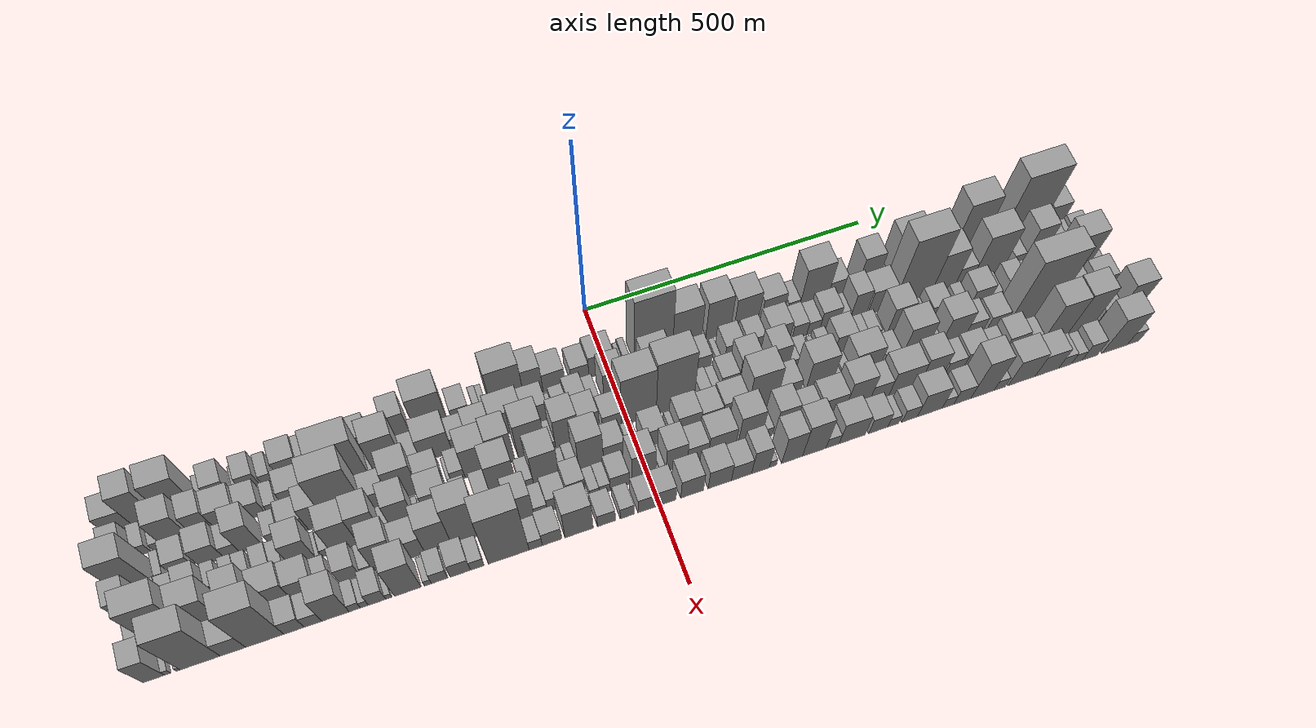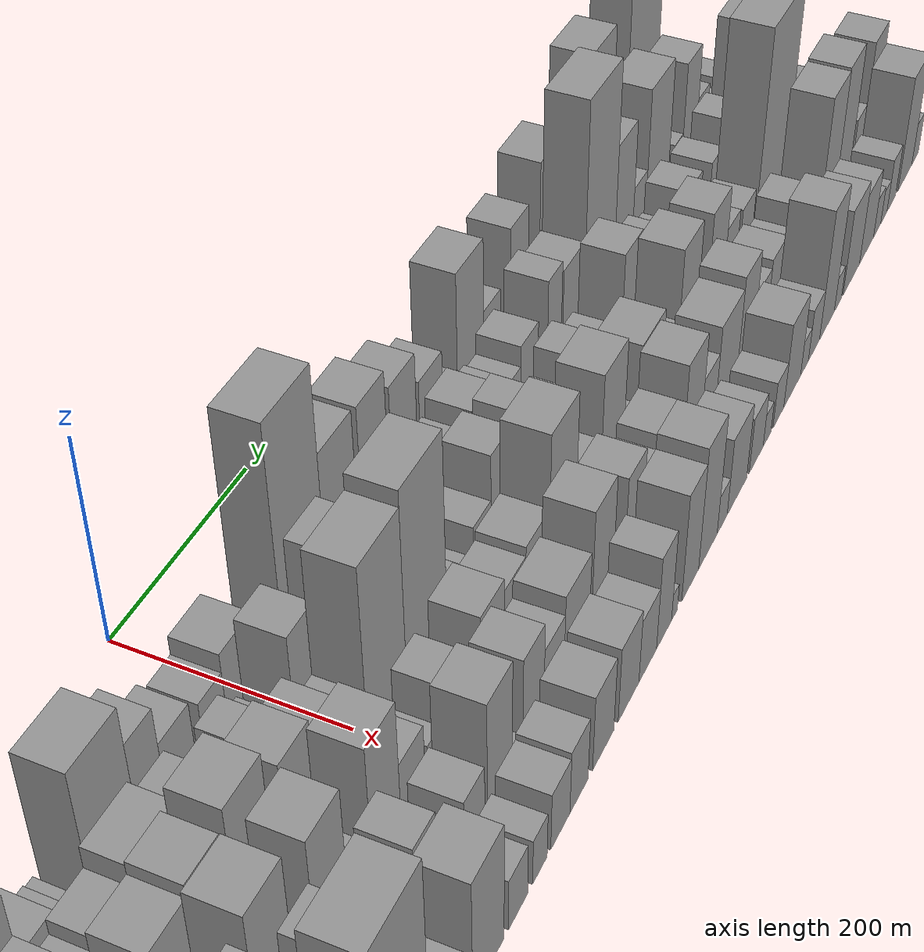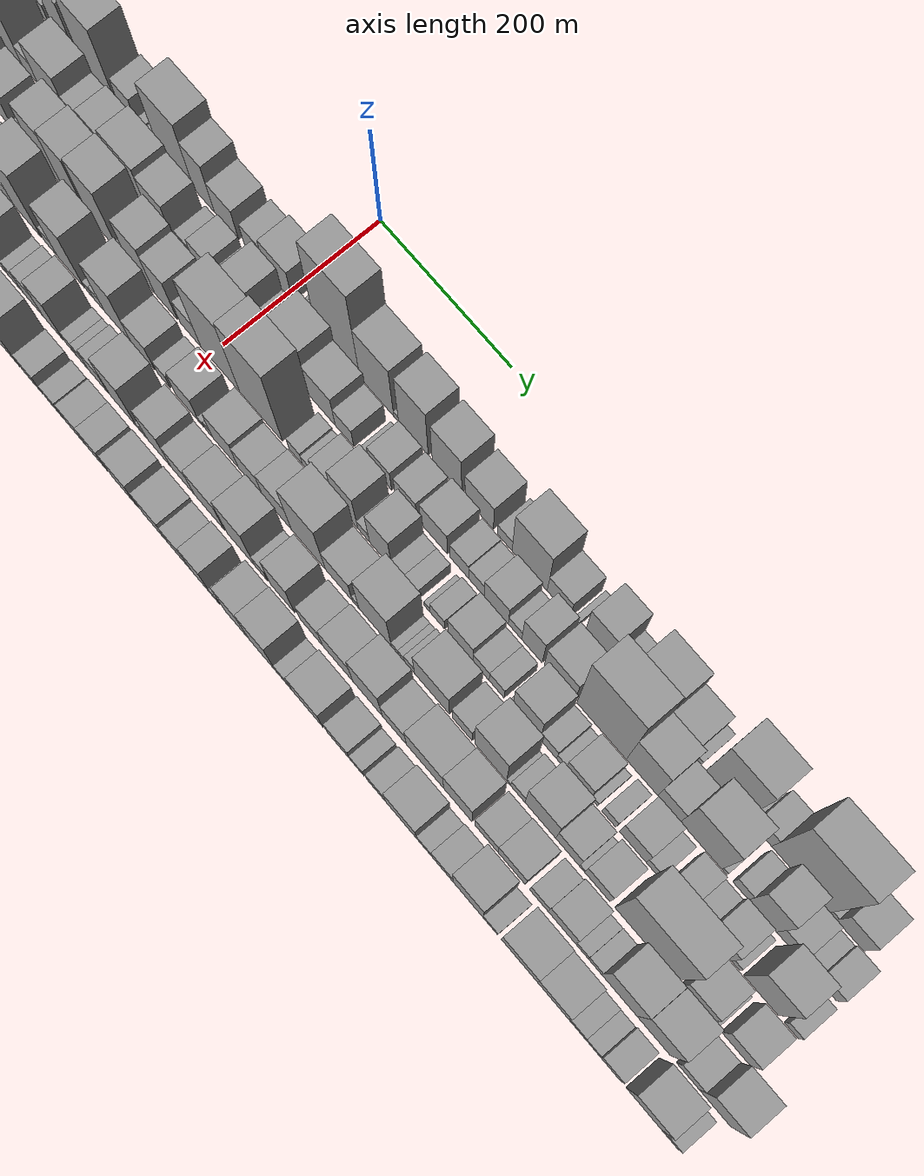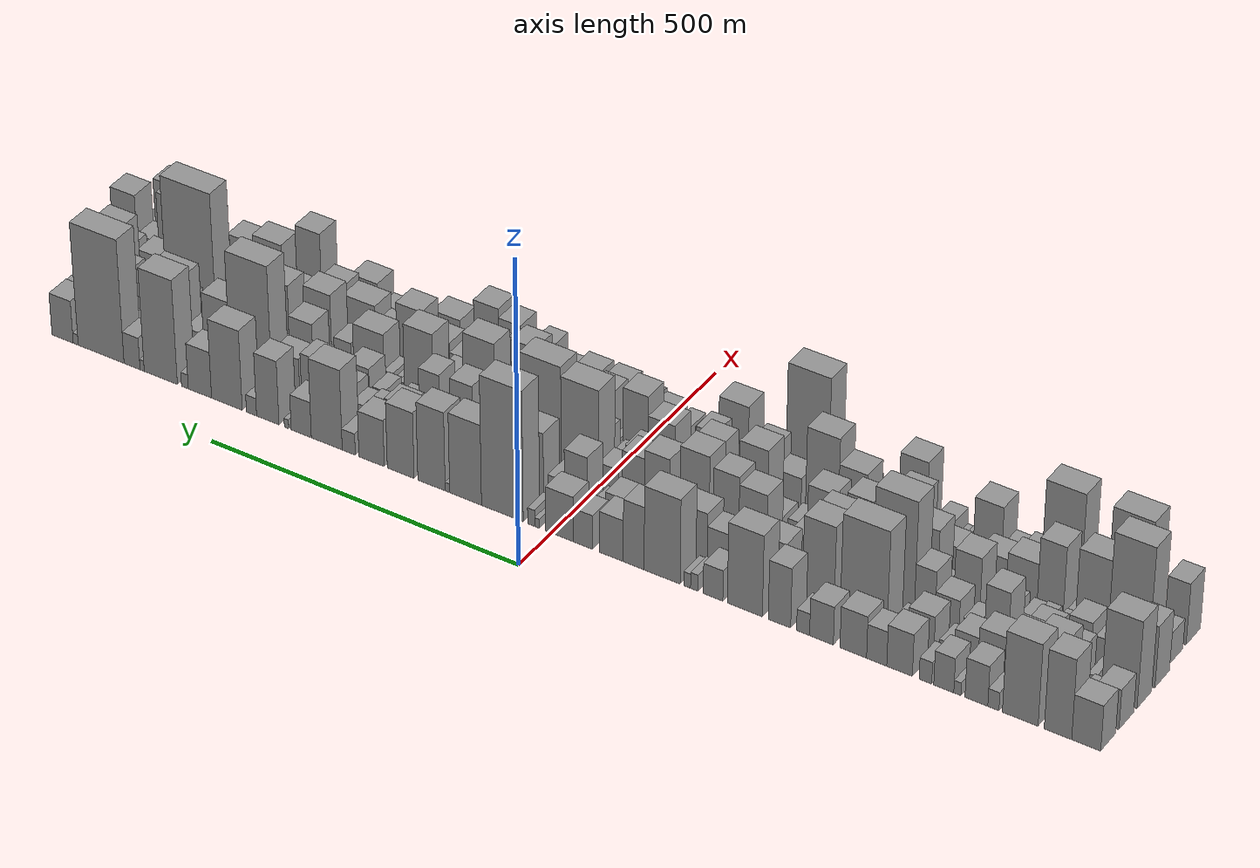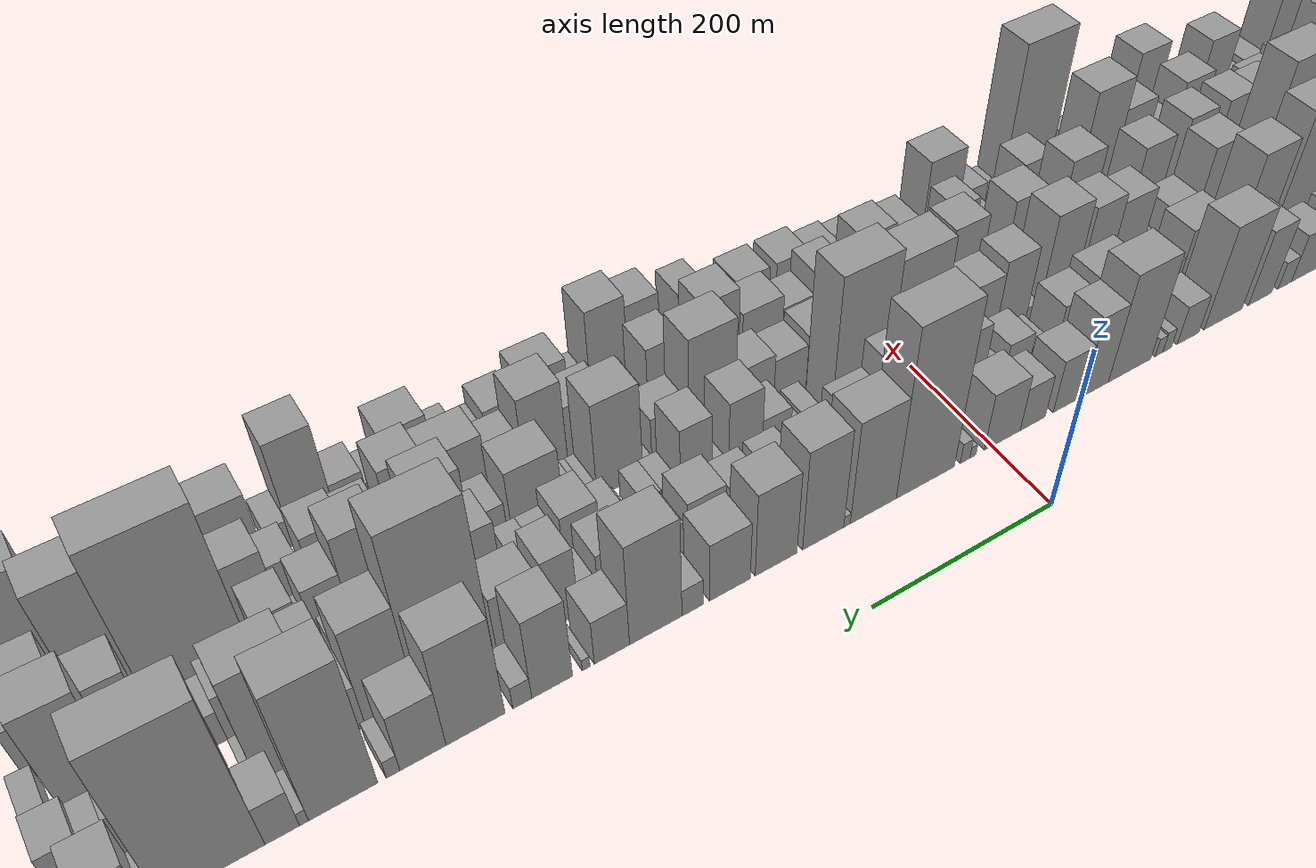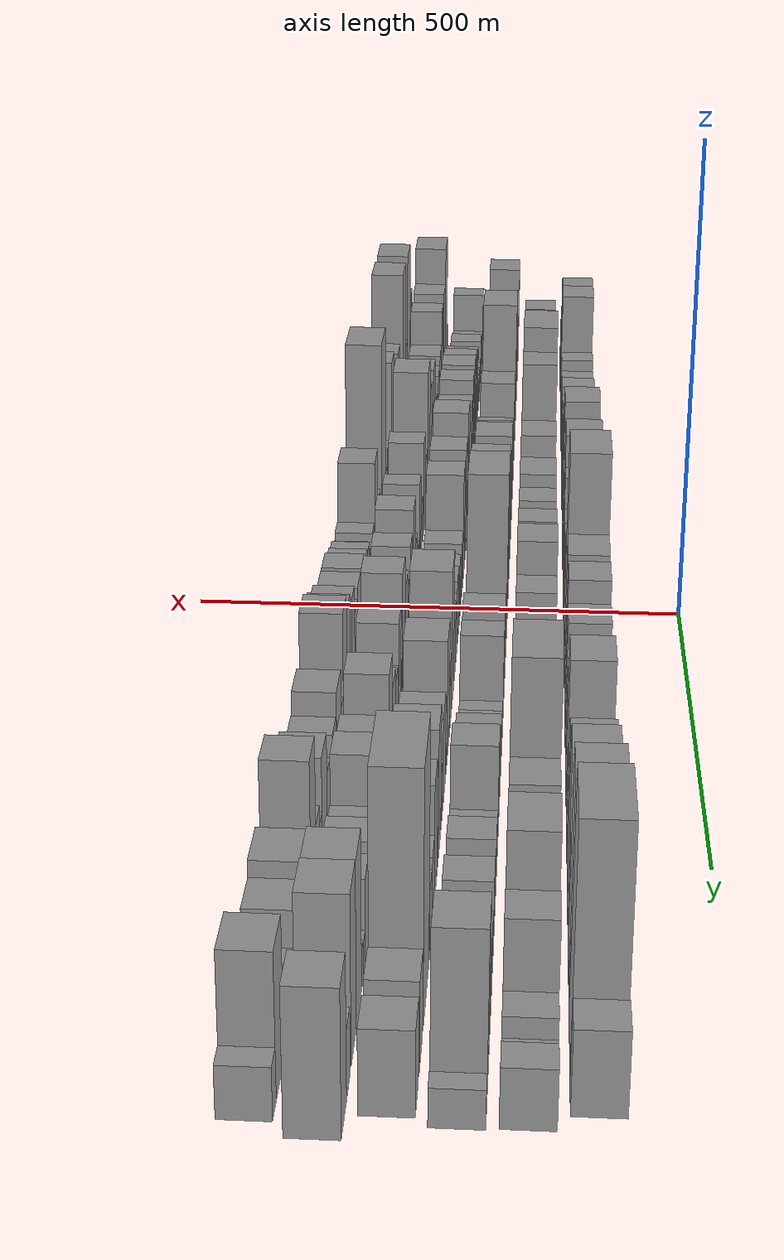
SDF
<sdf version="1.6">
 <world name="default">
  <scene>
   <sky><clouds><speed>12</speed></clouds></sky>
   <ambient>0.4 0.4 0.4 1</ambient>
   <background>0.7 0.7 0.7 1</background>
   <shadows>1</shadows>
  </scene>
  <gravity>0 0 -9.8066</gravity>
  <magnetic_field>6e-06 2.3e-05 -4.2e-05</magnetic_field>
  <physics default="0" name="default_physics" type="ode">
   <ode>
    <solver>
     <type>quick</type>
     <iters>10</iters>
     <sor>1.0</sor>
     <use_dynamic_moi_rescaling>0</use_dynamic_moi_rescaling>
    </solver>
    <constraints>
     <cfm>0</cfm>
     <erp>0.2</erp>
     <contact_max_correcting_vel>100</contact_max_correcting_vel>
     <contact_surface_layer>0.001</contact_surface_layer>
    </constraints>
   </ode>
   <max_step_size>0.004</max_step_size>
   <real_time_factor>1</real_time_factor>
   <real_time_update_rate>250</real_time_update_rate>
  </physics>
  <light name="sun" type="directional">
   <pose>0 0 10 0 0 0</pose>
   <diffuse>0.8 0.8 0.8 1</diffuse>
   <specular>0.2 0.2 0.2 1</specular>
   <attenuation>
    <range>1000</range>
    <constant>0.9</constant>
    <linear>0.01</linear>
    <quadratic>0.001</quadratic>
   </attenuation>
   <direction>-0.5 0.1 -0.9</direction>
  </light>
  <model name="building_1">
   <static>1</static>
   <pose>100.0000 -809.0275 0 0.000000 0.000000 0.000000</pose>
   <link name="link">
    <pose>0 0 37.50 0 0 0</pose>
    <collision name="collision"><geometry><box><size>40.0000 41.9451 75.0000</size></box></geometry></collision>
    <visual name="visual">
     <cast_shadows>0</cast_shadows>
     <geometry><box><size>40.0000 41.9451 75.0000</size></box></geometry>
     <material>
      <script>
       <uri>model://grey_wall/materials/scripts</uri>
       <uri>model://grey_wall/materials/textures</uri>
       <name>vrc/grey_wall</name>
      </script>
     </material>
    </visual>
   </link>
  </model>
  <model name="building_2">
   <static>1</static>
   <pose>100.0000 -768.1937 0 0.000000 0.000000 0.000000</pose>
   <link name="link">
    <pose>0 0 66.00 0 0 0</pose>
    <collision name="collision"><geometry><box><size>40.0000 39.7225 132.0000</size></box></geometry></collision>
    <visual name="visual">
     <cast_shadows>0</cast_shadows>
     <geometry><box><size>40.0000 39.7225 132.0000</size></box></geometry>
     <material>
      <script>
       <uri>model://grey_wall/materials/scripts</uri>
       <uri>model://grey_wall/materials/textures</uri>
       <name>vrc/grey_wall</name>
      </script>
     </material>
    </visual>
   </link>
  </model>
  <model name="building_3">
   <static>1</static>
   <pose>100.0000 -713.2842 0 0.000000 0.000000 0.000000</pose>
   <link name="link">
    <pose>0 0 67.50 0 0 0</pose>
    <collision name="collision"><geometry><box><size>40.0000 52.0963 135.0000</size></box></geometry></collision>
    <visual name="visual">
     <cast_shadows>0</cast_shadows>
     <geometry><box><size>40.0000 52.0963 135.0000</size></box></geometry>
     <material>
      <script>
       <uri>model://grey_wall/materials/scripts</uri>
       <uri>model://grey_wall/materials/textures</uri>
       <name>vrc/grey_wall</name>
      </script>
     </material>
    </visual>
   </link>
  </model>
  <model name="building_4">
   <static>1</static>
   <pose>100.0000 -674.0197 0 0.000000 0.000000 0.000000</pose>
   <link name="link">
    <pose>0 0 15.00 0 0 0</pose>
    <collision name="collision"><geometry><box><size>40.0000 16.4328 30.0000</size></box></geometry></collision>
    <visual name="visual">
     <cast_shadows>0</cast_shadows>
     <geometry><box><size>40.0000 16.4328 30.0000</size></box></geometry>
     <material>
      <script>
       <uri>model://grey_wall/materials/scripts</uri>
       <uri>model://grey_wall/materials/textures</uri>
       <name>vrc/grey_wall</name>
      </script>
     </material>
    </visual>
   </link>
  </model>
  <model name="building_5">
   <static>1</static>
   <pose>100.0000 -649.0219 0 0.000000 0.000000 0.000000</pose>
   <link name="link">
    <pose>0 0 33.00 0 0 0</pose>
    <collision name="collision"><geometry><box><size>40.0000 33.5627 66.0000</size></box></geometry></collision>
    <visual name="visual">
     <cast_shadows>0</cast_shadows>
     <geometry><box><size>40.0000 33.5627 66.0000</size></box></geometry>
     <material>
      <script>
       <uri>model://grey_wall/materials/scripts</uri>
       <uri>model://grey_wall/materials/textures</uri>
       <name>vrc/grey_wall</name>
      </script>
     </material>
    </visual>
   </link>
  </model>
  <model name="building_6">
   <static>1</static>
   <pose>100.0000 -621.0068 0 0.000000 0.000000 0.000000</pose>
   <link name="link">
    <pose>0 0 10.50 0 0 0</pose>
    <collision name="collision"><geometry><box><size>40.0000 10.4675 21.0000</size></box></geometry></collision>
    <visual name="visual">
     <cast_shadows>0</cast_shadows>
     <geometry><box><size>40.0000 10.4675 21.0000</size></box></geometry>
     <material>
      <script>
       <uri>model://grey_wall/materials/scripts</uri>
       <uri>model://grey_wall/materials/textures</uri>
       <name>vrc/grey_wall</name>
      </script>
     </material>
    </visual>
   </link>
  </model>
  <model name="building_7">
   <static>1</static>
   <pose>100.0000 -600.9219 0 0.000000 0.000000 0.000000</pose>
   <link name="link">
    <pose>0 0 28.50 0 0 0</pose>
    <collision name="collision"><geometry><box><size>40.0000 29.7023 57.0000</size></box></geometry></collision>
    <visual name="visual">
     <cast_shadows>0</cast_shadows>
     <geometry><box><size>40.0000 29.7023 57.0000</size></box></geometry>
     <material>
      <script>
       <uri>model://grey_wall/materials/scripts</uri>
       <uri>model://grey_wall/materials/textures</uri>
       <name>vrc/grey_wall</name>
      </script>
     </material>
    </visual>
   </link>
  </model>
  <model name="building_8">
   <static>1</static>
   <pose>100.0000 -573.7204 0 0.000000 0.000000 0.000000</pose>
   <link name="link">
    <pose>0 0 18.00 0 0 0</pose>
    <collision name="collision"><geometry><box><size>40.0000 18.7007 36.0000</size></box></geometry></collision>
    <visual name="visual">
     <cast_shadows>0</cast_shadows>
     <geometry><box><size>40.0000 18.7007 36.0000</size></box></geometry>
     <material>
      <script>
       <uri>model://grey_wall/materials/scripts</uri>
       <uri>model://grey_wall/materials/textures</uri>
       <name>vrc/grey_wall</name>
      </script>
     </material>
    </visual>
   </link>
  </model>
  <model name="building_9">
   <static>1</static>
   <pose>100.0000 -535.2553 0 0.000000 0.000000 0.000000</pose>
   <link name="link">
    <pose>0 0 34.50 0 0 0</pose>
    <collision name="collision"><geometry><box><size>40.0000 38.2295 69.0000</size></box></geometry></collision>
    <visual name="visual">
     <cast_shadows>0</cast_shadows>
     <geometry><box><size>40.0000 38.2295 69.0000</size></box></geometry>
     <material>
      <script>
       <uri>model://grey_wall/materials/scripts</uri>
       <uri>model://grey_wall/materials/textures</uri>
       <name>vrc/grey_wall</name>
      </script>
     </material>
    </visual>
   </link>
  </model>
  <model name="building_10">
   <static>1</static>
   <pose>100.0000 -501.0232 0 0.000000 0.000000 0.000000</pose>
   <link name="link">
    <pose>0 0 28.50 0 0 0</pose>
    <collision name="collision"><geometry><box><size>40.0000 30.2348 57.0000</size></box></geometry></collision>
    <visual name="visual">
     <cast_shadows>0</cast_shadows>
     <geometry><box><size>40.0000 30.2348 57.0000</size></box></geometry>
     <material>
      <script>
       <uri>model://grey_wall/materials/scripts</uri>
       <uri>model://grey_wall/materials/textures</uri>
       <name>vrc/grey_wall</name>
      </script>
     </material>
    </visual>
   </link>
  </model>
  <model name="building_11">
   <static>1</static>
   <pose>100.0000 -465.9183 0 0.000000 0.000000 0.000000</pose>
   <link name="link">
    <pose>0 0 34.50 0 0 0</pose>
    <collision name="collision"><geometry><box><size>40.0000 39.9749 69.0000</size></box></geometry></collision>
    <visual name="visual">
     <cast_shadows>0</cast_shadows>
     <geometry><box><size>40.0000 39.9749 69.0000</size></box></geometry>
     <material>
      <script>
       <uri>model://grey_wall/materials/scripts</uri>
       <uri>model://grey_wall/materials/textures</uri>
       <name>vrc/grey_wall</name>
      </script>
     </material>
    </visual>
   </link>
  </model>
  <model name="building_12">
   <static>1</static>
   <pose>100.0000 -417.9923 0 0.000000 0.000000 0.000000</pose>
   <link name="link">
    <pose>0 0 31.50 0 0 0</pose>
    <collision name="collision"><geometry><box><size>40.0000 35.8771 63.0000</size></box></geometry></collision>
    <visual name="visual">
     <cast_shadows>0</cast_shadows>
     <geometry><box><size>40.0000 35.8771 63.0000</size></box></geometry>
     <material>
      <script>
       <uri>model://grey_wall/materials/scripts</uri>
       <uri>model://grey_wall/materials/textures</uri>
       <name>vrc/grey_wall</name>
      </script>
     </material>
    </visual>
   </link>
  </model>
  <model name="building_13">
   <static>1</static>
   <pose>100.0000 -390.1856 0 0.000000 0.000000 0.000000</pose>
   <link name="link">
    <pose>0 0 18.00 0 0 0</pose>
    <collision name="collision"><geometry><box><size>40.0000 19.7364 36.0000</size></box></geometry></collision>
    <visual name="visual">
     <cast_shadows>0</cast_shadows>
     <geometry><box><size>40.0000 19.7364 36.0000</size></box></geometry>
     <material>
      <script>
       <uri>model://grey_wall/materials/scripts</uri>
       <uri>model://grey_wall/materials/textures</uri>
       <name>vrc/grey_wall</name>
      </script>
     </material>
    </visual>
   </link>
  </model>
  <model name="building_14">
   <static>1</static>
   <pose>100.0000 -354.2431 0 0.000000 0.000000 0.000000</pose>
   <link name="link">
    <pose>0 0 49.50 0 0 0</pose>
    <collision name="collision"><geometry><box><size>40.0000 34.1485 99.0000</size></box></geometry></collision>
    <visual name="visual">
     <cast_shadows>0</cast_shadows>
     <geometry><box><size>40.0000 34.1485 99.0000</size></box></geometry>
     <material>
      <script>
       <uri>model://grey_wall/materials/scripts</uri>
       <uri>model://grey_wall/materials/textures</uri>
       <name>vrc/grey_wall</name>
      </script>
     </material>
    </visual>
   </link>
  </model>
  <model name="building_15">
   <static>1</static>
   <pose>100.0000 -301.3422 0 0.000000 0.000000 0.000000</pose>
   <link name="link">
    <pose>0 0 67.50 0 0 0</pose>
    <collision name="collision"><geometry><box><size>40.0000 53.6532 135.0000</size></box></geometry></collision>
    <visual name="visual">
     <cast_shadows>0</cast_shadows>
     <geometry><box><size>40.0000 53.6532 135.0000</size></box></geometry>
     <material>
      <script>
       <uri>model://grey_wall/materials/scripts</uri>
       <uri>model://grey_wall/materials/textures</uri>
       <name>vrc/grey_wall</name>
      </script>
     </material>
    </visual>
   </link>
  </model>
  <model name="building_16">
   <static>1</static>
   <pose>100.0000 -252.4780 0 0.000000 0.000000 0.000000</pose>
   <link name="link">
    <pose>0 0 25.50 0 0 0</pose>
    <collision name="collision"><geometry><box><size>40.0000 30.0753 51.0000</size></box></geometry></collision>
    <visual name="visual">
     <cast_shadows>0</cast_shadows>
     <geometry><box><size>40.0000 30.0753 51.0000</size></box></geometry>
     <material>
      <script>
       <uri>model://grey_wall/materials/scripts</uri>
       <uri>model://grey_wall/materials/textures</uri>
       <name>vrc/grey_wall</name>
      </script>
     </material>
    </visual>
   </link>
  </model>
  <model name="building_17">
   <static>1</static>
   <pose>100.0000 -223.5903 0 0.000000 0.000000 0.000000</pose>
   <link name="link">
    <pose>0 0 13.50 0 0 0</pose>
    <collision name="collision"><geometry><box><size>40.0000 11.7002 27.0000</size></box></geometry></collision>
    <visual name="visual">
     <cast_shadows>0</cast_shadows>
     <geometry><box><size>40.0000 11.7002 27.0000</size></box></geometry>
     <material>
      <script>
       <uri>model://grey_wall/materials/scripts</uri>
       <uri>model://grey_wall/materials/textures</uri>
       <name>vrc/grey_wall</name>
      </script>
     </material>
    </visual>
   </link>
  </model>
  <model name="building_18">
   <static>1</static>
   <pose>100.0000 -212.6931 0 0.000000 0.000000 0.000000</pose>
   <link name="link">
    <pose>0 0 12.00 0 0 0</pose>
    <collision name="collision"><geometry><box><size>40.0000 10.0943 24.0000</size></box></geometry></collision>
    <visual name="visual">
     <cast_shadows>0</cast_shadows>
     <geometry><box><size>40.0000 10.0943 24.0000</size></box></geometry>
     <material>
      <script>
       <uri>model://grey_wall/materials/scripts</uri>
       <uri>model://grey_wall/materials/textures</uri>
       <name>vrc/grey_wall</name>
      </script>
     </material>
    </visual>
   </link>
  </model>
  <model name="building_19">
   <static>1</static>
   <pose>100.0000 -173.6003 0 0.000000 0.000000 0.000000</pose>
   <link name="link">
    <pose>0 0 70.50 0 0 0</pose>
    <collision name="collision"><geometry><box><size>40.0000 56.0913 141.0000</size></box></geometry></collision>
    <visual name="visual">
     <cast_shadows>0</cast_shadows>
     <geometry><box><size>40.0000 56.0913 141.0000</size></box></geometry>
     <material>
      <script>
       <uri>model://grey_wall/materials/scripts</uri>
       <uri>model://grey_wall/materials/textures</uri>
       <name>vrc/grey_wall</name>
      </script>
     </material>
    </visual>
   </link>
  </model>
  <model name="building_20">
   <static>1</static>
   <pose>100.0000 -129.2822 0 0.000000 0.000000 0.000000</pose>
   <link name="link">
    <pose>0 0 52.50 0 0 0</pose>
    <collision name="collision"><geometry><box><size>40.0000 32.5449 105.0000</size></box></geometry></collision>
    <visual name="visual">
     <cast_shadows>0</cast_shadows>
     <geometry><box><size>40.0000 32.5449 105.0000</size></box></geometry>
     <material>
      <script>
       <uri>model://grey_wall/materials/scripts</uri>
       <uri>model://grey_wall/materials/textures</uri>
       <name>vrc/grey_wall</name>
      </script>
     </material>
    </visual>
   </link>
  </model>
  <model name="building_21">
   <static>1</static>
   <pose>100.0000 -93.9875 0 0.000000 0.000000 0.000000</pose>
   <link name="link">
    <pose>0 0 34.50 0 0 0</pose>
    <collision name="collision"><geometry><box><size>40.0000 38.0445 69.0000</size></box></geometry></collision>
    <visual name="visual">
     <cast_shadows>0</cast_shadows>
     <geometry><box><size>40.0000 38.0445 69.0000</size></box></geometry>
     <material>
      <script>
       <uri>model://grey_wall/materials/scripts</uri>
       <uri>model://grey_wall/materials/textures</uri>
       <name>vrc/grey_wall</name>
      </script>
     </material>
    </visual>
   </link>
  </model>
  <model name="building_22">
   <static>1</static>
   <pose>100.0000 -49.4875 0 0.000000 0.000000 0.000000</pose>
   <link name="link">
    <pose>0 0 28.50 0 0 0</pose>
    <collision name="collision"><geometry><box><size>40.0000 30.9556 57.0000</size></box></geometry></collision>
    <visual name="visual">
     <cast_shadows>0</cast_shadows>
     <geometry><box><size>40.0000 30.9556 57.0000</size></box></geometry>
     <material>
      <script>
       <uri>model://grey_wall/materials/scripts</uri>
       <uri>model://grey_wall/materials/textures</uri>
       <name>vrc/grey_wall</name>
      </script>
     </material>
    </visual>
   </link>
  </model>
  <model name="building_23">
   <static>1</static>
   <pose>100.0000 -12.2931 0 0.000000 0.000000 0.000000</pose>
   <link name="link">
    <pose>0 0 37.50 0 0 0</pose>
    <collision name="collision"><geometry><box><size>40.0000 43.4332 75.0000</size></box></geometry></collision>
    <visual name="visual">
     <cast_shadows>0</cast_shadows>
     <geometry><box><size>40.0000 43.4332 75.0000</size></box></geometry>
     <material>
      <script>
       <uri>model://grey_wall/materials/scripts</uri>
       <uri>model://grey_wall/materials/textures</uri>
       <name>vrc/grey_wall</name>
      </script>
     </material>
    </visual>
   </link>
  </model>
  <model name="building_24">
   <static>1</static>
   <pose>100.0000 23.1443 0 0.000000 0.000000 0.000000</pose>
   <link name="link">
    <pose>0 0 7.50 0 0 0</pose>
    <collision name="collision"><geometry><box><size>40.0000 7.4417 15.0000</size></box></geometry></collision>
    <visual name="visual">
     <cast_shadows>0</cast_shadows>
     <geometry><box><size>40.0000 7.4417 15.0000</size></box></geometry>
     <material>
      <script>
       <uri>model://grey_wall/materials/scripts</uri>
       <uri>model://grey_wall/materials/textures</uri>
       <name>vrc/grey_wall</name>
      </script>
     </material>
    </visual>
   </link>
  </model>
  <model name="building_25">
   <static>1</static>
   <pose>100.0000 32.5370 0 0.000000 0.000000 0.000000</pose>
   <link name="link">
    <pose>0 0 13.50 0 0 0</pose>
    <collision name="collision"><geometry><box><size>40.0000 11.3437 27.0000</size></box></geometry></collision>
    <visual name="visual">
     <cast_shadows>0</cast_shadows>
     <geometry><box><size>40.0000 11.3437 27.0000</size></box></geometry>
     <material>
      <script>
       <uri>model://grey_wall/materials/scripts</uri>
       <uri>model://grey_wall/materials/textures</uri>
       <name>vrc/grey_wall</name>
      </script>
     </material>
    </visual>
   </link>
  </model>
  <model name="building_26">
   <static>1</static>
   <pose>100.0000 78.6718 0 0.000000 0.000000 0.000000</pose>
   <link name="link">
    <pose>0 0 109.50 0 0 0</pose>
    <collision name="collision"><geometry><box><size>40.0000 66.9260 219.0000</size></box></geometry></collision>
    <visual name="visual">
     <cast_shadows>0</cast_shadows>
     <geometry><box><size>40.0000 66.9260 219.0000</size></box></geometry>
     <material>
      <script>
       <uri>model://grey_wall/materials/scripts</uri>
       <uri>model://grey_wall/materials/textures</uri>
       <name>vrc/grey_wall</name>
      </script>
     </material>
    </visual>
   </link>
  </model>
  <model name="building_27">
   <static>1</static>
   <pose>100.0000 137.7826 0 0.000000 0.000000 0.000000</pose>
   <link name="link">
    <pose>0 0 67.50 0 0 0</pose>
    <collision name="collision"><geometry><box><size>40.0000 51.2957 135.0000</size></box></geometry></collision>
    <visual name="visual">
     <cast_shadows>0</cast_shadows>
     <geometry><box><size>40.0000 51.2957 135.0000</size></box></geometry>
     <material>
      <script>
       <uri>model://grey_wall/materials/scripts</uri>
       <uri>model://grey_wall/materials/textures</uri>
       <name>vrc/grey_wall</name>
      </script>
     </material>
    </visual>
   </link>
  </model>
  <model name="building_28">
   <static>1</static>
   <pose>100.0000 167.0437 0 0.000000 0.000000 0.000000</pose>
   <link name="link">
    <pose>0 0 7.50 0 0 0</pose>
    <collision name="collision"><geometry><box><size>40.0000 7.2264 15.0000</size></box></geometry></collision>
    <visual name="visual">
     <cast_shadows>0</cast_shadows>
     <geometry><box><size>40.0000 7.2264 15.0000</size></box></geometry>
     <material>
      <script>
       <uri>model://grey_wall/materials/scripts</uri>
       <uri>model://grey_wall/materials/textures</uri>
       <name>vrc/grey_wall</name>
      </script>
     </material>
    </visual>
   </link>
  </model>
  <model name="building_29">
   <static>1</static>
   <pose>100.0000 192.8923 0 0.000000 0.000000 0.000000</pose>
   <link name="link">
    <pose>0 0 66.00 0 0 0</pose>
    <collision name="collision"><geometry><box><size>40.0000 44.4707 132.0000</size></box></geometry></collision>
    <visual name="visual">
     <cast_shadows>0</cast_shadows>
     <geometry><box><size>40.0000 44.4707 132.0000</size></box></geometry>
     <material>
      <script>
       <uri>model://grey_wall/materials/scripts</uri>
       <uri>model://grey_wall/materials/textures</uri>
       <name>vrc/grey_wall</name>
      </script>
     </material>
    </visual>
   </link>
  </model>
  <model name="building_30">
   <static>1</static>
   <pose>100.0000 243.0312 0 0.000000 0.000000 0.000000</pose>
   <link name="link">
    <pose>0 0 55.50 0 0 0</pose>
    <collision name="collision"><geometry><box><size>40.0000 43.8071 111.0000</size></box></geometry></collision>
    <visual name="visual">
     <cast_shadows>0</cast_shadows>
     <geometry><box><size>40.0000 43.8071 111.0000</size></box></geometry>
     <material>
      <script>
       <uri>model://grey_wall/materials/scripts</uri>
       <uri>model://grey_wall/materials/textures</uri>
       <name>vrc/grey_wall</name>
      </script>
     </material>
    </visual>
   </link>
  </model>
  <model name="building_31">
   <static>1</static>
   <pose>100.0000 290.7490 0 0.000000 0.000000 0.000000</pose>
   <link name="link">
    <pose>0 0 39.00 0 0 0</pose>
    <collision name="collision"><geometry><box><size>40.0000 41.6285 78.0000</size></box></geometry></collision>
    <visual name="visual">
     <cast_shadows>0</cast_shadows>
     <geometry><box><size>40.0000 41.6285 78.0000</size></box></geometry>
     <material>
      <script>
       <uri>model://grey_wall/materials/scripts</uri>
       <uri>model://grey_wall/materials/textures</uri>
       <name>vrc/grey_wall</name>
      </script>
     </material>
    </visual>
   </link>
  </model>
  <model name="building_32">
   <static>1</static>
   <pose>100.0000 328.3481 0 0.000000 0.000000 0.000000</pose>
   <link name="link">
    <pose>0 0 18.00 0 0 0</pose>
    <collision name="collision"><geometry><box><size>40.0000 21.5696 36.0000</size></box></geometry></collision>
    <visual name="visual">
     <cast_shadows>0</cast_shadows>
     <geometry><box><size>40.0000 21.5696 36.0000</size></box></geometry>
     <material>
      <script>
       <uri>model://grey_wall/materials/scripts</uri>
       <uri>model://grey_wall/materials/textures</uri>
       <name>vrc/grey_wall</name>
      </script>
     </material>
    </visual>
   </link>
  </model>
  <model name="building_33">
   <static>1</static>
   <pose>100.0000 364.6896 0 0.000000 0.000000 0.000000</pose>
   <link name="link">
    <pose>0 0 67.50 0 0 0</pose>
    <collision name="collision"><geometry><box><size>40.0000 51.1135 135.0000</size></box></geometry></collision>
    <visual name="visual">
     <cast_shadows>0</cast_shadows>
     <geometry><box><size>40.0000 51.1135 135.0000</size></box></geometry>
     <material>
      <script>
       <uri>model://grey_wall/materials/scripts</uri>
       <uri>model://grey_wall/materials/textures</uri>
       <name>vrc/grey_wall</name>
      </script>
     </material>
    </visual>
   </link>
  </model>
  <model name="building_34">
   <static>1</static>
   <pose>100.0000 407.0011 0 0.000000 0.000000 0.000000</pose>
   <link name="link">
    <pose>0 0 30.00 0 0 0</pose>
    <collision name="collision"><geometry><box><size>40.0000 33.5095 60.0000</size></box></geometry></collision>
    <visual name="visual">
     <cast_shadows>0</cast_shadows>
     <geometry><box><size>40.0000 33.5095 60.0000</size></box></geometry>
     <material>
      <script>
       <uri>model://grey_wall/materials/scripts</uri>
       <uri>model://grey_wall/materials/textures</uri>
       <name>vrc/grey_wall</name>
      </script>
     </material>
    </visual>
   </link>
  </model>
  <model name="building_35">
   <static>1</static>
   <pose>100.0000 431.4122 0 0.000000 0.000000 0.000000</pose>
   <link name="link">
    <pose>0 0 7.50 0 0 0</pose>
    <collision name="collision"><geometry><box><size>40.0000 7.3127 15.0000</size></box></geometry></collision>
    <visual name="visual">
     <cast_shadows>0</cast_shadows>
     <geometry><box><size>40.0000 7.3127 15.0000</size></box></geometry>
     <material>
      <script>
       <uri>model://grey_wall/materials/scripts</uri>
       <uri>model://grey_wall/materials/textures</uri>
       <name>vrc/grey_wall</name>
      </script>
     </material>
    </visual>
   </link>
  </model>
  <model name="building_36">
   <static>1</static>
   <pose>100.0000 462.8106 0 0.000000 0.000000 0.000000</pose>
   <link name="link">
    <pose>0 0 54.00 0 0 0</pose>
    <collision name="collision"><geometry><box><size>40.0000 37.4840 108.0000</size></box></geometry></collision>
    <visual name="visual">
     <cast_shadows>0</cast_shadows>
     <geometry><box><size>40.0000 37.4840 108.0000</size></box></geometry>
     <material>
      <script>
       <uri>model://grey_wall/materials/scripts</uri>
       <uri>model://grey_wall/materials/textures</uri>
       <name>vrc/grey_wall</name>
      </script>
     </material>
    </visual>
   </link>
  </model>
  <model name="building_37">
   <static>1</static>
   <pose>100.0000 490.0968 0 0.000000 0.000000 0.000000</pose>
   <link name="link">
    <pose>0 0 15.00 0 0 0</pose>
    <collision name="collision"><geometry><box><size>40.0000 17.0884 30.0000</size></box></geometry></collision>
    <visual name="visual">
     <cast_shadows>0</cast_shadows>
     <geometry><box><size>40.0000 17.0884 30.0000</size></box></geometry>
     <material>
      <script>
       <uri>model://grey_wall/materials/scripts</uri>
       <uri>model://grey_wall/materials/textures</uri>
       <name>vrc/grey_wall</name>
      </script>
     </material>
    </visual>
   </link>
  </model>
  <model name="building_38">
   <static>1</static>
   <pose>100.0000 531.5187 0 0.000000 0.000000 0.000000</pose>
   <link name="link">
    <pose>0 0 67.50 0 0 0</pose>
    <collision name="collision"><geometry><box><size>40.0000 51.7555 135.0000</size></box></geometry></collision>
    <visual name="visual">
     <cast_shadows>0</cast_shadows>
     <geometry><box><size>40.0000 51.7555 135.0000</size></box></geometry>
     <material>
      <script>
       <uri>model://grey_wall/materials/scripts</uri>
       <uri>model://grey_wall/materials/textures</uri>
       <name>vrc/grey_wall</name>
      </script>
     </material>
    </visual>
   </link>
  </model>
  <model name="building_39">
   <static>1</static>
   <pose>100.0000 577.1728 0 0.000000 0.000000 0.000000</pose>
   <link name="link">
    <pose>0 0 39.00 0 0 0</pose>
    <collision name="collision"><geometry><box><size>40.0000 39.5526 78.0000</size></box></geometry></collision>
    <visual name="visual">
     <cast_shadows>0</cast_shadows>
     <geometry><box><size>40.0000 39.5526 78.0000</size></box></geometry>
     <material>
      <script>
       <uri>model://grey_wall/materials/scripts</uri>
       <uri>model://grey_wall/materials/textures</uri>
       <name>vrc/grey_wall</name>
      </script>
     </material>
    </visual>
   </link>
  </model>
  <model name="building_40">
   <static>1</static>
   <pose>100.0000 602.6989 0 0.000000 0.000000 0.000000</pose>
   <link name="link">
    <pose>0 0 12.00 0 0 0</pose>
    <collision name="collision"><geometry><box><size>40.0000 11.4995 24.0000</size></box></geometry></collision>
    <visual name="visual">
     <cast_shadows>0</cast_shadows>
     <geometry><box><size>40.0000 11.4995 24.0000</size></box></geometry>
     <material>
      <script>
       <uri>model://grey_wall/materials/scripts</uri>
       <uri>model://grey_wall/materials/textures</uri>
       <name>vrc/grey_wall</name>
      </script>
     </material>
    </visual>
   </link>
  </model>
  <model name="building_41">
   <static>1</static>
   <pose>100.0000 643.7409 0 0.000000 0.000000 0.000000</pose>
   <link name="link">
    <pose>0 0 88.50 0 0 0</pose>
    <collision name="collision"><geometry><box><size>40.0000 56.5845 177.0000</size></box></geometry></collision>
    <visual name="visual">
     <cast_shadows>0</cast_shadows>
     <geometry><box><size>40.0000 56.5845 177.0000</size></box></geometry>
     <material>
      <script>
       <uri>model://grey_wall/materials/scripts</uri>
       <uri>model://grey_wall/materials/textures</uri>
       <name>vrc/grey_wall</name>
      </script>
     </material>
    </visual>
   </link>
  </model>
  <model name="building_42">
   <static>1</static>
   <pose>100.0000 675.6521 0 0.000000 0.000000 0.000000</pose>
   <link name="link">
    <pose>0 0 9.00 0 0 0</pose>
    <collision name="collision"><geometry><box><size>40.0000 7.2379 18.0000</size></box></geometry></collision>
    <visual name="visual">
     <cast_shadows>0</cast_shadows>
     <geometry><box><size>40.0000 7.2379 18.0000</size></box></geometry>
     <material>
      <script>
       <uri>model://grey_wall/materials/scripts</uri>
       <uri>model://grey_wall/materials/textures</uri>
       <name>vrc/grey_wall</name>
      </script>
     </material>
    </visual>
   </link>
  </model>
  <model name="building_43">
   <static>1</static>
   <pose>100.0000 692.9659 0 0.000000 0.000000 0.000000</pose>
   <link name="link">
    <pose>0 0 27.00 0 0 0</pose>
    <collision name="collision"><geometry><box><size>40.0000 27.3897 54.0000</size></box></geometry></collision>
    <visual name="visual">
     <cast_shadows>0</cast_shadows>
     <geometry><box><size>40.0000 27.3897 54.0000</size></box></geometry>
     <material>
      <script>
       <uri>model://grey_wall/materials/scripts</uri>
       <uri>model://grey_wall/materials/textures</uri>
       <name>vrc/grey_wall</name>
      </script>
     </material>
    </visual>
   </link>
  </model>
  <model name="building_44">
   <static>1</static>
   <pose>100.0000 746.2942 0 0.000000 0.000000 0.000000</pose>
   <link name="link">
    <pose>0 0 105.00 0 0 0</pose>
    <collision name="collision"><geometry><box><size>40.0000 79.2670 210.0000</size></box></geometry></collision>
    <visual name="visual">
     <cast_shadows>0</cast_shadows>
     <geometry><box><size>40.0000 79.2670 210.0000</size></box></geometry>
     <material>
      <script>
       <uri>model://grey_wall/materials/scripts</uri>
       <uri>model://grey_wall/materials/textures</uri>
       <name>vrc/grey_wall</name>
      </script>
     </material>
    </visual>
   </link>
  </model>
  <model name="building_45">
   <static>1</static>
   <pose>100.0000 790.2216 0 0.000000 0.000000 0.000000</pose>
   <link name="link">
    <pose>0 0 9.00 0 0 0</pose>
    <collision name="collision"><geometry><box><size>40.0000 8.5877 18.0000</size></box></geometry></collision>
    <visual name="visual">
     <cast_shadows>0</cast_shadows>
     <geometry><box><size>40.0000 8.5877 18.0000</size></box></geometry>
     <material>
      <script>
       <uri>model://grey_wall/materials/scripts</uri>
       <uri>model://grey_wall/materials/textures</uri>
       <name>vrc/grey_wall</name>
      </script>
     </material>
    </visual>
   </link>
  </model>
  <model name="building_46">
   <static>1</static>
   <pose>100.0000 812.9221 0 0.000000 0.000000 0.000000</pose>
   <link name="link">
    <pose>0 0 36.00 0 0 0</pose>
    <collision name="collision"><geometry><box><size>40.0000 36.8133 72.0000</size></box></geometry></collision>
    <visual name="visual">
     <cast_shadows>0</cast_shadows>
     <geometry><box><size>40.0000 36.8133 72.0000</size></box></geometry>
     <material>
      <script>
       <uri>model://grey_wall/materials/scripts</uri>
       <uri>model://grey_wall/materials/textures</uri>
       <name>vrc/grey_wall</name>
      </script>
     </material>
    </visual>
   </link>
  </model>
  <model name="building_47">
   <static>1</static>
   <pose>149.0000 -813.4391 0 0.000000 0.000000 0.000000</pose>
   <link name="link">
    <pose>0 0 33.00 0 0 0</pose>
    <collision name="collision"><geometry><box><size>40.0000 33.1218 66.0000</size></box></geometry></collision>
    <visual name="visual">
     <cast_shadows>0</cast_shadows>
     <geometry><box><size>40.0000 33.1218 66.0000</size></box></geometry>
     <material>
      <script>
       <uri>model://grey_wall/materials/scripts</uri>
       <uri>model://grey_wall/materials/textures</uri>
       <name>vrc/grey_wall</name>
      </script>
     </material>
    </visual>
   </link>
  </model>
  <model name="building_48">
   <static>1</static>
   <pose>149.0000 -781.6632 0 0.000000 0.000000 0.000000</pose>
   <link name="link">
    <pose>0 0 19.50 0 0 0</pose>
    <collision name="collision"><geometry><box><size>40.0000 20.4301 39.0000</size></box></geometry></collision>
    <visual name="visual">
     <cast_shadows>0</cast_shadows>
     <geometry><box><size>40.0000 20.4301 39.0000</size></box></geometry>
     <material>
      <script>
       <uri>model://grey_wall/materials/scripts</uri>
       <uri>model://grey_wall/materials/textures</uri>
       <name>vrc/grey_wall</name>
      </script>
     </material>
    </visual>
   </link>
  </model>
  <model name="building_49">
   <static>1</static>
   <pose>149.0000 -758.9136 0 0.000000 0.000000 0.000000</pose>
   <link name="link">
    <pose>0 0 15.00 0 0 0</pose>
    <collision name="collision"><geometry><box><size>40.0000 17.0690 30.0000</size></box></geometry></collision>
    <visual name="visual">
     <cast_shadows>0</cast_shadows>
     <geometry><box><size>40.0000 17.0690 30.0000</size></box></geometry>
     <material>
      <script>
       <uri>model://grey_wall/materials/scripts</uri>
       <uri>model://grey_wall/materials/textures</uri>
       <name>vrc/grey_wall</name>
      </script>
     </material>
    </visual>
   </link>
  </model>
  <model name="building_50">
   <static>1</static>
   <pose>149.0000 -728.6006 0 0.000000 0.000000 0.000000</pose>
   <link name="link">
    <pose>0 0 55.50 0 0 0</pose>
    <collision name="collision"><geometry><box><size>40.0000 43.5572 111.0000</size></box></geometry></collision>
    <visual name="visual">
     <cast_shadows>0</cast_shadows>
     <geometry><box><size>40.0000 43.5572 111.0000</size></box></geometry>
     <material>
      <script>
       <uri>model://grey_wall/materials/scripts</uri>
       <uri>model://grey_wall/materials/textures</uri>
       <name>vrc/grey_wall</name>
      </script>
     </material>
    </visual>
   </link>
  </model>
  <model name="building_51">
   <static>1</static>
   <pose>149.0000 -684.7399 0 0.000000 0.000000 0.000000</pose>
   <link name="link">
    <pose>0 0 46.50 0 0 0</pose>
    <collision name="collision"><geometry><box><size>40.0000 34.1642 93.0000</size></box></geometry></collision>
    <visual name="visual">
     <cast_shadows>0</cast_shadows>
     <geometry><box><size>40.0000 34.1642 93.0000</size></box></geometry>
     <material>
      <script>
       <uri>model://grey_wall/materials/scripts</uri>
       <uri>model://grey_wall/materials/textures</uri>
       <name>vrc/grey_wall</name>
      </script>
     </material>
    </visual>
   </link>
  </model>
  <model name="building_52">
   <static>1</static>
   <pose>149.0000 -645.3906 0 0.000000 0.000000 0.000000</pose>
   <link name="link">
    <pose>0 0 39.00 0 0 0</pose>
    <collision name="collision"><geometry><box><size>40.0000 44.5344 78.0000</size></box></geometry></collision>
    <visual name="visual">
     <cast_shadows>0</cast_shadows>
     <geometry><box><size>40.0000 44.5344 78.0000</size></box></geometry>
     <material>
      <script>
       <uri>model://grey_wall/materials/scripts</uri>
       <uri>model://grey_wall/materials/textures</uri>
       <name>vrc/grey_wall</name>
      </script>
     </material>
    </visual>
   </link>
  </model>
  <model name="building_53">
   <static>1</static>
   <pose>149.0000 -605.6415 0 0.000000 0.000000 0.000000</pose>
   <link name="link">
    <pose>0 0 30.00 0 0 0</pose>
    <collision name="collision"><geometry><box><size>40.0000 34.9639 60.0000</size></box></geometry></collision>
    <visual name="visual">
     <cast_shadows>0</cast_shadows>
     <geometry><box><size>40.0000 34.9639 60.0000</size></box></geometry>
     <material>
      <script>
       <uri>model://grey_wall/materials/scripts</uri>
       <uri>model://grey_wall/materials/textures</uri>
       <name>vrc/grey_wall</name>
      </script>
     </material>
    </visual>
   </link>
  </model>
  <model name="building_54">
   <static>1</static>
   <pose>149.0000 -575.5908 0 0.000000 0.000000 0.000000</pose>
   <link name="link">
    <pose>0 0 16.50 0 0 0</pose>
    <collision name="collision"><geometry><box><size>40.0000 19.1374 33.0000</size></box></geometry></collision>
    <visual name="visual">
     <cast_shadows>0</cast_shadows>
     <geometry><box><size>40.0000 19.1374 33.0000</size></box></geometry>
     <material>
      <script>
       <uri>model://grey_wall/materials/scripts</uri>
       <uri>model://grey_wall/materials/textures</uri>
       <name>vrc/grey_wall</name>
      </script>
     </material>
    </visual>
   </link>
  </model>
  <model name="building_55">
   <static>1</static>
   <pose>149.0000 -538.6001 0 0.000000 0.000000 0.000000</pose>
   <link name="link">
    <pose>0 0 33.00 0 0 0</pose>
    <collision name="collision"><geometry><box><size>40.0000 38.8440 66.0000</size></box></geometry></collision>
    <visual name="visual">
     <cast_shadows>0</cast_shadows>
     <geometry><box><size>40.0000 38.8440 66.0000</size></box></geometry>
     <material>
      <script>
       <uri>model://grey_wall/materials/scripts</uri>
       <uri>model://grey_wall/materials/textures</uri>
       <name>vrc/grey_wall</name>
      </script>
     </material>
    </visual>
   </link>
  </model>
  <model name="building_56">
   <static>1</static>
   <pose>149.0000 -506.0128 0 0.000000 0.000000 0.000000</pose>
   <link name="link">
    <pose>0 0 18.00 0 0 0</pose>
    <collision name="collision"><geometry><box><size>40.0000 20.3304 36.0000</size></box></geometry></collision>
    <visual name="visual">
     <cast_shadows>0</cast_shadows>
     <geometry><box><size>40.0000 20.3304 36.0000</size></box></geometry>
     <material>
      <script>
       <uri>model://grey_wall/materials/scripts</uri>
       <uri>model://grey_wall/materials/textures</uri>
       <name>vrc/grey_wall</name>
      </script>
     </material>
    </visual>
   </link>
  </model>
  <model name="building_57">
   <static>1</static>
   <pose>149.0000 -452.4649 0 0.000000 0.000000 0.000000</pose>
   <link name="link">
    <pose>0 0 88.50 0 0 0</pose>
    <collision name="collision"><geometry><box><size>40.0000 70.7655 177.0000</size></box></geometry></collision>
    <visual name="visual">
     <cast_shadows>0</cast_shadows>
     <geometry><box><size>40.0000 70.7655 177.0000</size></box></geometry>
     <material>
      <script>
       <uri>model://grey_wall/materials/scripts</uri>
       <uri>model://grey_wall/materials/textures</uri>
       <name>vrc/grey_wall</name>
      </script>
     </material>
    </visual>
   </link>
  </model>
  <model name="building_58">
   <static>1</static>
   <pose>149.0000 -412.4409 0 0.000000 0.000000 0.000000</pose>
   <link name="link">
    <pose>0 0 10.50 0 0 0</pose>
    <collision name="collision"><geometry><box><size>40.0000 9.2826 21.0000</size></box></geometry></collision>
    <visual name="visual">
     <cast_shadows>0</cast_shadows>
     <geometry><box><size>40.0000 9.2826 21.0000</size></box></geometry>
     <material>
      <script>
       <uri>model://grey_wall/materials/scripts</uri>
       <uri>model://grey_wall/materials/textures</uri>
       <name>vrc/grey_wall</name>
      </script>
     </material>
    </visual>
   </link>
  </model>
  <model name="building_59">
   <static>1</static>
   <pose>149.0000 -383.6070 0 0.000000 0.000000 0.000000</pose>
   <link name="link">
    <pose>0 0 75.00 0 0 0</pose>
    <collision name="collision"><geometry><box><size>40.0000 48.3852 150.0000</size></box></geometry></collision>
    <visual name="visual">
     <cast_shadows>0</cast_shadows>
     <geometry><box><size>40.0000 48.3852 150.0000</size></box></geometry>
     <material>
      <script>
       <uri>model://grey_wall/materials/scripts</uri>
       <uri>model://grey_wall/materials/textures</uri>
       <name>vrc/grey_wall</name>
      </script>
     </material>
    </visual>
   </link>
  </model>
  <model name="building_60">
   <static>1</static>
   <pose>149.0000 -346.8234 0 0.000000 0.000000 0.000000</pose>
   <link name="link">
    <pose>0 0 22.50 0 0 0</pose>
    <collision name="collision"><geometry><box><size>40.0000 25.1820 45.0000</size></box></geometry></collision>
    <visual name="visual">
     <cast_shadows>0</cast_shadows>
     <geometry><box><size>40.0000 25.1820 45.0000</size></box></geometry>
     <material>
      <script>
       <uri>model://grey_wall/materials/scripts</uri>
       <uri>model://grey_wall/materials/textures</uri>
       <name>vrc/grey_wall</name>
      </script>
     </material>
    </visual>
   </link>
  </model>
  <model name="building_61">
   <static>1</static>
   <pose>149.0000 -308.2573 0 0.000000 0.000000 0.000000</pose>
   <link name="link">
    <pose>0 0 45.00 0 0 0</pose>
    <collision name="collision"><geometry><box><size>40.0000 51.9501 90.0000</size></box></geometry></collision>
    <visual name="visual">
     <cast_shadows>0</cast_shadows>
     <geometry><box><size>40.0000 51.9501 90.0000</size></box></geometry>
     <material>
      <script>
       <uri>model://grey_wall/materials/scripts</uri>
       <uri>model://grey_wall/materials/textures</uri>
       <name>vrc/grey_wall</name>
      </script>
     </material>
    </visual>
   </link>
  </model>
  <model name="building_62">
   <static>1</static>
   <pose>149.0000 -268.3880 0 0.000000 0.000000 0.000000</pose>
   <link name="link">
    <pose>0 0 27.00 0 0 0</pose>
    <collision name="collision"><geometry><box><size>40.0000 27.7886 54.0000</size></box></geometry></collision>
    <visual name="visual">
     <cast_shadows>0</cast_shadows>
     <geometry><box><size>40.0000 27.7886 54.0000</size></box></geometry>
     <material>
      <script>
       <uri>model://grey_wall/materials/scripts</uri>
       <uri>model://grey_wall/materials/textures</uri>
       <name>vrc/grey_wall</name>
      </script>
     </material>
    </visual>
   </link>
  </model>
  <model name="building_63">
   <static>1</static>
   <pose>149.0000 -234.0115 0 0.000000 0.000000 0.000000</pose>
   <link name="link">
    <pose>0 0 34.50 0 0 0</pose>
    <collision name="collision"><geometry><box><size>40.0000 40.9645 69.0000</size></box></geometry></collision>
    <visual name="visual">
     <cast_shadows>0</cast_shadows>
     <geometry><box><size>40.0000 40.9645 69.0000</size></box></geometry>
     <material>
      <script>
       <uri>model://grey_wall/materials/scripts</uri>
       <uri>model://grey_wall/materials/textures</uri>
       <name>vrc/grey_wall</name>
      </script>
     </material>
    </visual>
   </link>
  </model>
  <model name="building_64">
   <static>1</static>
   <pose>149.0000 -186.5730 0 0.000000 0.000000 0.000000</pose>
   <link name="link">
    <pose>0 0 45.00 0 0 0</pose>
    <collision name="collision"><geometry><box><size>40.0000 53.9124 90.0000</size></box></geometry></collision>
    <visual name="visual">
     <cast_shadows>0</cast_shadows>
     <geometry><box><size>40.0000 53.9124 90.0000</size></box></geometry>
     <material>
      <script>
       <uri>model://grey_wall/materials/scripts</uri>
       <uri>model://grey_wall/materials/textures</uri>
       <name>vrc/grey_wall</name>
      </script>
     </material>
    </visual>
   </link>
  </model>
  <model name="building_65">
   <static>1</static>
   <pose>149.0000 -139.4178 0 0.000000 0.000000 0.000000</pose>
   <link name="link">
    <pose>0 0 37.50 0 0 0</pose>
    <collision name="collision"><geometry><box><size>40.0000 40.3981 75.0000</size></box></geometry></collision>
    <visual name="visual">
     <cast_shadows>0</cast_shadows>
     <geometry><box><size>40.0000 40.3981 75.0000</size></box></geometry>
     <material>
      <script>
       <uri>model://grey_wall/materials/scripts</uri>
       <uri>model://grey_wall/materials/textures</uri>
       <name>vrc/grey_wall</name>
      </script>
     </material>
    </visual>
   </link>
  </model>
  <model name="building_66">
   <static>1</static>
   <pose>149.0000 -112.0971 0 0.000000 0.000000 0.000000</pose>
   <link name="link">
    <pose>0 0 9.00 0 0 0</pose>
    <collision name="collision"><geometry><box><size>40.0000 8.2434 18.0000</size></box></geometry></collision>
    <visual name="visual">
     <cast_shadows>0</cast_shadows>
     <geometry><box><size>40.0000 8.2434 18.0000</size></box></geometry>
     <material>
      <script>
       <uri>model://grey_wall/materials/scripts</uri>
       <uri>model://grey_wall/materials/textures</uri>
       <name>vrc/grey_wall</name>
      </script>
     </material>
    </visual>
   </link>
  </model>
  <model name="building_67">
   <static>1</static>
   <pose>149.0000 -96.3185 0 0.000000 0.000000 0.000000</pose>
   <link name="link">
    <pose>0 0 19.50 0 0 0</pose>
    <collision name="collision"><geometry><box><size>40.0000 23.3137 39.0000</size></box></geometry></collision>
    <visual name="visual">
     <cast_shadows>0</cast_shadows>
     <geometry><box><size>40.0000 23.3137 39.0000</size></box></geometry>
     <material>
      <script>
       <uri>model://grey_wall/materials/scripts</uri>
       <uri>model://grey_wall/materials/textures</uri>
       <name>vrc/grey_wall</name>
      </script>
     </material>
    </visual>
   </link>
  </model>
  <model name="building_68">
   <static>1</static>
   <pose>149.0000 -69.2419 0 0.000000 0.000000 0.000000</pose>
   <link name="link">
    <pose>0 0 30.00 0 0 0</pose>
    <collision name="collision"><geometry><box><size>40.0000 30.8396 60.0000</size></box></geometry></collision>
    <visual name="visual">
     <cast_shadows>0</cast_shadows>
     <geometry><box><size>40.0000 30.8396 60.0000</size></box></geometry>
     <material>
      <script>
       <uri>model://grey_wall/materials/scripts</uri>
       <uri>model://grey_wall/materials/textures</uri>
       <name>vrc/grey_wall</name>
      </script>
     </material>
    </visual>
   </link>
  </model>
  <model name="building_69">
   <static>1</static>
   <pose>149.0000 -43.5027 0 0.000000 0.000000 0.000000</pose>
   <link name="link">
    <pose>0 0 18.00 0 0 0</pose>
    <collision name="collision"><geometry><box><size>40.0000 20.6387 36.0000</size></box></geometry></collision>
    <visual name="visual">
     <cast_shadows>0</cast_shadows>
     <geometry><box><size>40.0000 20.6387 36.0000</size></box></geometry>
     <material>
      <script>
       <uri>model://grey_wall/materials/scripts</uri>
       <uri>model://grey_wall/materials/textures</uri>
       <name>vrc/grey_wall</name>
      </script>
     </material>
    </visual>
   </link>
  </model>
  <model name="building_70">
   <static>1</static>
   <pose>149.0000 -7.0303 0 0.000000 0.000000 0.000000</pose>
   <link name="link">
    <pose>0 0 52.50 0 0 0</pose>
    <collision name="collision"><geometry><box><size>40.0000 36.3060 105.0000</size></box></geometry></collision>
    <visual name="visual">
     <cast_shadows>0</cast_shadows>
     <geometry><box><size>40.0000 36.3060 105.0000</size></box></geometry>
     <material>
      <script>
       <uri>model://grey_wall/materials/scripts</uri>
       <uri>model://grey_wall/materials/textures</uri>
       <name>vrc/grey_wall</name>
      </script>
     </material>
    </visual>
   </link>
  </model>
  <model name="building_71">
   <static>1</static>
   <pose>149.0000 24.2929 0 0.000000 0.000000 0.000000</pose>
   <link name="link">
    <pose>0 0 25.50 0 0 0</pose>
    <collision name="collision"><geometry><box><size>40.0000 26.3406 51.0000</size></box></geometry></collision>
    <visual name="visual">
     <cast_shadows>0</cast_shadows>
     <geometry><box><size>40.0000 26.3406 51.0000</size></box></geometry>
     <material>
      <script>
       <uri>model://grey_wall/materials/scripts</uri>
       <uri>model://grey_wall/materials/textures</uri>
       <name>vrc/grey_wall</name>
      </script>
     </material>
    </visual>
   </link>
  </model>
  <model name="building_72">
   <static>1</static>
   <pose>149.0000 67.7533 0 0.000000 0.000000 0.000000</pose>
   <link name="link">
    <pose>0 0 58.50 0 0 0</pose>
    <collision name="collision"><geometry><box><size>40.0000 46.5802 117.0000</size></box></geometry></collision>
    <visual name="visual">
     <cast_shadows>0</cast_shadows>
     <geometry><box><size>40.0000 46.5802 117.0000</size></box></geometry>
     <material>
      <script>
       <uri>model://grey_wall/materials/scripts</uri>
       <uri>model://grey_wall/materials/textures</uri>
       <name>vrc/grey_wall</name>
      </script>
     </material>
    </visual>
   </link>
  </model>
  <model name="building_73">
   <static>1</static>
   <pose>149.0000 112.6125 0 0.000000 0.000000 0.000000</pose>
   <link name="link">
    <pose>0 0 40.50 0 0 0</pose>
    <collision name="collision"><geometry><box><size>40.0000 43.1380 81.0000</size></box></geometry></collision>
    <visual name="visual">
     <cast_shadows>0</cast_shadows>
     <geometry><box><size>40.0000 43.1380 81.0000</size></box></geometry>
     <material>
      <script>
       <uri>model://grey_wall/materials/scripts</uri>
       <uri>model://grey_wall/materials/textures</uri>
       <name>vrc/grey_wall</name>
      </script>
     </material>
    </visual>
   </link>
  </model>
  <model name="building_74">
   <static>1</static>
   <pose>149.0000 148.1438 0 0.000000 0.000000 0.000000</pose>
   <link name="link">
    <pose>0 0 25.50 0 0 0</pose>
    <collision name="collision"><geometry><box><size>40.0000 27.9247 51.0000</size></box></geometry></collision>
    <visual name="visual">
     <cast_shadows>0</cast_shadows>
     <geometry><box><size>40.0000 27.9247 51.0000</size></box></geometry>
     <material>
      <script>
       <uri>model://grey_wall/materials/scripts</uri>
       <uri>model://grey_wall/materials/textures</uri>
       <name>vrc/grey_wall</name>
      </script>
     </material>
    </visual>
   </link>
  </model>
  <model name="building_75">
   <static>1</static>
   <pose>149.0000 175.8028 0 0.000000 0.000000 0.000000</pose>
   <link name="link">
    <pose>0 0 10.50 0 0 0</pose>
    <collision name="collision"><geometry><box><size>40.0000 9.3933 21.0000</size></box></geometry></collision>
    <visual name="visual">
     <cast_shadows>0</cast_shadows>
     <geometry><box><size>40.0000 9.3933 21.0000</size></box></geometry>
     <material>
      <script>
       <uri>model://grey_wall/materials/scripts</uri>
       <uri>model://grey_wall/materials/textures</uri>
       <name>vrc/grey_wall</name>
      </script>
     </material>
    </visual>
   </link>
  </model>
  <model name="building_76">
   <static>1</static>
   <pose>149.0000 202.2309 0 0.000000 0.000000 0.000000</pose>
   <link name="link">
    <pose>0 0 30.00 0 0 0</pose>
    <collision name="collision"><geometry><box><size>40.0000 33.4628 60.0000</size></box></geometry></collision>
    <visual name="visual">
     <cast_shadows>0</cast_shadows>
     <geometry><box><size>40.0000 33.4628 60.0000</size></box></geometry>
     <material>
      <script>
       <uri>model://grey_wall/materials/scripts</uri>
       <uri>model://grey_wall/materials/textures</uri>
       <name>vrc/grey_wall</name>
      </script>
     </material>
    </visual>
   </link>
  </model>
  <model name="building_77">
   <static>1</static>
   <pose>149.0000 240.1183 0 0.000000 0.000000 0.000000</pose>
   <link name="link">
    <pose>0 0 28.50 0 0 0</pose>
    <collision name="collision"><geometry><box><size>40.0000 32.3120 57.0000</size></box></geometry></collision>
    <visual name="visual">
     <cast_shadows>0</cast_shadows>
     <geometry><box><size>40.0000 32.3120 57.0000</size></box></geometry>
     <material>
      <script>
       <uri>model://grey_wall/materials/scripts</uri>
       <uri>model://grey_wall/materials/textures</uri>
       <name>vrc/grey_wall</name>
      </script>
     </material>
    </visual>
   </link>
  </model>
  <model name="building_78">
   <static>1</static>
   <pose>149.0000 281.9620 0 0.000000 0.000000 0.000000</pose>
   <link name="link">
    <pose>0 0 36.00 0 0 0</pose>
    <collision name="collision"><geometry><box><size>40.0000 39.3752 72.0000</size></box></geometry></collision>
    <visual name="visual">
     <cast_shadows>0</cast_shadows>
     <geometry><box><size>40.0000 39.3752 72.0000</size></box></geometry>
     <material>
      <script>
       <uri>model://grey_wall/materials/scripts</uri>
       <uri>model://grey_wall/materials/textures</uri>
       <name>vrc/grey_wall</name>
      </script>
     </material>
    </visual>
   </link>
  </model>
  <model name="building_79">
   <static>1</static>
   <pose>149.0000 319.0862 0 0.000000 0.000000 0.000000</pose>
   <link name="link">
    <pose>0 0 25.50 0 0 0</pose>
    <collision name="collision"><geometry><box><size>40.0000 26.8733 51.0000</size></box></geometry></collision>
    <visual name="visual">
     <cast_shadows>0</cast_shadows>
     <geometry><box><size>40.0000 26.8733 51.0000</size></box></geometry>
     <material>
      <script>
       <uri>model://grey_wall/materials/scripts</uri>
       <uri>model://grey_wall/materials/textures</uri>
       <name>vrc/grey_wall</name>
      </script>
     </material>
    </visual>
   </link>
  </model>
  <model name="building_80">
   <static>1</static>
   <pose>149.0000 343.9916 0 0.000000 0.000000 0.000000</pose>
   <link name="link">
    <pose>0 0 22.50 0 0 0</pose>
    <collision name="collision"><geometry><box><size>40.0000 22.9375 45.0000</size></box></geometry></collision>
    <visual name="visual">
     <cast_shadows>0</cast_shadows>
     <geometry><box><size>40.0000 22.9375 45.0000</size></box></geometry>
     <material>
      <script>
       <uri>model://grey_wall/materials/scripts</uri>
       <uri>model://grey_wall/materials/textures</uri>
       <name>vrc/grey_wall</name>
      </script>
     </material>
    </visual>
   </link>
  </model>
  <model name="building_81">
   <static>1</static>
   <pose>149.0000 373.0368 0 0.000000 0.000000 0.000000</pose>
   <link name="link">
    <pose>0 0 33.00 0 0 0</pose>
    <collision name="collision"><geometry><box><size>40.0000 35.1529 66.0000</size></box></geometry></collision>
    <visual name="visual">
     <cast_shadows>0</cast_shadows>
     <geometry><box><size>40.0000 35.1529 66.0000</size></box></geometry>
     <material>
      <script>
       <uri>model://grey_wall/materials/scripts</uri>
       <uri>model://grey_wall/materials/textures</uri>
       <name>vrc/grey_wall</name>
      </script>
     </material>
    </visual>
   </link>
  </model>
  <model name="building_82">
   <static>1</static>
   <pose>149.0000 400.3990 0 0.000000 0.000000 0.000000</pose>
   <link name="link">
    <pose>0 0 16.50 0 0 0</pose>
    <collision name="collision"><geometry><box><size>40.0000 19.5715 33.0000</size></box></geometry></collision>
    <visual name="visual">
     <cast_shadows>0</cast_shadows>
     <geometry><box><size>40.0000 19.5715 33.0000</size></box></geometry>
     <material>
      <script>
       <uri>model://grey_wall/materials/scripts</uri>
       <uri>model://grey_wall/materials/textures</uri>
       <name>vrc/grey_wall</name>
      </script>
     </material>
    </visual>
   </link>
  </model>
  <model name="building_83">
   <static>1</static>
   <pose>149.0000 424.9058 0 0.000000 0.000000 0.000000</pose>
   <link name="link">
    <pose>0 0 46.50 0 0 0</pose>
    <collision name="collision"><geometry><box><size>40.0000 29.4421 93.0000</size></box></geometry></collision>
    <visual name="visual">
     <cast_shadows>0</cast_shadows>
     <geometry><box><size>40.0000 29.4421 93.0000</size></box></geometry>
     <material>
      <script>
       <uri>model://grey_wall/materials/scripts</uri>
       <uri>model://grey_wall/materials/textures</uri>
       <name>vrc/grey_wall</name>
      </script>
     </material>
    </visual>
   </link>
  </model>
  <model name="building_84">
   <static>1</static>
   <pose>149.0000 464.5545 0 0.000000 0.000000 0.000000</pose>
   <link name="link">
    <pose>0 0 40.50 0 0 0</pose>
    <collision name="collision"><geometry><box><size>40.0000 43.8552 81.0000</size></box></geometry></collision>
    <visual name="visual">
     <cast_shadows>0</cast_shadows>
     <geometry><box><size>40.0000 43.8552 81.0000</size></box></geometry>
     <material>
      <script>
       <uri>model://grey_wall/materials/scripts</uri>
       <uri>model://grey_wall/materials/textures</uri>
       <name>vrc/grey_wall</name>
      </script>
     </material>
    </visual>
   </link>
  </model>
  <model name="building_85">
   <static>1</static>
   <pose>149.0000 524.4606 0 0.000000 0.000000 0.000000</pose>
   <link name="link">
    <pose>0 0 109.50 0 0 0</pose>
    <collision name="collision"><geometry><box><size>40.0000 69.9569 219.0000</size></box></geometry></collision>
    <visual name="visual">
     <cast_shadows>0</cast_shadows>
     <geometry><box><size>40.0000 69.9569 219.0000</size></box></geometry>
     <material>
      <script>
       <uri>model://grey_wall/materials/scripts</uri>
       <uri>model://grey_wall/materials/textures</uri>
       <name>vrc/grey_wall</name>
      </script>
     </material>
    </visual>
   </link>
  </model>
  <model name="building_86">
   <static>1</static>
   <pose>149.0000 581.4133 0 0.000000 0.000000 0.000000</pose>
   <link name="link">
    <pose>0 0 66.00 0 0 0</pose>
    <collision name="collision"><geometry><box><size>40.0000 43.9486 132.0000</size></box></geometry></collision>
    <visual name="visual">
     <cast_shadows>0</cast_shadows>
     <geometry><box><size>40.0000 43.9486 132.0000</size></box></geometry>
     <material>
      <script>
       <uri>model://grey_wall/materials/scripts</uri>
       <uri>model://grey_wall/materials/textures</uri>
       <name>vrc/grey_wall</name>
      </script>
     </material>
    </visual>
   </link>
  </model>
  <model name="building_87">
   <static>1</static>
   <pose>149.0000 619.3359 0 0.000000 0.000000 0.000000</pose>
   <link name="link">
    <pose>0 0 30.00 0 0 0</pose>
    <collision name="collision"><geometry><box><size>40.0000 31.8965 60.0000</size></box></geometry></collision>
    <visual name="visual">
     <cast_shadows>0</cast_shadows>
     <geometry><box><size>40.0000 31.8965 60.0000</size></box></geometry>
     <material>
      <script>
       <uri>model://grey_wall/materials/scripts</uri>
       <uri>model://grey_wall/materials/textures</uri>
       <name>vrc/grey_wall</name>
      </script>
     </material>
    </visual>
   </link>
  </model>
  <model name="building_88">
   <static>1</static>
   <pose>149.0000 663.8226 0 0.000000 0.000000 0.000000</pose>
   <link name="link">
    <pose>0 0 72.00 0 0 0</pose>
    <collision name="collision"><geometry><box><size>40.0000 57.0769 144.0000</size></box></geometry></collision>
    <visual name="visual">
     <cast_shadows>0</cast_shadows>
     <geometry><box><size>40.0000 57.0769 144.0000</size></box></geometry>
     <material>
      <script>
       <uri>model://grey_wall/materials/scripts</uri>
       <uri>model://grey_wall/materials/textures</uri>
       <name>vrc/grey_wall</name>
      </script>
     </material>
    </visual>
   </link>
  </model>
  <model name="building_89">
   <static>1</static>
   <pose>149.0000 695.7765 0 0.000000 0.000000 0.000000</pose>
   <link name="link">
    <pose>0 0 7.50 0 0 0</pose>
    <collision name="collision"><geometry><box><size>40.0000 6.8309 15.0000</size></box></geometry></collision>
    <visual name="visual">
     <cast_shadows>0</cast_shadows>
     <geometry><box><size>40.0000 6.8309 15.0000</size></box></geometry>
     <material>
      <script>
       <uri>model://grey_wall/materials/scripts</uri>
       <uri>model://grey_wall/materials/textures</uri>
       <name>vrc/grey_wall</name>
      </script>
     </material>
    </visual>
   </link>
  </model>
  <model name="building_90">
   <static>1</static>
   <pose>149.0000 718.0251 0 0.000000 0.000000 0.000000</pose>
   <link name="link">
    <pose>0 0 21.00 0 0 0</pose>
    <collision name="collision"><geometry><box><size>40.0000 21.6663 42.0000</size></box></geometry></collision>
    <visual name="visual">
     <cast_shadows>0</cast_shadows>
     <geometry><box><size>40.0000 21.6663 42.0000</size></box></geometry>
     <material>
      <script>
       <uri>model://grey_wall/materials/scripts</uri>
       <uri>model://grey_wall/materials/textures</uri>
       <name>vrc/grey_wall</name>
      </script>
     </material>
    </visual>
   </link>
  </model>
  <model name="building_91">
   <static>1</static>
   <pose>149.0000 748.0016 0 0.000000 0.000000 0.000000</pose>
   <link name="link">
    <pose>0 0 58.50 0 0 0</pose>
    <collision name="collision"><geometry><box><size>40.0000 38.2867 117.0000</size></box></geometry></collision>
    <visual name="visual">
     <cast_shadows>0</cast_shadows>
     <geometry><box><size>40.0000 38.2867 117.0000</size></box></geometry>
     <material>
      <script>
       <uri>model://grey_wall/materials/scripts</uri>
       <uri>model://grey_wall/materials/textures</uri>
       <name>vrc/grey_wall</name>
      </script>
     </material>
    </visual>
   </link>
  </model>
  <model name="building_92">
   <static>1</static>
   <pose>149.0000 782.6571 0 0.000000 0.000000 0.000000</pose>
   <link name="link">
    <pose>0 0 28.50 0 0 0</pose>
    <collision name="collision"><geometry><box><size>40.0000 31.0244 57.0000</size></box></geometry></collision>
    <visual name="visual">
     <cast_shadows>0</cast_shadows>
     <geometry><box><size>40.0000 31.0244 57.0000</size></box></geometry>
     <material>
      <script>
       <uri>model://grey_wall/materials/scripts</uri>
       <uri>model://grey_wall/materials/textures</uri>
       <name>vrc/grey_wall</name>
      </script>
     </material>
    </visual>
   </link>
  </model>
  <model name="building_93">
   <static>1</static>
   <pose>149.0000 808.3159 0 0.000000 0.000000 0.000000</pose>
   <link name="link">
    <pose>0 0 19.50 0 0 0</pose>
    <collision name="collision"><geometry><box><size>40.0000 20.2931 39.0000</size></box></geometry></collision>
    <visual name="visual">
     <cast_shadows>0</cast_shadows>
     <geometry><box><size>40.0000 20.2931 39.0000</size></box></geometry>
     <material>
      <script>
       <uri>model://grey_wall/materials/scripts</uri>
       <uri>model://grey_wall/materials/textures</uri>
       <name>vrc/grey_wall</name>
      </script>
     </material>
    </visual>
   </link>
  </model>
  <model name="building_94">
   <static>1</static>
   <pose>149.0000 833.4005 0 0.000000 0.000000 0.000000</pose>
   <link name="link">
    <pose>0 0 25.50 0 0 0</pose>
    <collision name="collision"><geometry><box><size>40.0000 29.8762 51.0000</size></box></geometry></collision>
    <visual name="visual">
     <cast_shadows>0</cast_shadows>
     <geometry><box><size>40.0000 29.8762 51.0000</size></box></geometry>
     <material>
      <script>
       <uri>model://grey_wall/materials/scripts</uri>
       <uri>model://grey_wall/materials/textures</uri>
       <name>vrc/grey_wall</name>
      </script>
     </material>
    </visual>
   </link>
  </model>
  <model name="building_95">
   <static>1</static>
   <pose>198.0000 -803.9887 0 0.000000 0.000000 0.000000</pose>
   <link name="link">
    <pose>0 0 72.00 0 0 0</pose>
    <collision name="collision"><geometry><box><size>40.0000 52.0225 144.0000</size></box></geometry></collision>
    <visual name="visual">
     <cast_shadows>0</cast_shadows>
     <geometry><box><size>40.0000 52.0225 144.0000</size></box></geometry>
     <material>
      <script>
       <uri>model://grey_wall/materials/scripts</uri>
       <uri>model://grey_wall/materials/textures</uri>
       <name>vrc/grey_wall</name>
      </script>
     </material>
    </visual>
   </link>
  </model>
  <model name="building_96">
   <static>1</static>
   <pose>198.0000 -763.5319 0 0.000000 0.000000 0.000000</pose>
   <link name="link">
    <pose>0 0 13.50 0 0 0</pose>
    <collision name="collision"><geometry><box><size>40.0000 12.8911 27.0000</size></box></geometry></collision>
    <visual name="visual">
     <cast_shadows>0</cast_shadows>
     <geometry><box><size>40.0000 12.8911 27.0000</size></box></geometry>
     <material>
      <script>
       <uri>model://grey_wall/materials/scripts</uri>
       <uri>model://grey_wall/materials/textures</uri>
       <name>vrc/grey_wall</name>
      </script>
     </material>
    </visual>
   </link>
  </model>
  <model name="building_97">
   <static>1</static>
   <pose>198.0000 -729.2786 0 0.000000 0.000000 0.000000</pose>
   <link name="link">
    <pose>0 0 30.00 0 0 0</pose>
    <collision name="collision"><geometry><box><size>40.0000 35.6156 60.0000</size></box></geometry></collision>
    <visual name="visual">
     <cast_shadows>0</cast_shadows>
     <geometry><box><size>40.0000 35.6156 60.0000</size></box></geometry>
     <material>
      <script>
       <uri>model://grey_wall/materials/scripts</uri>
       <uri>model://grey_wall/materials/textures</uri>
       <name>vrc/grey_wall</name>
      </script>
     </material>
    </visual>
   </link>
  </model>
  <model name="building_98">
   <static>1</static>
   <pose>198.0000 -685.6175 0 0.000000 0.000000 0.000000</pose>
   <link name="link">
    <pose>0 0 37.50 0 0 0</pose>
    <collision name="collision"><geometry><box><size>40.0000 39.7067 75.0000</size></box></geometry></collision>
    <visual name="visual">
     <cast_shadows>0</cast_shadows>
     <geometry><box><size>40.0000 39.7067 75.0000</size></box></geometry>
     <material>
      <script>
       <uri>model://grey_wall/materials/scripts</uri>
       <uri>model://grey_wall/materials/textures</uri>
       <name>vrc/grey_wall</name>
      </script>
     </material>
    </visual>
   </link>
  </model>
  <model name="building_99">
   <static>1</static>
   <pose>198.0000 -653.0751 0 0.000000 0.000000 0.000000</pose>
   <link name="link">
    <pose>0 0 24.00 0 0 0</pose>
    <collision name="collision"><geometry><box><size>40.0000 25.3780 48.0000</size></box></geometry></collision>
    <visual name="visual">
     <cast_shadows>0</cast_shadows>
     <geometry><box><size>40.0000 25.3780 48.0000</size></box></geometry>
     <material>
      <script>
       <uri>model://grey_wall/materials/scripts</uri>
       <uri>model://grey_wall/materials/textures</uri>
       <name>vrc/grey_wall</name>
      </script>
     </material>
    </visual>
   </link>
  </model>
  <model name="building_100">
   <static>1</static>
   <pose>198.0000 -622.5888 0 0.000000 0.000000 0.000000</pose>
   <link name="link">
    <pose>0 0 54.00 0 0 0</pose>
    <collision name="collision"><geometry><box><size>40.0000 35.5946 108.0000</size></box></geometry></collision>
    <visual name="visual">
     <cast_shadows>0</cast_shadows>
     <geometry><box><size>40.0000 35.5946 108.0000</size></box></geometry>
     <material>
      <script>
       <uri>model://grey_wall/materials/scripts</uri>
       <uri>model://grey_wall/materials/textures</uri>
       <name>vrc/grey_wall</name>
      </script>
     </material>
    </visual>
   </link>
  </model>
  <model name="building_101">
   <static>1</static>
   <pose>198.0000 -584.6064 0 0.000000 0.000000 0.000000</pose>
   <link name="link">
    <pose>0 0 19.50 0 0 0</pose>
    <collision name="collision"><geometry><box><size>40.0000 22.3702 39.0000</size></box></geometry></collision>
    <visual name="visual">
     <cast_shadows>0</cast_shadows>
     <geometry><box><size>40.0000 22.3702 39.0000</size></box></geometry>
     <material>
      <script>
       <uri>model://grey_wall/materials/scripts</uri>
       <uri>model://grey_wall/materials/textures</uri>
       <name>vrc/grey_wall</name>
      </script>
     </material>
    </visual>
   </link>
  </model>
  <model name="building_102">
   <static>1</static>
   <pose>198.0000 -549.4436 0 0.000000 0.000000 0.000000</pose>
   <link name="link">
    <pose>0 0 31.50 0 0 0</pose>
    <collision name="collision"><geometry><box><size>40.0000 35.9553 63.0000</size></box></geometry></collision>
    <visual name="visual">
     <cast_shadows>0</cast_shadows>
     <geometry><box><size>40.0000 35.9553 63.0000</size></box></geometry>
     <material>
      <script>
       <uri>model://grey_wall/materials/scripts</uri>
       <uri>model://grey_wall/materials/textures</uri>
       <name>vrc/grey_wall</name>
      </script>
     </material>
    </visual>
   </link>
  </model>
  <model name="building_103">
   <static>1</static>
   <pose>198.0000 -515.9326 0 0.000000 0.000000 0.000000</pose>
   <link name="link">
    <pose>0 0 48.00 0 0 0</pose>
    <collision name="collision"><geometry><box><size>40.0000 31.0666 96.0000</size></box></geometry></collision>
    <visual name="visual">
     <cast_shadows>0</cast_shadows>
     <geometry><box><size>40.0000 31.0666 96.0000</size></box></geometry>
     <material>
      <script>
       <uri>model://grey_wall/materials/scripts</uri>
       <uri>model://grey_wall/materials/textures</uri>
       <name>vrc/grey_wall</name>
      </script>
     </material>
    </visual>
   </link>
  </model>
  <model name="building_104">
   <static>1</static>
   <pose>198.0000 -468.4718 0 0.000000 0.000000 0.000000</pose>
   <link name="link">
    <pose>0 0 99.00 0 0 0</pose>
    <collision name="collision"><geometry><box><size>40.0000 63.8551 198.0000</size></box></geometry></collision>
    <visual name="visual">
     <cast_shadows>0</cast_shadows>
     <geometry><box><size>40.0000 63.8551 198.0000</size></box></geometry>
     <material>
      <script>
       <uri>model://grey_wall/materials/scripts</uri>
       <uri>model://grey_wall/materials/textures</uri>
       <name>vrc/grey_wall</name>
      </script>
     </material>
    </visual>
   </link>
  </model>
  <model name="building_105">
   <static>1</static>
   <pose>198.0000 -418.4392 0 0.000000 0.000000 0.000000</pose>
   <link name="link">
    <pose>0 0 31.50 0 0 0</pose>
    <collision name="collision"><geometry><box><size>40.0000 36.2102 63.0000</size></box></geometry></collision>
    <visual name="visual">
     <cast_shadows>0</cast_shadows>
     <geometry><box><size>40.0000 36.2102 63.0000</size></box></geometry>
     <material>
      <script>
       <uri>model://grey_wall/materials/scripts</uri>
       <uri>model://grey_wall/materials/textures</uri>
       <name>vrc/grey_wall</name>
      </script>
     </material>
    </visual>
   </link>
  </model>
  <model name="building_106">
   <static>1</static>
   <pose>198.0000 -372.7475 0 0.000000 0.000000 0.000000</pose>
   <link name="link">
    <pose>0 0 64.50 0 0 0</pose>
    <collision name="collision"><geometry><box><size>40.0000 45.1733 129.0000</size></box></geometry></collision>
    <visual name="visual">
     <cast_shadows>0</cast_shadows>
     <geometry><box><size>40.0000 45.1733 129.0000</size></box></geometry>
     <material>
      <script>
       <uri>model://grey_wall/materials/scripts</uri>
       <uri>model://grey_wall/materials/textures</uri>
       <name>vrc/grey_wall</name>
      </script>
     </material>
    </visual>
   </link>
  </model>
  <model name="building_107">
   <static>1</static>
   <pose>198.0000 -329.9323 0 0.000000 0.000000 0.000000</pose>
   <link name="link">
    <pose>0 0 34.50 0 0 0</pose>
    <collision name="collision"><geometry><box><size>40.0000 40.4570 69.0000</size></box></geometry></collision>
    <visual name="visual">
     <cast_shadows>0</cast_shadows>
     <geometry><box><size>40.0000 40.4570 69.0000</size></box></geometry>
     <material>
      <script>
       <uri>model://grey_wall/materials/scripts</uri>
       <uri>model://grey_wall/materials/textures</uri>
       <name>vrc/grey_wall</name>
      </script>
     </material>
    </visual>
   </link>
  </model>
  <model name="building_108">
   <static>1</static>
   <pose>198.0000 -301.6781 0 0.000000 0.000000 0.000000</pose>
   <link name="link">
    <pose>0 0 7.50 0 0 0</pose>
    <collision name="collision"><geometry><box><size>40.0000 6.0512 15.0000</size></box></geometry></collision>
    <visual name="visual">
     <cast_shadows>0</cast_shadows>
     <geometry><box><size>40.0000 6.0512 15.0000</size></box></geometry>
     <material>
      <script>
       <uri>model://grey_wall/materials/scripts</uri>
       <uri>model://grey_wall/materials/textures</uri>
       <name>vrc/grey_wall</name>
      </script>
     </material>
    </visual>
   </link>
  </model>
  <model name="building_109">
   <static>1</static>
   <pose>198.0000 -287.1992 0 0.000000 0.000000 0.000000</pose>
   <link name="link">
    <pose>0 0 21.00 0 0 0</pose>
    <collision name="collision"><geometry><box><size>40.0000 22.9067 42.0000</size></box></geometry></collision>
    <visual name="visual">
     <cast_shadows>0</cast_shadows>
     <geometry><box><size>40.0000 22.9067 42.0000</size></box></geometry>
     <material>
      <script>
       <uri>model://grey_wall/materials/scripts</uri>
       <uri>model://grey_wall/materials/textures</uri>
       <name>vrc/grey_wall</name>
      </script>
     </material>
    </visual>
   </link>
  </model>
  <model name="building_110">
   <static>1</static>
   <pose>198.0000 -253.8869 0 0.000000 0.000000 0.000000</pose>
   <link name="link">
    <pose>0 0 57.00 0 0 0</pose>
    <collision name="collision"><geometry><box><size>40.0000 43.7178 114.0000</size></box></geometry></collision>
    <visual name="visual">
     <cast_shadows>0</cast_shadows>
     <geometry><box><size>40.0000 43.7178 114.0000</size></box></geometry>
     <material>
      <script>
       <uri>model://grey_wall/materials/scripts</uri>
       <uri>model://grey_wall/materials/textures</uri>
       <name>vrc/grey_wall</name>
      </script>
     </material>
    </visual>
   </link>
  </model>
  <model name="building_111">
   <static>1</static>
   <pose>198.0000 -212.0561 0 0.000000 0.000000 0.000000</pose>
   <link name="link">
    <pose>0 0 63.00 0 0 0</pose>
    <collision name="collision"><geometry><box><size>40.0000 39.9439 126.0000</size></box></geometry></collision>
    <visual name="visual">
     <cast_shadows>0</cast_shadows>
     <geometry><box><size>40.0000 39.9439 126.0000</size></box></geometry>
     <material>
      <script>
       <uri>model://grey_wall/materials/scripts</uri>
       <uri>model://grey_wall/materials/textures</uri>
       <name>vrc/grey_wall</name>
      </script>
     </material>
    </visual>
   </link>
  </model>
  <model name="building_112">
   <static>1</static>
   <pose>198.0000 -163.2301 0 0.000000 0.000000 0.000000</pose>
   <link name="link">
    <pose>0 0 70.50 0 0 0</pose>
    <collision name="collision"><geometry><box><size>40.0000 45.7080 141.0000</size></box></geometry></collision>
    <visual name="visual">
     <cast_shadows>0</cast_shadows>
     <geometry><box><size>40.0000 45.7080 141.0000</size></box></geometry>
     <material>
      <script>
       <uri>model://grey_wall/materials/scripts</uri>
       <uri>model://grey_wall/materials/textures</uri>
       <name>vrc/grey_wall</name>
      </script>
     </material>
    </visual>
   </link>
  </model>
  <model name="building_113">
   <static>1</static>
   <pose>198.0000 -132.3354 0 0.000000 0.000000 0.000000</pose>
   <link name="link">
    <pose>0 0 15.00 0 0 0</pose>
    <collision name="collision"><geometry><box><size>40.0000 16.0814 30.0000</size></box></geometry></collision>
    <visual name="visual">
     <cast_shadows>0</cast_shadows>
     <geometry><box><size>40.0000 16.0814 30.0000</size></box></geometry>
     <material>
      <script>
       <uri>model://grey_wall/materials/scripts</uri>
       <uri>model://grey_wall/materials/textures</uri>
       <name>vrc/grey_wall</name>
      </script>
     </material>
    </visual>
   </link>
  </model>
  <model name="building_114">
   <static>1</static>
   <pose>198.0000 -104.4581 0 0.000000 0.000000 0.000000</pose>
   <link name="link">
    <pose>0 0 55.50 0 0 0</pose>
    <collision name="collision"><geometry><box><size>40.0000 39.6733 111.0000</size></box></geometry></collision>
    <visual name="visual">
     <cast_shadows>0</cast_shadows>
     <geometry><box><size>40.0000 39.6733 111.0000</size></box></geometry>
     <material>
      <script>
       <uri>model://grey_wall/materials/scripts</uri>
       <uri>model://grey_wall/materials/textures</uri>
       <name>vrc/grey_wall</name>
      </script>
     </material>
    </visual>
   </link>
  </model>
  <model name="building_115">
   <static>1</static>
   <pose>198.0000 -67.0036 0 0.000000 0.000000 0.000000</pose>
   <link name="link">
    <pose>0 0 48.00 0 0 0</pose>
    <collision name="collision"><geometry><box><size>40.0000 35.2358 96.0000</size></box></geometry></collision>
    <visual name="visual">
     <cast_shadows>0</cast_shadows>
     <geometry><box><size>40.0000 35.2358 96.0000</size></box></geometry>
     <material>
      <script>
       <uri>model://grey_wall/materials/scripts</uri>
       <uri>model://grey_wall/materials/textures</uri>
       <name>vrc/grey_wall</name>
      </script>
     </material>
    </visual>
   </link>
  </model>
  <model name="building_116">
   <static>1</static>
   <pose>198.0000 -28.3401 0 0.000000 0.000000 0.000000</pose>
   <link name="link">
    <pose>0 0 30.00 0 0 0</pose>
    <collision name="collision"><geometry><box><size>40.0000 32.0911 60.0000</size></box></geometry></collision>
    <visual name="visual">
     <cast_shadows>0</cast_shadows>
     <geometry><box><size>40.0000 32.0911 60.0000</size></box></geometry>
     <material>
      <script>
       <uri>model://grey_wall/materials/scripts</uri>
       <uri>model://grey_wall/materials/textures</uri>
       <name>vrc/grey_wall</name>
      </script>
     </material>
    </visual>
   </link>
  </model>
  <model name="building_117">
   <static>1</static>
   <pose>198.0000 17.6815 0 0.000000 0.000000 0.000000</pose>
   <link name="link">
    <pose>0 0 90.00 0 0 0</pose>
    <collision name="collision"><geometry><box><size>40.0000 59.9519 180.0000</size></box></geometry></collision>
    <visual name="visual">
     <cast_shadows>0</cast_shadows>
     <geometry><box><size>40.0000 59.9519 180.0000</size></box></geometry>
     <material>
      <script>
       <uri>model://grey_wall/materials/scripts</uri>
       <uri>model://grey_wall/materials/textures</uri>
       <name>vrc/grey_wall</name>
      </script>
     </material>
    </visual>
   </link>
  </model>
  <model name="building_118">
   <static>1</static>
   <pose>198.0000 80.4496 0 0.000000 0.000000 0.000000</pose>
   <link name="link">
    <pose>0 0 97.50 0 0 0</pose>
    <collision name="collision"><geometry><box><size>40.0000 65.5843 195.0000</size></box></geometry></collision>
    <visual name="visual">
     <cast_shadows>0</cast_shadows>
     <geometry><box><size>40.0000 65.5843 195.0000</size></box></geometry>
     <material>
      <script>
       <uri>model://grey_wall/materials/scripts</uri>
       <uri>model://grey_wall/materials/textures</uri>
       <name>vrc/grey_wall</name>
      </script>
     </material>
    </visual>
   </link>
  </model>
  <model name="building_119">
   <static>1</static>
   <pose>198.0000 133.4168 0 0.000000 0.000000 0.000000</pose>
   <link name="link">
    <pose>0 0 18.00 0 0 0</pose>
    <collision name="collision"><geometry><box><size>40.0000 20.3501 36.0000</size></box></geometry></collision>
    <visual name="visual">
     <cast_shadows>0</cast_shadows>
     <geometry><box><size>40.0000 20.3501 36.0000</size></box></geometry>
     <material>
      <script>
       <uri>model://grey_wall/materials/scripts</uri>
       <uri>model://grey_wall/materials/textures</uri>
       <name>vrc/grey_wall</name>
      </script>
     </material>
    </visual>
   </link>
  </model>
  <model name="building_120">
   <static>1</static>
   <pose>198.0000 151.4984 0 0.000000 0.000000 0.000000</pose>
   <link name="link">
    <pose>0 0 15.00 0 0 0</pose>
    <collision name="collision"><geometry><box><size>40.0000 15.8131 30.0000</size></box></geometry></collision>
    <visual name="visual">
     <cast_shadows>0</cast_shadows>
     <geometry><box><size>40.0000 15.8131 30.0000</size></box></geometry>
     <material>
      <script>
       <uri>model://grey_wall/materials/scripts</uri>
       <uri>model://grey_wall/materials/textures</uri>
       <name>vrc/grey_wall</name>
      </script>
     </material>
    </visual>
   </link>
  </model>
  <model name="building_121">
   <static>1</static>
   <pose>198.0000 175.0517 0 0.000000 0.000000 0.000000</pose>
   <link name="link">
    <pose>0 0 30.00 0 0 0</pose>
    <collision name="collision"><geometry><box><size>40.0000 31.2934 60.0000</size></box></geometry></collision>
    <visual name="visual">
     <cast_shadows>0</cast_shadows>
     <geometry><box><size>40.0000 31.2934 60.0000</size></box></geometry>
     <material>
      <script>
       <uri>model://grey_wall/materials/scripts</uri>
       <uri>model://grey_wall/materials/textures</uri>
       <name>vrc/grey_wall</name>
      </script>
     </material>
    </visual>
   </link>
  </model>
  <model name="building_122">
   <static>1</static>
   <pose>198.0000 208.8741 0 0.000000 0.000000 0.000000</pose>
   <link name="link">
    <pose>0 0 52.50 0 0 0</pose>
    <collision name="collision"><geometry><box><size>40.0000 36.3513 105.0000</size></box></geometry></collision>
    <visual name="visual">
     <cast_shadows>0</cast_shadows>
     <geometry><box><size>40.0000 36.3513 105.0000</size></box></geometry>
     <material>
      <script>
       <uri>model://grey_wall/materials/scripts</uri>
       <uri>model://grey_wall/materials/textures</uri>
       <name>vrc/grey_wall</name>
      </script>
     </material>
    </visual>
   </link>
  </model>
  <model name="building_123">
   <static>1</static>
   <pose>198.0000 235.8446 0 0.000000 0.000000 0.000000</pose>
   <link name="link">
    <pose>0 0 15.00 0 0 0</pose>
    <collision name="collision"><geometry><box><size>40.0000 17.5897 30.0000</size></box></geometry></collision>
    <visual name="visual">
     <cast_shadows>0</cast_shadows>
     <geometry><box><size>40.0000 17.5897 30.0000</size></box></geometry>
     <material>
      <script>
       <uri>model://grey_wall/materials/scripts</uri>
       <uri>model://grey_wall/materials/textures</uri>
       <name>vrc/grey_wall</name>
      </script>
     </material>
    </visual>
   </link>
  </model>
  <model name="building_124">
   <static>1</static>
   <pose>198.0000 261.3293 0 0.000000 0.000000 0.000000</pose>
   <link name="link">
    <pose>0 0 51.00 0 0 0</pose>
    <collision name="collision"><geometry><box><size>40.0000 33.3797 102.0000</size></box></geometry></collision>
    <visual name="visual">
     <cast_shadows>0</cast_shadows>
     <geometry><box><size>40.0000 33.3797 102.0000</size></box></geometry>
     <material>
      <script>
       <uri>model://grey_wall/materials/scripts</uri>
       <uri>model://grey_wall/materials/textures</uri>
       <name>vrc/grey_wall</name>
      </script>
     </material>
    </visual>
   </link>
  </model>
  <model name="building_125">
   <static>1</static>
   <pose>198.0000 287.6530 0 0.000000 0.000000 0.000000</pose>
   <link name="link">
    <pose>0 0 18.00 0 0 0</pose>
    <collision name="collision"><geometry><box><size>40.0000 19.2679 36.0000</size></box></geometry></collision>
    <visual name="visual">
     <cast_shadows>0</cast_shadows>
     <geometry><box><size>40.0000 19.2679 36.0000</size></box></geometry>
     <material>
      <script>
       <uri>model://grey_wall/materials/scripts</uri>
       <uri>model://grey_wall/materials/textures</uri>
       <name>vrc/grey_wall</name>
      </script>
     </material>
    </visual>
   </link>
  </model>
  <model name="building_126">
   <static>1</static>
   <pose>198.0000 307.2632 0 0.000000 0.000000 0.000000</pose>
   <link name="link">
    <pose>0 0 18.00 0 0 0</pose>
    <collision name="collision"><geometry><box><size>40.0000 19.9525 36.0000</size></box></geometry></collision>
    <visual name="visual">
     <cast_shadows>0</cast_shadows>
     <geometry><box><size>40.0000 19.9525 36.0000</size></box></geometry>
     <material>
      <script>
       <uri>model://grey_wall/materials/scripts</uri>
       <uri>model://grey_wall/materials/textures</uri>
       <name>vrc/grey_wall</name>
      </script>
     </material>
    </visual>
   </link>
  </model>
  <model name="building_127">
   <static>1</static>
   <pose>198.0000 329.7001 0 0.000000 0.000000 0.000000</pose>
   <link name="link">
    <pose>0 0 9.00 0 0 0</pose>
    <collision name="collision"><geometry><box><size>40.0000 8.9213 18.0000</size></box></geometry></collision>
    <visual name="visual">
     <cast_shadows>0</cast_shadows>
     <geometry><box><size>40.0000 8.9213 18.0000</size></box></geometry>
     <material>
      <script>
       <uri>model://grey_wall/materials/scripts</uri>
       <uri>model://grey_wall/materials/textures</uri>
       <name>vrc/grey_wall</name>
      </script>
     </material>
    </visual>
   </link>
  </model>
  <model name="building_128">
   <static>1</static>
   <pose>198.0000 344.7914 0 0.000000 0.000000 0.000000</pose>
   <link name="link">
    <pose>0 0 19.50 0 0 0</pose>
    <collision name="collision"><geometry><box><size>40.0000 21.2613 39.0000</size></box></geometry></collision>
    <visual name="visual">
     <cast_shadows>0</cast_shadows>
     <geometry><box><size>40.0000 21.2613 39.0000</size></box></geometry>
     <material>
      <script>
       <uri>model://grey_wall/materials/scripts</uri>
       <uri>model://grey_wall/materials/textures</uri>
       <name>vrc/grey_wall</name>
      </script>
     </material>
    </visual>
   </link>
  </model>
  <model name="building_129">
   <static>1</static>
   <pose>198.0000 378.5626 0 0.000000 0.000000 0.000000</pose>
   <link name="link">
    <pose>0 0 33.00 0 0 0</pose>
    <collision name="collision"><geometry><box><size>40.0000 36.2810 66.0000</size></box></geometry></collision>
    <visual name="visual">
     <cast_shadows>0</cast_shadows>
     <geometry><box><size>40.0000 36.2810 66.0000</size></box></geometry>
     <material>
      <script>
       <uri>model://grey_wall/materials/scripts</uri>
       <uri>model://grey_wall/materials/textures</uri>
       <name>vrc/grey_wall</name>
      </script>
     </material>
    </visual>
   </link>
  </model>
  <model name="building_130">
   <static>1</static>
   <pose>198.0000 408.3491 0 0.000000 0.000000 0.000000</pose>
   <link name="link">
    <pose>0 0 21.00 0 0 0</pose>
    <collision name="collision"><geometry><box><size>40.0000 23.2920 42.0000</size></box></geometry></collision>
    <visual name="visual">
     <cast_shadows>0</cast_shadows>
     <geometry><box><size>40.0000 23.2920 42.0000</size></box></geometry>
     <material>
      <script>
       <uri>model://grey_wall/materials/scripts</uri>
       <uri>model://grey_wall/materials/textures</uri>
       <name>vrc/grey_wall</name>
      </script>
     </material>
    </visual>
   </link>
  </model>
  <model name="building_131">
   <static>1</static>
   <pose>198.0000 430.8841 0 0.000000 0.000000 0.000000</pose>
   <link name="link">
    <pose>0 0 21.00 0 0 0</pose>
    <collision name="collision"><geometry><box><size>40.0000 21.7779 42.0000</size></box></geometry></collision>
    <visual name="visual">
     <cast_shadows>0</cast_shadows>
     <geometry><box><size>40.0000 21.7779 42.0000</size></box></geometry>
     <material>
      <script>
       <uri>model://grey_wall/materials/scripts</uri>
       <uri>model://grey_wall/materials/textures</uri>
       <name>vrc/grey_wall</name>
      </script>
     </material>
    </visual>
   </link>
  </model>
  <model name="building_132">
   <static>1</static>
   <pose>198.0000 450.7834 0 0.000000 0.000000 0.000000</pose>
   <link name="link">
    <pose>0 0 7.50 0 0 0</pose>
    <collision name="collision"><geometry><box><size>40.0000 6.0209 15.0000</size></box></geometry></collision>
    <visual name="visual">
     <cast_shadows>0</cast_shadows>
     <geometry><box><size>40.0000 6.0209 15.0000</size></box></geometry>
     <material>
      <script>
       <uri>model://grey_wall/materials/scripts</uri>
       <uri>model://grey_wall/materials/textures</uri>
       <name>vrc/grey_wall</name>
      </script>
     </material>
    </visual>
   </link>
  </model>
  <model name="building_133">
   <static>1</static>
   <pose>198.0000 473.4392 0 0.000000 0.000000 0.000000</pose>
   <link name="link">
    <pose>0 0 52.50 0 0 0</pose>
    <collision name="collision"><geometry><box><size>40.0000 39.2907 105.0000</size></box></geometry></collision>
    <visual name="visual">
     <cast_shadows>0</cast_shadows>
     <geometry><box><size>40.0000 39.2907 105.0000</size></box></geometry>
     <material>
      <script>
       <uri>model://grey_wall/materials/scripts</uri>
       <uri>model://grey_wall/materials/textures</uri>
       <name>vrc/grey_wall</name>
      </script>
     </material>
    </visual>
   </link>
  </model>
  <model name="building_134">
   <static>1</static>
   <pose>198.0000 504.9357 0 0.000000 0.000000 0.000000</pose>
   <link name="link">
    <pose>0 0 22.50 0 0 0</pose>
    <collision name="collision"><geometry><box><size>40.0000 23.7022 45.0000</size></box></geometry></collision>
    <visual name="visual">
     <cast_shadows>0</cast_shadows>
     <geometry><box><size>40.0000 23.7022 45.0000</size></box></geometry>
     <material>
      <script>
       <uri>model://grey_wall/materials/scripts</uri>
       <uri>model://grey_wall/materials/textures</uri>
       <name>vrc/grey_wall</name>
      </script>
     </material>
    </visual>
   </link>
  </model>
  <model name="building_135">
   <static>1</static>
   <pose>198.0000 523.2505 0 0.000000 0.000000 0.000000</pose>
   <link name="link">
    <pose>0 0 13.50 0 0 0</pose>
    <collision name="collision"><geometry><box><size>40.0000 12.9274 27.0000</size></box></geometry></collision>
    <visual name="visual">
     <cast_shadows>0</cast_shadows>
     <geometry><box><size>40.0000 12.9274 27.0000</size></box></geometry>
     <material>
      <script>
       <uri>model://grey_wall/materials/scripts</uri>
       <uri>model://grey_wall/materials/textures</uri>
       <name>vrc/grey_wall</name>
      </script>
     </material>
    </visual>
   </link>
  </model>
  <model name="building_136">
   <static>1</static>
   <pose>198.0000 547.5036 0 0.000000 0.000000 0.000000</pose>
   <link name="link">
    <pose>0 0 30.00 0 0 0</pose>
    <collision name="collision"><geometry><box><size>40.0000 35.5788 60.0000</size></box></geometry></collision>
    <visual name="visual">
     <cast_shadows>0</cast_shadows>
     <geometry><box><size>40.0000 35.5788 60.0000</size></box></geometry>
     <material>
      <script>
       <uri>model://grey_wall/materials/scripts</uri>
       <uri>model://grey_wall/materials/textures</uri>
       <name>vrc/grey_wall</name>
      </script>
     </material>
    </visual>
   </link>
  </model>
  <model name="building_137">
   <static>1</static>
   <pose>198.0000 570.0635 0 0.000000 0.000000 0.000000</pose>
   <link name="link">
    <pose>0 0 10.50 0 0 0</pose>
    <collision name="collision"><geometry><box><size>40.0000 9.5410 21.0000</size></box></geometry></collision>
    <visual name="visual">
     <cast_shadows>0</cast_shadows>
     <geometry><box><size>40.0000 9.5410 21.0000</size></box></geometry>
     <material>
      <script>
       <uri>model://grey_wall/materials/scripts</uri>
       <uri>model://grey_wall/materials/textures</uri>
       <name>vrc/grey_wall</name>
      </script>
     </material>
    </visual>
   </link>
  </model>
  <model name="building_138">
   <static>1</static>
   <pose>198.0000 590.6303 0 0.000000 0.000000 0.000000</pose>
   <link name="link">
    <pose>0 0 19.50 0 0 0</pose>
    <collision name="collision"><geometry><box><size>40.0000 19.5926 39.0000</size></box></geometry></collision>
    <visual name="visual">
     <cast_shadows>0</cast_shadows>
     <geometry><box><size>40.0000 19.5926 39.0000</size></box></geometry>
     <material>
      <script>
       <uri>model://grey_wall/materials/scripts</uri>
       <uri>model://grey_wall/materials/textures</uri>
       <name>vrc/grey_wall</name>
      </script>
     </material>
    </visual>
   </link>
  </model>
  <model name="building_139">
   <static>1</static>
   <pose>198.0000 623.9545 0 0.000000 0.000000 0.000000</pose>
   <link name="link">
    <pose>0 0 34.50 0 0 0</pose>
    <collision name="collision"><geometry><box><size>40.0000 37.0558 69.0000</size></box></geometry></collision>
    <visual name="visual">
     <cast_shadows>0</cast_shadows>
     <geometry><box><size>40.0000 37.0558 69.0000</size></box></geometry>
     <material>
      <script>
       <uri>model://grey_wall/materials/scripts</uri>
       <uri>model://grey_wall/materials/textures</uri>
       <name>vrc/grey_wall</name>
      </script>
     </material>
    </visual>
   </link>
  </model>
  <model name="building_140">
   <static>1</static>
   <pose>198.0000 652.1464 0 0.000000 0.000000 0.000000</pose>
   <link name="link">
    <pose>0 0 18.00 0 0 0</pose>
    <collision name="collision"><geometry><box><size>40.0000 19.3281 36.0000</size></box></geometry></collision>
    <visual name="visual">
     <cast_shadows>0</cast_shadows>
     <geometry><box><size>40.0000 19.3281 36.0000</size></box></geometry>
     <material>
      <script>
       <uri>model://grey_wall/materials/scripts</uri>
       <uri>model://grey_wall/materials/textures</uri>
       <name>vrc/grey_wall</name>
      </script>
     </material>
    </visual>
   </link>
  </model>
  <model name="building_141">
   <static>1</static>
   <pose>198.0000 683.8587 0 0.000000 0.000000 0.000000</pose>
   <link name="link">
    <pose>0 0 30.00 0 0 0</pose>
    <collision name="collision"><geometry><box><size>40.0000 30.0965 60.0000</size></box></geometry></collision>
    <visual name="visual">
     <cast_shadows>0</cast_shadows>
     <geometry><box><size>40.0000 30.0965 60.0000</size></box></geometry>
     <material>
      <script>
       <uri>model://grey_wall/materials/scripts</uri>
       <uri>model://grey_wall/materials/textures</uri>
       <name>vrc/grey_wall</name>
      </script>
     </material>
    </visual>
   </link>
  </model>
  <model name="building_142">
   <static>1</static>
   <pose>198.0000 711.0326 0 0.000000 0.000000 0.000000</pose>
   <link name="link">
    <pose>0 0 21.00 0 0 0</pose>
    <collision name="collision"><geometry><box><size>40.0000 24.2514 42.0000</size></box></geometry></collision>
    <visual name="visual">
     <cast_shadows>0</cast_shadows>
     <geometry><box><size>40.0000 24.2514 42.0000</size></box></geometry>
     <material>
      <script>
       <uri>model://grey_wall/materials/scripts</uri>
       <uri>model://grey_wall/materials/textures</uri>
       <name>vrc/grey_wall</name>
      </script>
     </material>
    </visual>
   </link>
  </model>
  <model name="building_143">
   <static>1</static>
   <pose>198.0000 741.2313 0 0.000000 0.000000 0.000000</pose>
   <link name="link">
    <pose>0 0 36.00 0 0 0</pose>
    <collision name="collision"><geometry><box><size>40.0000 36.1459 72.0000</size></box></geometry></collision>
    <visual name="visual">
     <cast_shadows>0</cast_shadows>
     <geometry><box><size>40.0000 36.1459 72.0000</size></box></geometry>
     <material>
      <script>
       <uri>model://grey_wall/materials/scripts</uri>
       <uri>model://grey_wall/materials/textures</uri>
       <name>vrc/grey_wall</name>
      </script>
     </material>
    </visual>
   </link>
  </model>
  <model name="building_144">
   <static>1</static>
   <pose>198.0000 764.8537 0 0.000000 0.000000 0.000000</pose>
   <link name="link">
    <pose>0 0 13.50 0 0 0</pose>
    <collision name="collision"><geometry><box><size>40.0000 11.0989 27.0000</size></box></geometry></collision>
    <visual name="visual">
     <cast_shadows>0</cast_shadows>
     <geometry><box><size>40.0000 11.0989 27.0000</size></box></geometry>
     <material>
      <script>
       <uri>model://grey_wall/materials/scripts</uri>
       <uri>model://grey_wall/materials/textures</uri>
       <name>vrc/grey_wall</name>
      </script>
     </material>
    </visual>
   </link>
  </model>
  <model name="building_145">
   <static>1</static>
   <pose>198.0000 799.8292 0 0.000000 0.000000 0.000000</pose>
   <link name="link">
    <pose>0 0 72.00 0 0 0</pose>
    <collision name="collision"><geometry><box><size>40.0000 46.8521 144.0000</size></box></geometry></collision>
    <visual name="visual">
     <cast_shadows>0</cast_shadows>
     <geometry><box><size>40.0000 46.8521 144.0000</size></box></geometry>
     <material>
      <script>
       <uri>model://grey_wall/materials/scripts</uri>
       <uri>model://grey_wall/materials/textures</uri>
       <name>vrc/grey_wall</name>
      </script>
     </material>
    </visual>
   </link>
  </model>
  <model name="building_146">
   <static>1</static>
   <pose>198.0000 840.6424 0 0.000000 0.000000 0.000000</pose>
   <link name="link">
    <pose>0 0 16.50 0 0 0</pose>
    <collision name="collision"><geometry><box><size>40.0000 18.7744 33.0000</size></box></geometry></collision>
    <visual name="visual">
     <cast_shadows>0</cast_shadows>
     <geometry><box><size>40.0000 18.7744 33.0000</size></box></geometry>
     <material>
      <script>
       <uri>model://grey_wall/materials/scripts</uri>
       <uri>model://grey_wall/materials/textures</uri>
       <name>vrc/grey_wall</name>
      </script>
     </material>
    </visual>
   </link>
  </model>
  <model name="building_147">
   <static>1</static>
   <pose>247.0000 -812.9321 0 0.000000 0.000000 0.000000</pose>
   <link name="link">
    <pose>0 0 51.00 0 0 0</pose>
    <collision name="collision"><geometry><box><size>40.0000 34.1358 102.0000</size></box></geometry></collision>
    <visual name="visual">
     <cast_shadows>0</cast_shadows>
     <geometry><box><size>40.0000 34.1358 102.0000</size></box></geometry>
     <material>
      <script>
       <uri>model://grey_wall/materials/scripts</uri>
       <uri>model://grey_wall/materials/textures</uri>
       <name>vrc/grey_wall</name>
      </script>
     </material>
    </visual>
   </link>
  </model>
  <model name="building_148">
   <static>1</static>
   <pose>247.0000 -780.7460 0 0.000000 0.000000 0.000000</pose>
   <link name="link">
    <pose>0 0 25.50 0 0 0</pose>
    <collision name="collision"><geometry><box><size>40.0000 30.2364 51.0000</size></box></geometry></collision>
    <visual name="visual">
     <cast_shadows>0</cast_shadows>
     <geometry><box><size>40.0000 30.2364 51.0000</size></box></geometry>
     <material>
      <script>
       <uri>model://grey_wall/materials/scripts</uri>
       <uri>model://grey_wall/materials/textures</uri>
       <name>vrc/grey_wall</name>
      </script>
     </material>
    </visual>
   </link>
  </model>
  <model name="building_149">
   <static>1</static>
   <pose>247.0000 -753.4497 0 0.000000 0.000000 0.000000</pose>
   <link name="link">
    <pose>0 0 24.00 0 0 0</pose>
    <collision name="collision"><geometry><box><size>40.0000 24.3560 48.0000</size></box></geometry></collision>
    <visual name="visual">
     <cast_shadows>0</cast_shadows>
     <geometry><box><size>40.0000 24.3560 48.0000</size></box></geometry>
     <material>
      <script>
       <uri>model://grey_wall/materials/scripts</uri>
       <uri>model://grey_wall/materials/textures</uri>
       <name>vrc/grey_wall</name>
      </script>
     </material>
    </visual>
   </link>
  </model>
  <model name="building_150">
   <static>1</static>
   <pose>247.0000 -719.1406 0 0.000000 0.000000 0.000000</pose>
   <link name="link">
    <pose>0 0 33.00 0 0 0</pose>
    <collision name="collision"><geometry><box><size>40.0000 34.2622 66.0000</size></box></geometry></collision>
    <visual name="visual">
     <cast_shadows>0</cast_shadows>
     <geometry><box><size>40.0000 34.2622 66.0000</size></box></geometry>
     <material>
      <script>
       <uri>model://grey_wall/materials/scripts</uri>
       <uri>model://grey_wall/materials/textures</uri>
       <name>vrc/grey_wall</name>
      </script>
     </material>
    </visual>
   </link>
  </model>
  <model name="building_151">
   <static>1</static>
   <pose>247.0000 -687.9479 0 0.000000 0.000000 0.000000</pose>
   <link name="link">
    <pose>0 0 19.50 0 0 0</pose>
    <collision name="collision"><geometry><box><size>40.0000 20.1233 39.0000</size></box></geometry></collision>
    <visual name="visual">
     <cast_shadows>0</cast_shadows>
     <geometry><box><size>40.0000 20.1233 39.0000</size></box></geometry>
     <material>
      <script>
       <uri>model://grey_wall/materials/scripts</uri>
       <uri>model://grey_wall/materials/textures</uri>
       <name>vrc/grey_wall</name>
      </script>
     </material>
    </visual>
   </link>
  </model>
  <model name="building_152">
   <static>1</static>
   <pose>247.0000 -660.7308 0 0.000000 0.000000 0.000000</pose>
   <link name="link">
    <pose>0 0 19.50 0 0 0</pose>
    <collision name="collision"><geometry><box><size>40.0000 20.3109 39.0000</size></box></geometry></collision>
    <visual name="visual">
     <cast_shadows>0</cast_shadows>
     <geometry><box><size>40.0000 20.3109 39.0000</size></box></geometry>
     <material>
      <script>
       <uri>model://grey_wall/materials/scripts</uri>
       <uri>model://grey_wall/materials/textures</uri>
       <name>vrc/grey_wall</name>
      </script>
     </material>
    </visual>
   </link>
  </model>
  <model name="building_153">
   <static>1</static>
   <pose>247.0000 -640.2253 0 0.000000 0.000000 0.000000</pose>
   <link name="link">
    <pose>0 0 18.00 0 0 0</pose>
    <collision name="collision"><geometry><box><size>40.0000 20.7001 36.0000</size></box></geometry></collision>
    <visual name="visual">
     <cast_shadows>0</cast_shadows>
     <geometry><box><size>40.0000 20.7001 36.0000</size></box></geometry>
     <material>
      <script>
       <uri>model://grey_wall/materials/scripts</uri>
       <uri>model://grey_wall/materials/textures</uri>
       <name>vrc/grey_wall</name>
      </script>
     </material>
    </visual>
   </link>
  </model>
  <model name="building_154">
   <static>1</static>
   <pose>247.0000 -626.3738 0 0.000000 0.000000 0.000000</pose>
   <link name="link">
    <pose>0 0 7.50 0 0 0</pose>
    <collision name="collision"><geometry><box><size>40.0000 7.0030 15.0000</size></box></geometry></collision>
    <visual name="visual">
     <cast_shadows>0</cast_shadows>
     <geometry><box><size>40.0000 7.0030 15.0000</size></box></geometry>
     <material>
      <script>
       <uri>model://grey_wall/materials/scripts</uri>
       <uri>model://grey_wall/materials/textures</uri>
       <name>vrc/grey_wall</name>
      </script>
     </material>
    </visual>
   </link>
  </model>
  <model name="building_155">
   <static>1</static>
   <pose>247.0000 -610.4012 0 0.000000 0.000000 0.000000</pose>
   <link name="link">
    <pose>0 0 21.00 0 0 0</pose>
    <collision name="collision"><geometry><box><size>40.0000 24.9423 42.0000</size></box></geometry></collision>
    <visual name="visual">
     <cast_shadows>0</cast_shadows>
     <geometry><box><size>40.0000 24.9423 42.0000</size></box></geometry>
     <material>
      <script>
       <uri>model://grey_wall/materials/scripts</uri>
       <uri>model://grey_wall/materials/textures</uri>
       <name>vrc/grey_wall</name>
      </script>
     </material>
    </visual>
   </link>
  </model>
  <model name="building_156">
   <static>1</static>
   <pose>247.0000 -588.5129 0 0.000000 0.000000 0.000000</pose>
   <link name="link">
    <pose>0 0 18.00 0 0 0</pose>
    <collision name="collision"><geometry><box><size>40.0000 18.8343 36.0000</size></box></geometry></collision>
    <visual name="visual">
     <cast_shadows>0</cast_shadows>
     <geometry><box><size>40.0000 18.8343 36.0000</size></box></geometry>
     <material>
      <script>
       <uri>model://grey_wall/materials/scripts</uri>
       <uri>model://grey_wall/materials/textures</uri>
       <name>vrc/grey_wall</name>
      </script>
     </material>
    </visual>
   </link>
  </model>
  <model name="building_157">
   <static>1</static>
   <pose>247.0000 -551.3886 0 0.000000 0.000000 0.000000</pose>
   <link name="link">
    <pose>0 0 51.00 0 0 0</pose>
    <collision name="collision"><geometry><box><size>40.0000 39.4142 102.0000</size></box></geometry></collision>
    <visual name="visual">
     <cast_shadows>0</cast_shadows>
     <geometry><box><size>40.0000 39.4142 102.0000</size></box></geometry>
     <material>
      <script>
       <uri>model://grey_wall/materials/scripts</uri>
       <uri>model://grey_wall/materials/textures</uri>
       <name>vrc/grey_wall</name>
      </script>
     </material>
    </visual>
   </link>
  </model>
  <model name="building_158">
   <static>1</static>
   <pose>247.0000 -528.5553 0 0.000000 0.000000 0.000000</pose>
   <link name="link">
    <pose>0 0 7.50 0 0 0</pose>
    <collision name="collision"><geometry><box><size>40.0000 6.2526 15.0000</size></box></geometry></collision>
    <visual name="visual">
     <cast_shadows>0</cast_shadows>
     <geometry><box><size>40.0000 6.2526 15.0000</size></box></geometry>
     <material>
      <script>
       <uri>model://grey_wall/materials/scripts</uri>
       <uri>model://grey_wall/materials/textures</uri>
       <name>vrc/grey_wall</name>
      </script>
     </material>
    </visual>
   </link>
  </model>
  <model name="building_159">
   <static>1</static>
   <pose>247.0000 -514.6654 0 0.000000 0.000000 0.000000</pose>
   <link name="link">
    <pose>0 0 15.00 0 0 0</pose>
    <collision name="collision"><geometry><box><size>40.0000 15.5271 30.0000</size></box></geometry></collision>
    <visual name="visual">
     <cast_shadows>0</cast_shadows>
     <geometry><box><size>40.0000 15.5271 30.0000</size></box></geometry>
     <material>
      <script>
       <uri>model://grey_wall/materials/scripts</uri>
       <uri>model://grey_wall/materials/textures</uri>
       <name>vrc/grey_wall</name>
      </script>
     </material>
    </visual>
   </link>
  </model>
  <model name="building_160">
   <static>1</static>
   <pose>247.0000 -485.3139 0 0.000000 0.000000 0.000000</pose>
   <link name="link">
    <pose>0 0 60.00 0 0 0</pose>
    <collision name="collision"><geometry><box><size>40.0000 43.1761 120.0000</size></box></geometry></collision>
    <visual name="visual">
     <cast_shadows>0</cast_shadows>
     <geometry><box><size>40.0000 43.1761 120.0000</size></box></geometry>
     <material>
      <script>
       <uri>model://grey_wall/materials/scripts</uri>
       <uri>model://grey_wall/materials/textures</uri>
       <name>vrc/grey_wall</name>
      </script>
     </material>
    </visual>
   </link>
  </model>
  <model name="building_161">
   <static>1</static>
   <pose>247.0000 -443.3941 0 0.000000 0.000000 0.000000</pose>
   <link name="link">
    <pose>0 0 63.00 0 0 0</pose>
    <collision name="collision"><geometry><box><size>40.0000 40.6634 126.0000</size></box></geometry></collision>
    <visual name="visual">
     <cast_shadows>0</cast_shadows>
     <geometry><box><size>40.0000 40.6634 126.0000</size></box></geometry>
     <material>
      <script>
       <uri>model://grey_wall/materials/scripts</uri>
       <uri>model://grey_wall/materials/textures</uri>
       <name>vrc/grey_wall</name>
      </script>
     </material>
    </visual>
   </link>
  </model>
  <model name="building_162">
   <static>1</static>
   <pose>247.0000 -415.0626 0 0.000000 0.000000 0.000000</pose>
   <link name="link">
    <pose>0 0 15.00 0 0 0</pose>
    <collision name="collision"><geometry><box><size>40.0000 15.9996 30.0000</size></box></geometry></collision>
    <visual name="visual">
     <cast_shadows>0</cast_shadows>
     <geometry><box><size>40.0000 15.9996 30.0000</size></box></geometry>
     <material>
      <script>
       <uri>model://grey_wall/materials/scripts</uri>
       <uri>model://grey_wall/materials/textures</uri>
       <name>vrc/grey_wall</name>
      </script>
     </material>
    </visual>
   </link>
  </model>
  <model name="building_163">
   <static>1</static>
   <pose>247.0000 -387.4445 0 0.000000 0.000000 0.000000</pose>
   <link name="link">
    <pose>0 0 63.00 0 0 0</pose>
    <collision name="collision"><geometry><box><size>40.0000 39.2365 126.0000</size></box></geometry></collision>
    <visual name="visual">
     <cast_shadows>0</cast_shadows>
     <geometry><box><size>40.0000 39.2365 126.0000</size></box></geometry>
     <material>
      <script>
       <uri>model://grey_wall/materials/scripts</uri>
       <uri>model://grey_wall/materials/textures</uri>
       <name>vrc/grey_wall</name>
      </script>
     </material>
    </visual>
   </link>
  </model>
  <model name="building_164">
   <static>1</static>
   <pose>247.0000 -363.2681 0 0.000000 0.000000 0.000000</pose>
   <link name="link">
    <pose>0 0 10.50 0 0 0</pose>
    <collision name="collision"><geometry><box><size>40.0000 9.1164 21.0000</size></box></geometry></collision>
    <visual name="visual">
     <cast_shadows>0</cast_shadows>
     <geometry><box><size>40.0000 9.1164 21.0000</size></box></geometry>
     <material>
      <script>
       <uri>model://grey_wall/materials/scripts</uri>
       <uri>model://grey_wall/materials/textures</uri>
       <name>vrc/grey_wall</name>
      </script>
     </material>
    </visual>
   </link>
  </model>
  <model name="building_165">
   <static>1</static>
   <pose>247.0000 -329.4950 0 0.000000 0.000000 0.000000</pose>
   <link name="link">
    <pose>0 0 57.00 0 0 0</pose>
    <collision name="collision"><geometry><box><size>40.0000 42.4298 114.0000</size></box></geometry></collision>
    <visual name="visual">
     <cast_shadows>0</cast_shadows>
     <geometry><box><size>40.0000 42.4298 114.0000</size></box></geometry>
     <material>
      <script>
       <uri>model://grey_wall/materials/scripts</uri>
       <uri>model://grey_wall/materials/textures</uri>
       <name>vrc/grey_wall</name>
      </script>
     </material>
    </visual>
   </link>
  </model>
  <model name="building_166">
   <static>1</static>
   <pose>247.0000 -291.0494 0 0.000000 0.000000 0.000000</pose>
   <link name="link">
    <pose>0 0 22.50 0 0 0</pose>
    <collision name="collision"><geometry><box><size>40.0000 24.4615 45.0000</size></box></geometry></collision>
    <visual name="visual">
     <cast_shadows>0</cast_shadows>
     <geometry><box><size>40.0000 24.4615 45.0000</size></box></geometry>
     <material>
      <script>
       <uri>model://grey_wall/materials/scripts</uri>
       <uri>model://grey_wall/materials/textures</uri>
       <name>vrc/grey_wall</name>
      </script>
     </material>
    </visual>
   </link>
  </model>
  <model name="building_167">
   <static>1</static>
   <pose>247.0000 -258.8559 0 0.000000 0.000000 0.000000</pose>
   <link name="link">
    <pose>0 0 21.00 0 0 0</pose>
    <collision name="collision"><geometry><box><size>40.0000 23.9255 42.0000</size></box></geometry></collision>
    <visual name="visual">
     <cast_shadows>0</cast_shadows>
     <geometry><box><size>40.0000 23.9255 42.0000</size></box></geometry>
     <material>
      <script>
       <uri>model://grey_wall/materials/scripts</uri>
       <uri>model://grey_wall/materials/textures</uri>
       <name>vrc/grey_wall</name>
      </script>
     </material>
    </visual>
   </link>
  </model>
  <model name="building_168">
   <static>1</static>
   <pose>247.0000 -224.7908 0 0.000000 0.000000 0.000000</pose>
   <link name="link">
    <pose>0 0 72.00 0 0 0</pose>
    <collision name="collision"><geometry><box><size>40.0000 44.2046 144.0000</size></box></geometry></collision>
    <visual name="visual">
     <cast_shadows>0</cast_shadows>
     <geometry><box><size>40.0000 44.2046 144.0000</size></box></geometry>
     <material>
      <script>
       <uri>model://grey_wall/materials/scripts</uri>
       <uri>model://grey_wall/materials/textures</uri>
       <name>vrc/grey_wall</name>
      </script>
     </material>
    </visual>
   </link>
  </model>
  <model name="building_169">
   <static>1</static>
   <pose>247.0000 -187.2966 0 0.000000 0.000000 0.000000</pose>
   <link name="link">
    <pose>0 0 18.00 0 0 0</pose>
    <collision name="collision"><geometry><box><size>40.0000 20.7839 36.0000</size></box></geometry></collision>
    <visual name="visual">
     <cast_shadows>0</cast_shadows>
     <geometry><box><size>40.0000 20.7839 36.0000</size></box></geometry>
     <material>
      <script>
       <uri>model://grey_wall/materials/scripts</uri>
       <uri>model://grey_wall/materials/textures</uri>
       <name>vrc/grey_wall</name>
      </script>
     </material>
    </visual>
   </link>
  </model>
  <model name="building_170">
   <static>1</static>
   <pose>247.0000 -155.5110 0 0.000000 0.000000 0.000000</pose>
   <link name="link">
    <pose>0 0 63.00 0 0 0</pose>
    <collision name="collision"><geometry><box><size>40.0000 42.7872 126.0000</size></box></geometry></collision>
    <visual name="visual">
     <cast_shadows>0</cast_shadows>
     <geometry><box><size>40.0000 42.7872 126.0000</size></box></geometry>
     <material>
      <script>
       <uri>model://grey_wall/materials/scripts</uri>
       <uri>model://grey_wall/materials/textures</uri>
       <name>vrc/grey_wall</name>
      </script>
     </material>
    </visual>
   </link>
  </model>
  <model name="building_171">
   <static>1</static>
   <pose>247.0000 -125.1564 0 0.000000 0.000000 0.000000</pose>
   <link name="link">
    <pose>0 0 12.00 0 0 0</pose>
    <collision name="collision"><geometry><box><size>40.0000 11.9221 24.0000</size></box></geometry></collision>
    <visual name="visual">
     <cast_shadows>0</cast_shadows>
     <geometry><box><size>40.0000 11.9221 24.0000</size></box></geometry>
     <material>
      <script>
       <uri>model://grey_wall/materials/scripts</uri>
       <uri>model://grey_wall/materials/textures</uri>
       <name>vrc/grey_wall</name>
      </script>
     </material>
    </visual>
   </link>
  </model>
  <model name="building_172">
   <static>1</static>
   <pose>247.0000 -110.4530 0 0.000000 0.000000 0.000000</pose>
   <link name="link">
    <pose>0 0 16.50 0 0 0</pose>
    <collision name="collision"><geometry><box><size>40.0000 17.4846 33.0000</size></box></geometry></collision>
    <visual name="visual">
     <cast_shadows>0</cast_shadows>
     <geometry><box><size>40.0000 17.4846 33.0000</size></box></geometry>
     <material>
      <script>
       <uri>model://grey_wall/materials/scripts</uri>
       <uri>model://grey_wall/materials/textures</uri>
       <name>vrc/grey_wall</name>
      </script>
     </material>
    </visual>
   </link>
  </model>
  <model name="building_173">
   <static>1</static>
   <pose>247.0000 -80.7673 0 0.000000 0.000000 0.000000</pose>
   <link name="link">
    <pose>0 0 63.00 0 0 0</pose>
    <collision name="collision"><geometry><box><size>40.0000 41.8869 126.0000</size></box></geometry></collision>
    <visual name="visual">
     <cast_shadows>0</cast_shadows>
     <geometry><box><size>40.0000 41.8869 126.0000</size></box></geometry>
     <material>
      <script>
       <uri>model://grey_wall/materials/scripts</uri>
       <uri>model://grey_wall/materials/textures</uri>
       <name>vrc/grey_wall</name>
      </script>
     </material>
    </visual>
   </link>
  </model>
  <model name="building_174">
   <static>1</static>
   <pose>247.0000 -41.6172 0 0.000000 0.000000 0.000000</pose>
   <link name="link">
    <pose>0 0 31.50 0 0 0</pose>
    <collision name="collision"><geometry><box><size>40.0000 36.4134 63.0000</size></box></geometry></collision>
    <visual name="visual">
     <cast_shadows>0</cast_shadows>
     <geometry><box><size>40.0000 36.4134 63.0000</size></box></geometry>
     <material>
      <script>
       <uri>model://grey_wall/materials/scripts</uri>
       <uri>model://grey_wall/materials/textures</uri>
       <name>vrc/grey_wall</name>
      </script>
     </material>
    </visual>
   </link>
  </model>
  <model name="building_175">
   <static>1</static>
   <pose>247.0000 -8.5970 0 0.000000 0.000000 0.000000</pose>
   <link name="link">
    <pose>0 0 18.00 0 0 0</pose>
    <collision name="collision"><geometry><box><size>40.0000 19.6269 36.0000</size></box></geometry></collision>
    <visual name="visual">
     <cast_shadows>0</cast_shadows>
     <geometry><box><size>40.0000 19.6269 36.0000</size></box></geometry>
     <material>
      <script>
       <uri>model://grey_wall/materials/scripts</uri>
       <uri>model://grey_wall/materials/textures</uri>
       <name>vrc/grey_wall</name>
      </script>
     </material>
    </visual>
   </link>
  </model>
  <model name="building_176">
   <static>1</static>
   <pose>247.0000 27.2455 0 0.000000 0.000000 0.000000</pose>
   <link name="link">
    <pose>0 0 33.00 0 0 0</pose>
    <collision name="collision"><geometry><box><size>40.0000 36.0581 66.0000</size></box></geometry></collision>
    <visual name="visual">
     <cast_shadows>0</cast_shadows>
     <geometry><box><size>40.0000 36.0581 66.0000</size></box></geometry>
     <material>
      <script>
       <uri>model://grey_wall/materials/scripts</uri>
       <uri>model://grey_wall/materials/textures</uri>
       <name>vrc/grey_wall</name>
      </script>
     </material>
    </visual>
   </link>
  </model>
  <model name="building_177">
   <static>1</static>
   <pose>247.0000 48.9995 0 0.000000 0.000000 0.000000</pose>
   <link name="link">
    <pose>0 0 7.50 0 0 0</pose>
    <collision name="collision"><geometry><box><size>40.0000 7.4499 15.0000</size></box></geometry></collision>
    <visual name="visual">
     <cast_shadows>0</cast_shadows>
     <geometry><box><size>40.0000 7.4499 15.0000</size></box></geometry>
     <material>
      <script>
       <uri>model://grey_wall/materials/scripts</uri>
       <uri>model://grey_wall/materials/textures</uri>
       <name>vrc/grey_wall</name>
      </script>
     </material>
    </visual>
   </link>
  </model>
  <model name="building_178">
   <static>1</static>
   <pose>247.0000 61.1240 0 0.000000 0.000000 0.000000</pose>
   <link name="link">
    <pose>0 0 12.00 0 0 0</pose>
    <collision name="collision"><geometry><box><size>40.0000 10.7992 24.0000</size></box></geometry></collision>
    <visual name="visual">
     <cast_shadows>0</cast_shadows>
     <geometry><box><size>40.0000 10.7992 24.0000</size></box></geometry>
     <material>
      <script>
       <uri>model://grey_wall/materials/scripts</uri>
       <uri>model://grey_wall/materials/textures</uri>
       <name>vrc/grey_wall</name>
      </script>
     </material>
    </visual>
   </link>
  </model>
  <model name="building_179">
   <static>1</static>
   <pose>247.0000 86.4545 0 0.000000 0.000000 0.000000</pose>
   <link name="link">
    <pose>0 0 39.00 0 0 0</pose>
    <collision name="collision"><geometry><box><size>40.0000 39.8616 78.0000</size></box></geometry></collision>
    <visual name="visual">
     <cast_shadows>0</cast_shadows>
     <geometry><box><size>40.0000 39.8616 78.0000</size></box></geometry>
     <material>
      <script>
       <uri>model://grey_wall/materials/scripts</uri>
       <uri>model://grey_wall/materials/textures</uri>
       <name>vrc/grey_wall</name>
      </script>
     </material>
    </visual>
   </link>
  </model>
  <model name="building_180">
   <static>1</static>
   <pose>247.0000 124.9820 0 0.000000 0.000000 0.000000</pose>
   <link name="link">
    <pose>0 0 33.00 0 0 0</pose>
    <collision name="collision"><geometry><box><size>40.0000 37.1934 66.0000</size></box></geometry></collision>
    <visual name="visual">
     <cast_shadows>0</cast_shadows>
     <geometry><box><size>40.0000 37.1934 66.0000</size></box></geometry>
     <material>
      <script>
       <uri>model://grey_wall/materials/scripts</uri>
       <uri>model://grey_wall/materials/textures</uri>
       <name>vrc/grey_wall</name>
      </script>
     </material>
    </visual>
   </link>
  </model>
  <model name="building_181">
   <static>1</static>
   <pose>247.0000 165.1188 0 0.000000 0.000000 0.000000</pose>
   <link name="link">
    <pose>0 0 37.50 0 0 0</pose>
    <collision name="collision"><geometry><box><size>40.0000 43.0802 75.0000</size></box></geometry></collision>
    <visual name="visual">
     <cast_shadows>0</cast_shadows>
     <geometry><box><size>40.0000 43.0802 75.0000</size></box></geometry>
     <material>
      <script>
       <uri>model://grey_wall/materials/scripts</uri>
       <uri>model://grey_wall/materials/textures</uri>
       <name>vrc/grey_wall</name>
      </script>
     </material>
    </visual>
   </link>
  </model>
  <model name="building_182">
   <static>1</static>
   <pose>247.0000 212.2404 0 0.000000 0.000000 0.000000</pose>
   <link name="link">
    <pose>0 0 73.50 0 0 0</pose>
    <collision name="collision"><geometry><box><size>40.0000 51.1630 147.0000</size></box></geometry></collision>
    <visual name="visual">
     <cast_shadows>0</cast_shadows>
     <geometry><box><size>40.0000 51.1630 147.0000</size></box></geometry>
     <material>
      <script>
       <uri>model://grey_wall/materials/scripts</uri>
       <uri>model://grey_wall/materials/textures</uri>
       <name>vrc/grey_wall</name>
      </script>
     </material>
    </visual>
   </link>
  </model>
  <model name="building_183">
   <static>1</static>
   <pose>247.0000 257.8238 0 0.000000 0.000000 0.000000</pose>
   <link name="link">
    <pose>0 0 34.50 0 0 0</pose>
    <collision name="collision"><geometry><box><size>40.0000 40.0038 69.0000</size></box></geometry></collision>
    <visual name="visual">
     <cast_shadows>0</cast_shadows>
     <geometry><box><size>40.0000 40.0038 69.0000</size></box></geometry>
     <material>
      <script>
       <uri>model://grey_wall/materials/scripts</uri>
       <uri>model://grey_wall/materials/textures</uri>
       <name>vrc/grey_wall</name>
      </script>
     </material>
    </visual>
   </link>
  </model>
  <model name="building_184">
   <static>1</static>
   <pose>247.0000 282.7616 0 0.000000 0.000000 0.000000</pose>
   <link name="link">
    <pose>0 0 10.50 0 0 0</pose>
    <collision name="collision"><geometry><box><size>40.0000 9.8719 21.0000</size></box></geometry></collision>
    <visual name="visual">
     <cast_shadows>0</cast_shadows>
     <geometry><box><size>40.0000 9.8719 21.0000</size></box></geometry>
     <material>
      <script>
       <uri>model://grey_wall/materials/scripts</uri>
       <uri>model://grey_wall/materials/textures</uri>
       <name>vrc/grey_wall</name>
      </script>
     </material>
    </visual>
   </link>
  </model>
  <model name="building_185">
   <static>1</static>
   <pose>247.0000 311.6670 0 0.000000 0.000000 0.000000</pose>
   <link name="link">
    <pose>0 0 61.50 0 0 0</pose>
    <collision name="collision"><geometry><box><size>40.0000 47.9388 123.0000</size></box></geometry></collision>
    <visual name="visual">
     <cast_shadows>0</cast_shadows>
     <geometry><box><size>40.0000 47.9388 123.0000</size></box></geometry>
     <material>
      <script>
       <uri>model://grey_wall/materials/scripts</uri>
       <uri>model://grey_wall/materials/textures</uri>
       <name>vrc/grey_wall</name>
      </script>
     </material>
    </visual>
   </link>
  </model>
  <model name="building_186">
   <static>1</static>
   <pose>247.0000 340.5482 0 0.000000 0.000000 0.000000</pose>
   <link name="link">
    <pose>0 0 10.50 0 0 0</pose>
    <collision name="collision"><geometry><box><size>40.0000 9.8236 21.0000</size></box></geometry></collision>
    <visual name="visual">
     <cast_shadows>0</cast_shadows>
     <geometry><box><size>40.0000 9.8236 21.0000</size></box></geometry>
     <material>
      <script>
       <uri>model://grey_wall/materials/scripts</uri>
       <uri>model://grey_wall/materials/textures</uri>
       <name>vrc/grey_wall</name>
      </script>
     </material>
    </visual>
   </link>
  </model>
  <model name="building_187">
   <static>1</static>
   <pose>247.0000 349.9253 0 0.000000 0.000000 0.000000</pose>
   <link name="link">
    <pose>0 0 10.50 0 0 0</pose>
    <collision name="collision"><geometry><box><size>40.0000 8.9304 21.0000</size></box></geometry></collision>
    <visual name="visual">
     <cast_shadows>0</cast_shadows>
     <geometry><box><size>40.0000 8.9304 21.0000</size></box></geometry>
     <material>
      <script>
       <uri>model://grey_wall/materials/scripts</uri>
       <uri>model://grey_wall/materials/textures</uri>
       <name>vrc/grey_wall</name>
      </script>
     </material>
    </visual>
   </link>
  </model>
  <model name="building_188">
   <static>1</static>
   <pose>247.0000 361.9698 0 0.000000 0.000000 0.000000</pose>
   <link name="link">
    <pose>0 0 15.00 0 0 0</pose>
    <collision name="collision"><geometry><box><size>40.0000 15.1586 30.0000</size></box></geometry></collision>
    <visual name="visual">
     <cast_shadows>0</cast_shadows>
     <geometry><box><size>40.0000 15.1586 30.0000</size></box></geometry>
     <material>
      <script>
       <uri>model://grey_wall/materials/scripts</uri>
       <uri>model://grey_wall/materials/textures</uri>
       <name>vrc/grey_wall</name>
      </script>
     </material>
    </visual>
   </link>
  </model>
  <model name="building_189">
   <static>1</static>
   <pose>247.0000 394.8793 0 0.000000 0.000000 0.000000</pose>
   <link name="link">
    <pose>0 0 45.00 0 0 0</pose>
    <collision name="collision"><geometry><box><size>40.0000 50.6605 90.0000</size></box></geometry></collision>
    <visual name="visual">
     <cast_shadows>0</cast_shadows>
     <geometry><box><size>40.0000 50.6605 90.0000</size></box></geometry>
     <material>
      <script>
       <uri>model://grey_wall/materials/scripts</uri>
       <uri>model://grey_wall/materials/textures</uri>
       <name>vrc/grey_wall</name>
      </script>
     </material>
    </visual>
   </link>
  </model>
  <model name="building_190">
   <static>1</static>
   <pose>247.0000 438.5553 0 0.000000 0.000000 0.000000</pose>
   <link name="link">
    <pose>0 0 27.00 0 0 0</pose>
    <collision name="collision"><geometry><box><size>40.0000 28.6915 54.0000</size></box></geometry></collision>
    <visual name="visual">
     <cast_shadows>0</cast_shadows>
     <geometry><box><size>40.0000 28.6915 54.0000</size></box></geometry>
     <material>
      <script>
       <uri>model://grey_wall/materials/scripts</uri>
       <uri>model://grey_wall/materials/textures</uri>
       <name>vrc/grey_wall</name>
      </script>
     </material>
    </visual>
   </link>
  </model>
  <model name="building_191">
   <static>1</static>
   <pose>247.0000 479.5431 0 0.000000 0.000000 0.000000</pose>
   <link name="link">
    <pose>0 0 61.50 0 0 0</pose>
    <collision name="collision"><geometry><box><size>40.0000 45.2839 123.0000</size></box></geometry></collision>
    <visual name="visual">
     <cast_shadows>0</cast_shadows>
     <geometry><box><size>40.0000 45.2839 123.0000</size></box></geometry>
     <material>
      <script>
       <uri>model://grey_wall/materials/scripts</uri>
       <uri>model://grey_wall/materials/textures</uri>
       <name>vrc/grey_wall</name>
      </script>
     </material>
    </visual>
   </link>
  </model>
  <model name="building_192">
   <static>1</static>
   <pose>247.0000 505.2064 0 0.000000 0.000000 0.000000</pose>
   <link name="link">
    <pose>0 0 7.50 0 0 0</pose>
    <collision name="collision"><geometry><box><size>40.0000 6.0427 15.0000</size></box></geometry></collision>
    <visual name="visual">
     <cast_shadows>0</cast_shadows>
     <geometry><box><size>40.0000 6.0427 15.0000</size></box></geometry>
     <material>
      <script>
       <uri>model://grey_wall/materials/scripts</uri>
       <uri>model://grey_wall/materials/textures</uri>
       <name>vrc/grey_wall</name>
      </script>
     </material>
    </visual>
   </link>
  </model>
  <model name="building_193">
   <static>1</static>
   <pose>247.0000 518.3619 0 0.000000 0.000000 0.000000</pose>
   <link name="link">
    <pose>0 0 18.00 0 0 0</pose>
    <collision name="collision"><geometry><box><size>40.0000 20.2683 36.0000</size></box></geometry></collision>
    <visual name="visual">
     <cast_shadows>0</cast_shadows>
     <geometry><box><size>40.0000 20.2683 36.0000</size></box></geometry>
     <material>
      <script>
       <uri>model://grey_wall/materials/scripts</uri>
       <uri>model://grey_wall/materials/textures</uri>
       <name>vrc/grey_wall</name>
      </script>
     </material>
    </visual>
   </link>
  </model>
  <model name="building_194">
   <static>1</static>
   <pose>247.0000 550.2329 0 0.000000 0.000000 0.000000</pose>
   <link name="link">
    <pose>0 0 55.50 0 0 0</pose>
    <collision name="collision"><geometry><box><size>40.0000 43.4738 111.0000</size></box></geometry></collision>
    <visual name="visual">
     <cast_shadows>0</cast_shadows>
     <geometry><box><size>40.0000 43.4738 111.0000</size></box></geometry>
     <material>
      <script>
       <uri>model://grey_wall/materials/scripts</uri>
       <uri>model://grey_wall/materials/textures</uri>
       <name>vrc/grey_wall</name>
      </script>
     </material>
    </visual>
   </link>
  </model>
  <model name="building_195">
   <static>1</static>
   <pose>247.0000 588.5417 0 0.000000 0.000000 0.000000</pose>
   <link name="link">
    <pose>0 0 33.00 0 0 0</pose>
    <collision name="collision"><geometry><box><size>40.0000 33.1437 66.0000</size></box></geometry></collision>
    <visual name="visual">
     <cast_shadows>0</cast_shadows>
     <geometry><box><size>40.0000 33.1437 66.0000</size></box></geometry>
     <material>
      <script>
       <uri>model://grey_wall/materials/scripts</uri>
       <uri>model://grey_wall/materials/textures</uri>
       <name>vrc/grey_wall</name>
      </script>
     </material>
    </visual>
   </link>
  </model>
  <model name="building_196">
   <static>1</static>
   <pose>247.0000 608.7478 0 0.000000 0.000000 0.000000</pose>
   <link name="link">
    <pose>0 0 7.50 0 0 0</pose>
    <collision name="collision"><geometry><box><size>40.0000 7.2685 15.0000</size></box></geometry></collision>
    <visual name="visual">
     <cast_shadows>0</cast_shadows>
     <geometry><box><size>40.0000 7.2685 15.0000</size></box></geometry>
     <material>
      <script>
       <uri>model://grey_wall/materials/scripts</uri>
       <uri>model://grey_wall/materials/textures</uri>
       <name>vrc/grey_wall</name>
      </script>
     </material>
    </visual>
   </link>
  </model>
  <model name="building_197">
   <static>1</static>
   <pose>247.0000 630.0048 0 0.000000 0.000000 0.000000</pose>
   <link name="link">
    <pose>0 0 30.00 0 0 0</pose>
    <collision name="collision"><geometry><box><size>40.0000 35.2453 60.0000</size></box></geometry></collision>
    <visual name="visual">
     <cast_shadows>0</cast_shadows>
     <geometry><box><size>40.0000 35.2453 60.0000</size></box></geometry>
     <material>
      <script>
       <uri>model://grey_wall/materials/scripts</uri>
       <uri>model://grey_wall/materials/textures</uri>
       <name>vrc/grey_wall</name>
      </script>
     </material>
    </visual>
   </link>
  </model>
  <model name="building_198">
   <static>1</static>
   <pose>247.0000 697.0802 0 0.000000 0.000000 0.000000</pose>
   <link name="link">
    <pose>0 0 109.50 0 0 0</pose>
    <collision name="collision"><geometry><box><size>40.0000 84.9056 219.0000</size></box></geometry></collision>
    <visual name="visual">
     <cast_shadows>0</cast_shadows>
     <geometry><box><size>40.0000 84.9056 219.0000</size></box></geometry>
     <material>
      <script>
       <uri>model://grey_wall/materials/scripts</uri>
       <uri>model://grey_wall/materials/textures</uri>
       <name>vrc/grey_wall</name>
      </script>
     </material>
    </visual>
   </link>
  </model>
  <model name="building_199">
   <static>1</static>
   <pose>247.0000 766.0458 0 0.000000 0.000000 0.000000</pose>
   <link name="link">
    <pose>0 0 37.50 0 0 0</pose>
    <collision name="collision"><geometry><box><size>40.0000 41.0257 75.0000</size></box></geometry></collision>
    <visual name="visual">
     <cast_shadows>0</cast_shadows>
     <geometry><box><size>40.0000 41.0257 75.0000</size></box></geometry>
     <material>
      <script>
       <uri>model://grey_wall/materials/scripts</uri>
       <uri>model://grey_wall/materials/textures</uri>
       <name>vrc/grey_wall</name>
      </script>
     </material>
    </visual>
   </link>
  </model>
  <model name="building_200">
   <static>1</static>
   <pose>247.0000 790.5313 0 0.000000 0.000000 0.000000</pose>
   <link name="link">
    <pose>0 0 9.00 0 0 0</pose>
    <collision name="collision"><geometry><box><size>40.0000 7.9451 18.0000</size></box></geometry></collision>
    <visual name="visual">
     <cast_shadows>0</cast_shadows>
     <geometry><box><size>40.0000 7.9451 18.0000</size></box></geometry>
     <material>
      <script>
       <uri>model://grey_wall/materials/scripts</uri>
       <uri>model://grey_wall/materials/textures</uri>
       <name>vrc/grey_wall</name>
      </script>
     </material>
    </visual>
   </link>
  </model>
  <model name="building_201">
   <static>1</static>
   <pose>247.0000 820.3309 0 0.000000 0.000000 0.000000</pose>
   <link name="link">
    <pose>0 0 36.00 0 0 0</pose>
    <collision name="collision"><geometry><box><size>40.0000 39.6542 72.0000</size></box></geometry></collision>
    <visual name="visual">
     <cast_shadows>0</cast_shadows>
     <geometry><box><size>40.0000 39.6542 72.0000</size></box></geometry>
     <material>
      <script>
       <uri>model://grey_wall/materials/scripts</uri>
       <uri>model://grey_wall/materials/textures</uri>
       <name>vrc/grey_wall</name>
      </script>
     </material>
    </visual>
   </link>
  </model>
  <model name="building_202">
   <static>1</static>
   <pose>296.0000 -809.4462 0 0.000000 0.000000 0.000000</pose>
   <link name="link">
    <pose>0 0 25.50 0 0 0</pose>
    <collision name="collision"><geometry><box><size>40.0000 29.1075 51.0000</size></box></geometry></collision>
    <visual name="visual">
     <cast_shadows>0</cast_shadows>
     <geometry><box><size>40.0000 29.1075 51.0000</size></box></geometry>
     <material>
      <script>
       <uri>model://grey_wall/materials/scripts</uri>
       <uri>model://grey_wall/materials/textures</uri>
       <name>vrc/grey_wall</name>
      </script>
     </material>
    </visual>
   </link>
  </model>
  <model name="building_203">
   <static>1</static>
   <pose>296.0000 -764.6525 0 0.000000 0.000000 0.000000</pose>
   <link name="link">
    <pose>0 0 91.50 0 0 0</pose>
    <collision name="collision"><geometry><box><size>40.0000 60.4800 183.0000</size></box></geometry></collision>
    <visual name="visual">
     <cast_shadows>0</cast_shadows>
     <geometry><box><size>40.0000 60.4800 183.0000</size></box></geometry>
     <material>
      <script>
       <uri>model://grey_wall/materials/scripts</uri>
       <uri>model://grey_wall/materials/textures</uri>
       <name>vrc/grey_wall</name>
      </script>
     </material>
    </visual>
   </link>
  </model>
  <model name="building_204">
   <static>1</static>
   <pose>296.0000 -710.3165 0 0.000000 0.000000 0.000000</pose>
   <link name="link">
    <pose>0 0 67.50 0 0 0</pose>
    <collision name="collision"><geometry><box><size>40.0000 48.1919 135.0000</size></box></geometry></collision>
    <visual name="visual">
     <cast_shadows>0</cast_shadows>
     <geometry><box><size>40.0000 48.1919 135.0000</size></box></geometry>
     <material>
      <script>
       <uri>model://grey_wall/materials/scripts</uri>
       <uri>model://grey_wall/materials/textures</uri>
       <name>vrc/grey_wall</name>
      </script>
     </material>
    </visual>
   </link>
  </model>
  <model name="building_205">
   <static>1</static>
   <pose>296.0000 -672.1282 0 0.000000 0.000000 0.000000</pose>
   <link name="link">
    <pose>0 0 9.00 0 0 0</pose>
    <collision name="collision"><geometry><box><size>40.0000 8.1846 18.0000</size></box></geometry></collision>
    <visual name="visual">
     <cast_shadows>0</cast_shadows>
     <geometry><box><size>40.0000 8.1846 18.0000</size></box></geometry>
     <material>
      <script>
       <uri>model://grey_wall/materials/scripts</uri>
       <uri>model://grey_wall/materials/textures</uri>
       <name>vrc/grey_wall</name>
      </script>
     </material>
    </visual>
   </link>
  </model>
  <model name="building_206">
   <static>1</static>
   <pose>296.0000 -648.5758 0 0.000000 0.000000 0.000000</pose>
   <link name="link">
    <pose>0 0 64.50 0 0 0</pose>
    <collision name="collision"><geometry><box><size>40.0000 38.9203 129.0000</size></box></geometry></collision>
    <visual name="visual">
     <cast_shadows>0</cast_shadows>
     <geometry><box><size>40.0000 38.9203 129.0000</size></box></geometry>
     <material>
      <script>
       <uri>model://grey_wall/materials/scripts</uri>
       <uri>model://grey_wall/materials/textures</uri>
       <name>vrc/grey_wall</name>
      </script>
     </material>
    </visual>
   </link>
  </model>
  <model name="building_207">
   <static>1</static>
   <pose>296.0000 -606.0671 0 0.000000 0.000000 0.000000</pose>
   <link name="link">
    <pose>0 0 42.00 0 0 0</pose>
    <collision name="collision"><geometry><box><size>40.0000 46.0971 84.0000</size></box></geometry></collision>
    <visual name="visual">
     <cast_shadows>0</cast_shadows>
     <geometry><box><size>40.0000 46.0971 84.0000</size></box></geometry>
     <material>
      <script>
       <uri>model://grey_wall/materials/scripts</uri>
       <uri>model://grey_wall/materials/textures</uri>
       <name>vrc/grey_wall</name>
      </script>
     </material>
    </visual>
   </link>
  </model>
  <model name="building_208">
   <static>1</static>
   <pose>296.0000 -561.6475 0 0.000000 0.000000 0.000000</pose>
   <link name="link">
    <pose>0 0 36.00 0 0 0</pose>
    <collision name="collision"><geometry><box><size>40.0000 42.7422 72.0000</size></box></geometry></collision>
    <visual name="visual">
     <cast_shadows>0</cast_shadows>
     <geometry><box><size>40.0000 42.7422 72.0000</size></box></geometry>
     <material>
      <script>
       <uri>model://grey_wall/materials/scripts</uri>
       <uri>model://grey_wall/materials/textures</uri>
       <name>vrc/grey_wall</name>
      </script>
     </material>
    </visual>
   </link>
  </model>
  <model name="building_209">
   <static>1</static>
   <pose>296.0000 -529.1568 0 0.000000 0.000000 0.000000</pose>
   <link name="link">
    <pose>0 0 19.50 0 0 0</pose>
    <collision name="collision"><geometry><box><size>40.0000 22.2392 39.0000</size></box></geometry></collision>
    <visual name="visual">
     <cast_shadows>0</cast_shadows>
     <geometry><box><size>40.0000 22.2392 39.0000</size></box></geometry>
     <material>
      <script>
       <uri>model://grey_wall/materials/scripts</uri>
       <uri>model://grey_wall/materials/textures</uri>
       <name>vrc/grey_wall</name>
      </script>
     </material>
    </visual>
   </link>
  </model>
  <model name="building_210">
   <static>1</static>
   <pose>296.0000 -491.4739 0 0.000000 0.000000 0.000000</pose>
   <link name="link">
    <pose>0 0 30.00 0 0 0</pose>
    <collision name="collision"><geometry><box><size>40.0000 33.1265 60.0000</size></box></geometry></collision>
    <visual name="visual">
     <cast_shadows>0</cast_shadows>
     <geometry><box><size>40.0000 33.1265 60.0000</size></box></geometry>
     <material>
      <script>
       <uri>model://grey_wall/materials/scripts</uri>
       <uri>model://grey_wall/materials/textures</uri>
       <name>vrc/grey_wall</name>
      </script>
     </material>
    </visual>
   </link>
  </model>
  <model name="building_211">
   <static>1</static>
   <pose>296.0000 -462.7991 0 0.000000 0.000000 0.000000</pose>
   <link name="link">
    <pose>0 0 16.50 0 0 0</pose>
    <collision name="collision"><geometry><box><size>40.0000 18.2231 33.0000</size></box></geometry></collision>
    <visual name="visual">
     <cast_shadows>0</cast_shadows>
     <geometry><box><size>40.0000 18.2231 33.0000</size></box></geometry>
     <material>
      <script>
       <uri>model://grey_wall/materials/scripts</uri>
       <uri>model://grey_wall/materials/textures</uri>
       <name>vrc/grey_wall</name>
      </script>
     </material>
    </visual>
   </link>
  </model>
  <model name="building_212">
   <static>1</static>
   <pose>296.0000 -432.6915 0 0.000000 0.000000 0.000000</pose>
   <link name="link">
    <pose>0 0 61.50 0 0 0</pose>
    <collision name="collision"><geometry><box><size>40.0000 41.9921 123.0000</size></box></geometry></collision>
    <visual name="visual">
     <cast_shadows>0</cast_shadows>
     <geometry><box><size>40.0000 41.9921 123.0000</size></box></geometry>
     <material>
      <script>
       <uri>model://grey_wall/materials/scripts</uri>
       <uri>model://grey_wall/materials/textures</uri>
       <name>vrc/grey_wall</name>
      </script>
     </material>
    </visual>
   </link>
  </model>
  <model name="building_213">
   <static>1</static>
   <pose>296.0000 -390.9832 0 0.000000 0.000000 0.000000</pose>
   <link name="link">
    <pose>0 0 40.50 0 0 0</pose>
    <collision name="collision"><geometry><box><size>40.0000 41.4245 81.0000</size></box></geometry></collision>
    <visual name="visual">
     <cast_shadows>0</cast_shadows>
     <geometry><box><size>40.0000 41.4245 81.0000</size></box></geometry>
     <material>
      <script>
       <uri>model://grey_wall/materials/scripts</uri>
       <uri>model://grey_wall/materials/textures</uri>
       <name>vrc/grey_wall</name>
      </script>
     </material>
    </visual>
   </link>
  </model>
  <model name="building_214">
   <static>1</static>
   <pose>296.0000 -348.6577 0 0.000000 0.000000 0.000000</pose>
   <link name="link">
    <pose>0 0 61.50 0 0 0</pose>
    <collision name="collision"><geometry><box><size>40.0000 43.2265 123.0000</size></box></geometry></collision>
    <visual name="visual">
     <cast_shadows>0</cast_shadows>
     <geometry><box><size>40.0000 43.2265 123.0000</size></box></geometry>
     <material>
      <script>
       <uri>model://grey_wall/materials/scripts</uri>
       <uri>model://grey_wall/materials/textures</uri>
       <name>vrc/grey_wall</name>
      </script>
     </material>
    </visual>
   </link>
  </model>
  <model name="building_215">
   <static>1</static>
   <pose>296.0000 -301.8094 0 0.000000 0.000000 0.000000</pose>
   <link name="link">
    <pose>0 0 82.50 0 0 0</pose>
    <collision name="collision"><geometry><box><size>40.0000 50.4700 165.0000</size></box></geometry></collision>
    <visual name="visual">
     <cast_shadows>0</cast_shadows>
     <geometry><box><size>40.0000 50.4700 165.0000</size></box></geometry>
     <material>
      <script>
       <uri>model://grey_wall/materials/scripts</uri>
       <uri>model://grey_wall/materials/textures</uri>
       <name>vrc/grey_wall</name>
      </script>
     </material>
    </visual>
   </link>
  </model>
  <model name="building_216">
   <static>1</static>
   <pose>296.0000 -273.1562 0 0.000000 0.000000 0.000000</pose>
   <link name="link">
    <pose>0 0 7.50 0 0 0</pose>
    <collision name="collision"><geometry><box><size>40.0000 6.8364 15.0000</size></box></geometry></collision>
    <visual name="visual">
     <cast_shadows>0</cast_shadows>
     <geometry><box><size>40.0000 6.8364 15.0000</size></box></geometry>
     <material>
      <script>
       <uri>model://grey_wall/materials/scripts</uri>
       <uri>model://grey_wall/materials/textures</uri>
       <name>vrc/grey_wall</name>
      </script>
     </material>
    </visual>
   </link>
  </model>
  <model name="building_217">
   <static>1</static>
   <pose>296.0000 -249.3790 0 0.000000 0.000000 0.000000</pose>
   <link name="link">
    <pose>0 0 37.50 0 0 0</pose>
    <collision name="collision"><geometry><box><size>40.0000 40.7180 75.0000</size></box></geometry></collision>
    <visual name="visual">
     <cast_shadows>0</cast_shadows>
     <geometry><box><size>40.0000 40.7180 75.0000</size></box></geometry>
     <material>
      <script>
       <uri>model://grey_wall/materials/scripts</uri>
       <uri>model://grey_wall/materials/textures</uri>
       <name>vrc/grey_wall</name>
      </script>
     </material>
    </visual>
   </link>
  </model>
  <model name="building_218">
   <static>1</static>
   <pose>296.0000 -210.5413 0 0.000000 0.000000 0.000000</pose>
   <link name="link">
    <pose>0 0 55.50 0 0 0</pose>
    <collision name="collision"><geometry><box><size>40.0000 36.9575 111.0000</size></box></geometry></collision>
    <visual name="visual">
     <cast_shadows>0</cast_shadows>
     <geometry><box><size>40.0000 36.9575 111.0000</size></box></geometry>
     <material>
      <script>
       <uri>model://grey_wall/materials/scripts</uri>
       <uri>model://grey_wall/materials/textures</uri>
       <name>vrc/grey_wall</name>
      </script>
     </material>
    </visual>
   </link>
  </model>
  <model name="building_219">
   <static>1</static>
   <pose>296.0000 -181.0284 0 0.000000 0.000000 0.000000</pose>
   <link name="link">
    <pose>0 0 19.50 0 0 0</pose>
    <collision name="collision"><geometry><box><size>40.0000 22.0682 39.0000</size></box></geometry></collision>
    <visual name="visual">
     <cast_shadows>0</cast_shadows>
     <geometry><box><size>40.0000 22.0682 39.0000</size></box></geometry>
     <material>
      <script>
       <uri>model://grey_wall/materials/scripts</uri>
       <uri>model://grey_wall/materials/textures</uri>
       <name>vrc/grey_wall</name>
      </script>
     </material>
    </visual>
   </link>
  </model>
  <model name="building_220">
   <static>1</static>
   <pose>296.0000 -153.1517 0 0.000000 0.000000 0.000000</pose>
   <link name="link">
    <pose>0 0 28.50 0 0 0</pose>
    <collision name="collision"><geometry><box><size>40.0000 33.6852 57.0000</size></box></geometry></collision>
    <visual name="visual">
     <cast_shadows>0</cast_shadows>
     <geometry><box><size>40.0000 33.6852 57.0000</size></box></geometry>
     <material>
      <script>
       <uri>model://grey_wall/materials/scripts</uri>
       <uri>model://grey_wall/materials/textures</uri>
       <name>vrc/grey_wall</name>
      </script>
     </material>
    </visual>
   </link>
  </model>
  <model name="building_221">
   <static>1</static>
   <pose>296.0000 -120.8029 0 0.000000 0.000000 0.000000</pose>
   <link name="link">
    <pose>0 0 48.00 0 0 0</pose>
    <collision name="collision"><geometry><box><size>40.0000 31.0125 96.0000</size></box></geometry></collision>
    <visual name="visual">
     <cast_shadows>0</cast_shadows>
     <geometry><box><size>40.0000 31.0125 96.0000</size></box></geometry>
     <material>
      <script>
       <uri>model://grey_wall/materials/scripts</uri>
       <uri>model://grey_wall/materials/textures</uri>
       <name>vrc/grey_wall</name>
      </script>
     </material>
    </visual>
   </link>
  </model>
  <model name="building_222">
   <static>1</static>
   <pose>296.0000 -92.0000 0 0.000000 0.000000 0.000000</pose>
   <link name="link">
    <pose>0 0 16.50 0 0 0</pose>
    <collision name="collision"><geometry><box><size>40.0000 16.5932 33.0000</size></box></geometry></collision>
    <visual name="visual">
     <cast_shadows>0</cast_shadows>
     <geometry><box><size>40.0000 16.5932 33.0000</size></box></geometry>
     <material>
      <script>
       <uri>model://grey_wall/materials/scripts</uri>
       <uri>model://grey_wall/materials/textures</uri>
       <name>vrc/grey_wall</name>
      </script>
     </material>
    </visual>
   </link>
  </model>
  <model name="building_223">
   <static>1</static>
   <pose>296.0000 -74.6004 0 0.000000 0.000000 0.000000</pose>
   <link name="link">
    <pose>0 0 18.00 0 0 0</pose>
    <collision name="collision"><geometry><box><size>40.0000 18.2060 36.0000</size></box></geometry></collision>
    <visual name="visual">
     <cast_shadows>0</cast_shadows>
     <geometry><box><size>40.0000 18.2060 36.0000</size></box></geometry>
     <material>
      <script>
       <uri>model://grey_wall/materials/scripts</uri>
       <uri>model://grey_wall/materials/textures</uri>
       <name>vrc/grey_wall</name>
      </script>
     </material>
    </visual>
   </link>
  </model>
  <model name="building_224">
   <static>1</static>
   <pose>296.0000 -49.5214 0 0.000000 0.000000 0.000000</pose>
   <link name="link">
    <pose>0 0 28.50 0 0 0</pose>
    <collision name="collision"><geometry><box><size>40.0000 31.9521 57.0000</size></box></geometry></collision>
    <visual name="visual">
     <cast_shadows>0</cast_shadows>
     <geometry><box><size>40.0000 31.9521 57.0000</size></box></geometry>
     <material>
      <script>
       <uri>model://grey_wall/materials/scripts</uri>
       <uri>model://grey_wall/materials/textures</uri>
       <name>vrc/grey_wall</name>
      </script>
     </material>
    </visual>
   </link>
  </model>
  <model name="building_225">
   <static>1</static>
   <pose>296.0000 -9.3671 0 0.000000 0.000000 0.000000</pose>
   <link name="link">
    <pose>0 0 57.00 0 0 0</pose>
    <collision name="collision"><geometry><box><size>40.0000 40.3563 114.0000</size></box></geometry></collision>
    <visual name="visual">
     <cast_shadows>0</cast_shadows>
     <geometry><box><size>40.0000 40.3563 114.0000</size></box></geometry>
     <material>
      <script>
       <uri>model://grey_wall/materials/scripts</uri>
       <uri>model://grey_wall/materials/textures</uri>
       <name>vrc/grey_wall</name>
      </script>
     </material>
    </visual>
   </link>
  </model>
  <model name="building_226">
   <static>1</static>
   <pose>296.0000 14.4890 0 0.000000 0.000000 0.000000</pose>
   <link name="link">
    <pose>0 0 7.50 0 0 0</pose>
    <collision name="collision"><geometry><box><size>40.0000 7.3560 15.0000</size></box></geometry></collision>
    <visual name="visual">
     <cast_shadows>0</cast_shadows>
     <geometry><box><size>40.0000 7.3560 15.0000</size></box></geometry>
     <material>
      <script>
       <uri>model://grey_wall/materials/scripts</uri>
       <uri>model://grey_wall/materials/textures</uri>
       <name>vrc/grey_wall</name>
      </script>
     </material>
    </visual>
   </link>
  </model>
  <model name="building_227">
   <static>1</static>
   <pose>296.0000 23.2992 0 0.000000 0.000000 0.000000</pose>
   <link name="link">
    <pose>0 0 10.50 0 0 0</pose>
    <collision name="collision"><geometry><box><size>40.0000 10.2644 21.0000</size></box></geometry></collision>
    <visual name="visual">
     <cast_shadows>0</cast_shadows>
     <geometry><box><size>40.0000 10.2644 21.0000</size></box></geometry>
     <material>
      <script>
       <uri>model://grey_wall/materials/scripts</uri>
       <uri>model://grey_wall/materials/textures</uri>
       <name>vrc/grey_wall</name>
      </script>
     </material>
    </visual>
   </link>
  </model>
  <model name="building_228">
   <static>1</static>
   <pose>296.0000 46.3865 0 0.000000 0.000000 0.000000</pose>
   <link name="link">
    <pose>0 0 48.00 0 0 0</pose>
    <collision name="collision"><geometry><box><size>40.0000 35.9102 96.0000</size></box></geometry></collision>
    <visual name="visual">
     <cast_shadows>0</cast_shadows>
     <geometry><box><size>40.0000 35.9102 96.0000</size></box></geometry>
     <material>
      <script>
       <uri>model://grey_wall/materials/scripts</uri>
       <uri>model://grey_wall/materials/textures</uri>
       <name>vrc/grey_wall</name>
      </script>
     </material>
    </visual>
   </link>
  </model>
  <model name="building_229">
   <static>1</static>
   <pose>296.0000 82.3014 0 0.000000 0.000000 0.000000</pose>
   <link name="link">
    <pose>0 0 34.50 0 0 0</pose>
    <collision name="collision"><geometry><box><size>40.0000 35.9196 69.0000</size></box></geometry></collision>
    <visual name="visual">
     <cast_shadows>0</cast_shadows>
     <geometry><box><size>40.0000 35.9196 69.0000</size></box></geometry>
     <material>
      <script>
       <uri>model://grey_wall/materials/scripts</uri>
       <uri>model://grey_wall/materials/textures</uri>
       <name>vrc/grey_wall</name>
      </script>
     </material>
    </visual>
   </link>
  </model>
  <model name="building_230">
   <static>1</static>
   <pose>296.0000 123.4803 0 0.000000 0.000000 0.000000</pose>
   <link name="link">
    <pose>0 0 43.50 0 0 0</pose>
    <collision name="collision"><geometry><box><size>40.0000 46.4382 87.0000</size></box></geometry></collision>
    <visual name="visual">
     <cast_shadows>0</cast_shadows>
     <geometry><box><size>40.0000 46.4382 87.0000</size></box></geometry>
     <material>
      <script>
       <uri>model://grey_wall/materials/scripts</uri>
       <uri>model://grey_wall/materials/textures</uri>
       <name>vrc/grey_wall</name>
      </script>
     </material>
    </visual>
   </link>
  </model>
  <model name="building_231">
   <static>1</static>
   <pose>296.0000 171.2193 0 0.000000 0.000000 0.000000</pose>
   <link name="link">
    <pose>0 0 61.50 0 0 0</pose>
    <collision name="collision"><geometry><box><size>40.0000 41.0397 123.0000</size></box></geometry></collision>
    <visual name="visual">
     <cast_shadows>0</cast_shadows>
     <geometry><box><size>40.0000 41.0397 123.0000</size></box></geometry>
     <material>
      <script>
       <uri>model://grey_wall/materials/scripts</uri>
       <uri>model://grey_wall/materials/textures</uri>
       <name>vrc/grey_wall</name>
      </script>
     </material>
    </visual>
   </link>
  </model>
  <model name="building_232">
   <static>1</static>
   <pose>296.0000 201.5705 0 0.000000 0.000000 0.000000</pose>
   <link name="link">
    <pose>0 0 19.50 0 0 0</pose>
    <collision name="collision"><geometry><box><size>40.0000 19.6628 39.0000</size></box></geometry></collision>
    <visual name="visual">
     <cast_shadows>0</cast_shadows>
     <geometry><box><size>40.0000 19.6628 39.0000</size></box></geometry>
     <material>
      <script>
       <uri>model://grey_wall/materials/scripts</uri>
       <uri>model://grey_wall/materials/textures</uri>
       <name>vrc/grey_wall</name>
      </script>
     </material>
    </visual>
   </link>
  </model>
  <model name="building_233">
   <static>1</static>
   <pose>296.0000 233.4391 0 0.000000 0.000000 0.000000</pose>
   <link name="link">
    <pose>0 0 49.50 0 0 0</pose>
    <collision name="collision"><geometry><box><size>40.0000 36.0744 99.0000</size></box></geometry></collision>
    <visual name="visual">
     <cast_shadows>0</cast_shadows>
     <geometry><box><size>40.0000 36.0744 99.0000</size></box></geometry>
     <material>
      <script>
       <uri>model://grey_wall/materials/scripts</uri>
       <uri>model://grey_wall/materials/textures</uri>
       <name>vrc/grey_wall</name>
      </script>
     </material>
    </visual>
   </link>
  </model>
  <model name="building_234">
   <static>1</static>
   <pose>296.0000 276.3357 0 0.000000 0.000000 0.000000</pose>
   <link name="link">
    <pose>0 0 30.00 0 0 0</pose>
    <collision name="collision"><geometry><box><size>40.0000 33.7189 60.0000</size></box></geometry></collision>
    <visual name="visual">
     <cast_shadows>0</cast_shadows>
     <geometry><box><size>40.0000 33.7189 60.0000</size></box></geometry>
     <material>
      <script>
       <uri>model://grey_wall/materials/scripts</uri>
       <uri>model://grey_wall/materials/textures</uri>
       <name>vrc/grey_wall</name>
      </script>
     </material>
    </visual>
   </link>
  </model>
  <model name="building_235">
   <static>1</static>
   <pose>296.0000 315.5065 0 0.000000 0.000000 0.000000</pose>
   <link name="link">
    <pose>0 0 37.50 0 0 0</pose>
    <collision name="collision"><geometry><box><size>40.0000 44.6225 75.0000</size></box></geometry></collision>
    <visual name="visual">
     <cast_shadows>0</cast_shadows>
     <geometry><box><size>40.0000 44.6225 75.0000</size></box></geometry>
     <material>
      <script>
       <uri>model://grey_wall/materials/scripts</uri>
       <uri>model://grey_wall/materials/textures</uri>
       <name>vrc/grey_wall</name>
      </script>
     </material>
    </visual>
   </link>
  </model>
  <model name="building_236">
   <static>1</static>
   <pose>296.0000 359.3648 0 0.000000 0.000000 0.000000</pose>
   <link name="link">
    <pose>0 0 55.50 0 0 0</pose>
    <collision name="collision"><geometry><box><size>40.0000 43.0940 111.0000</size></box></geometry></collision>
    <visual name="visual">
     <cast_shadows>0</cast_shadows>
     <geometry><box><size>40.0000 43.0940 111.0000</size></box></geometry>
     <material>
      <script>
       <uri>model://grey_wall/materials/scripts</uri>
       <uri>model://grey_wall/materials/textures</uri>
       <name>vrc/grey_wall</name>
      </script>
     </material>
    </visual>
   </link>
  </model>
  <model name="building_237">
   <static>1</static>
   <pose>296.0000 398.5530 0 0.000000 0.000000 0.000000</pose>
   <link name="link">
    <pose>0 0 31.50 0 0 0</pose>
    <collision name="collision"><geometry><box><size>40.0000 35.2824 63.0000</size></box></geometry></collision>
    <visual name="visual">
     <cast_shadows>0</cast_shadows>
     <geometry><box><size>40.0000 35.2824 63.0000</size></box></geometry>
     <material>
      <script>
       <uri>model://grey_wall/materials/scripts</uri>
       <uri>model://grey_wall/materials/textures</uri>
       <name>vrc/grey_wall</name>
      </script>
     </material>
    </visual>
   </link>
  </model>
  <model name="building_238">
   <static>1</static>
   <pose>296.0000 443.0088 0 0.000000 0.000000 0.000000</pose>
   <link name="link">
    <pose>0 0 45.00 0 0 0</pose>
    <collision name="collision"><geometry><box><size>40.0000 53.6292 90.0000</size></box></geometry></collision>
    <visual name="visual">
     <cast_shadows>0</cast_shadows>
     <geometry><box><size>40.0000 53.6292 90.0000</size></box></geometry>
     <material>
      <script>
       <uri>model://grey_wall/materials/scripts</uri>
       <uri>model://grey_wall/materials/textures</uri>
       <name>vrc/grey_wall</name>
      </script>
     </material>
    </visual>
   </link>
  </model>
  <model name="building_239">
   <static>1</static>
   <pose>296.0000 489.9892 0 0.000000 0.000000 0.000000</pose>
   <link name="link">
    <pose>0 0 51.00 0 0 0</pose>
    <collision name="collision"><geometry><box><size>40.0000 40.3316 102.0000</size></box></geometry></collision>
    <visual name="visual">
     <cast_shadows>0</cast_shadows>
     <geometry><box><size>40.0000 40.3316 102.0000</size></box></geometry>
     <material>
      <script>
       <uri>model://grey_wall/materials/scripts</uri>
       <uri>model://grey_wall/materials/textures</uri>
       <name>vrc/grey_wall</name>
      </script>
     </material>
    </visual>
   </link>
  </model>
  <model name="building_240">
   <static>1</static>
   <pose>296.0000 530.5845 0 0.000000 0.000000 0.000000</pose>
   <link name="link">
    <pose>0 0 28.50 0 0 0</pose>
    <collision name="collision"><geometry><box><size>40.0000 32.8591 57.0000</size></box></geometry></collision>
    <visual name="visual">
     <cast_shadows>0</cast_shadows>
     <geometry><box><size>40.0000 32.8591 57.0000</size></box></geometry>
     <material>
      <script>
       <uri>model://grey_wall/materials/scripts</uri>
       <uri>model://grey_wall/materials/textures</uri>
       <name>vrc/grey_wall</name>
      </script>
     </material>
    </visual>
   </link>
  </model>
  <model name="building_241">
   <static>1</static>
   <pose>296.0000 566.3712 0 0.000000 0.000000 0.000000</pose>
   <link name="link">
    <pose>0 0 33.00 0 0 0</pose>
    <collision name="collision"><geometry><box><size>40.0000 38.7142 66.0000</size></box></geometry></collision>
    <visual name="visual">
     <cast_shadows>0</cast_shadows>
     <geometry><box><size>40.0000 38.7142 66.0000</size></box></geometry>
     <material>
      <script>
       <uri>model://grey_wall/materials/scripts</uri>
       <uri>model://grey_wall/materials/textures</uri>
       <name>vrc/grey_wall</name>
      </script>
     </material>
    </visual>
   </link>
  </model>
  <model name="building_242">
   <static>1</static>
   <pose>296.0000 604.6498 0 0.000000 0.000000 0.000000</pose>
   <link name="link">
    <pose>0 0 25.50 0 0 0</pose>
    <collision name="collision"><geometry><box><size>40.0000 25.8428 51.0000</size></box></geometry></collision>
    <visual name="visual">
     <cast_shadows>0</cast_shadows>
     <geometry><box><size>40.0000 25.8428 51.0000</size></box></geometry>
     <material>
      <script>
       <uri>model://grey_wall/materials/scripts</uri>
       <uri>model://grey_wall/materials/textures</uri>
       <name>vrc/grey_wall</name>
      </script>
     </material>
    </visual>
   </link>
  </model>
  <model name="building_243">
   <static>1</static>
   <pose>296.0000 636.4764 0 0.000000 0.000000 0.000000</pose>
   <link name="link">
    <pose>0 0 37.50 0 0 0</pose>
    <collision name="collision"><geometry><box><size>40.0000 37.8104 75.0000</size></box></geometry></collision>
    <visual name="visual">
     <cast_shadows>0</cast_shadows>
     <geometry><box><size>40.0000 37.8104 75.0000</size></box></geometry>
     <material>
      <script>
       <uri>model://grey_wall/materials/scripts</uri>
       <uri>model://grey_wall/materials/textures</uri>
       <name>vrc/grey_wall</name>
      </script>
     </material>
    </visual>
   </link>
  </model>
  <model name="building_244">
   <static>1</static>
   <pose>296.0000 664.1438 0 0.000000 0.000000 0.000000</pose>
   <link name="link">
    <pose>0 0 15.00 0 0 0</pose>
    <collision name="collision"><geometry><box><size>40.0000 17.5244 30.0000</size></box></geometry></collision>
    <visual name="visual">
     <cast_shadows>0</cast_shadows>
     <geometry><box><size>40.0000 17.5244 30.0000</size></box></geometry>
     <material>
      <script>
       <uri>model://grey_wall/materials/scripts</uri>
       <uri>model://grey_wall/materials/textures</uri>
       <name>vrc/grey_wall</name>
      </script>
     </material>
    </visual>
   </link>
  </model>
  <model name="building_245">
   <static>1</static>
   <pose>296.0000 682.3050 0 0.000000 0.000000 0.000000</pose>
   <link name="link">
    <pose>0 0 16.50 0 0 0</pose>
    <collision name="collision"><geometry><box><size>40.0000 18.7980 33.0000</size></box></geometry></collision>
    <visual name="visual">
     <cast_shadows>0</cast_shadows>
     <geometry><box><size>40.0000 18.7980 33.0000</size></box></geometry>
     <material>
      <script>
       <uri>model://grey_wall/materials/scripts</uri>
       <uri>model://grey_wall/materials/textures</uri>
       <name>vrc/grey_wall</name>
      </script>
     </material>
    </visual>
   </link>
  </model>
  <model name="building_246">
   <static>1</static>
   <pose>296.0000 716.1112 0 0.000000 0.000000 0.000000</pose>
   <link name="link">
    <pose>0 0 70.50 0 0 0</pose>
    <collision name="collision"><geometry><box><size>40.0000 48.8146 141.0000</size></box></geometry></collision>
    <visual name="visual">
     <cast_shadows>0</cast_shadows>
     <geometry><box><size>40.0000 48.8146 141.0000</size></box></geometry>
     <material>
      <script>
       <uri>model://grey_wall/materials/scripts</uri>
       <uri>model://grey_wall/materials/textures</uri>
       <name>vrc/grey_wall</name>
      </script>
     </material>
    </visual>
   </link>
  </model>
  <model name="building_247">
   <static>1</static>
   <pose>296.0000 763.4097 0 0.000000 0.000000 0.000000</pose>
   <link name="link">
    <pose>0 0 72.00 0 0 0</pose>
    <collision name="collision"><geometry><box><size>40.0000 45.7824 144.0000</size></box></geometry></collision>
    <visual name="visual">
     <cast_shadows>0</cast_shadows>
     <geometry><box><size>40.0000 45.7824 144.0000</size></box></geometry>
     <material>
      <script>
       <uri>model://grey_wall/materials/scripts</uri>
       <uri>model://grey_wall/materials/textures</uri>
       <name>vrc/grey_wall</name>
      </script>
     </material>
    </visual>
   </link>
  </model>
  <model name="building_248">
   <static>1</static>
   <pose>296.0000 809.6739 0 0.000000 0.000000 0.000000</pose>
   <link name="link">
    <pose>0 0 28.50 0 0 0</pose>
    <collision name="collision"><geometry><box><size>40.0000 30.7460 57.0000</size></box></geometry></collision>
    <visual name="visual">
     <cast_shadows>0</cast_shadows>
     <geometry><box><size>40.0000 30.7460 57.0000</size></box></geometry>
     <material>
      <script>
       <uri>model://grey_wall/materials/scripts</uri>
       <uri>model://grey_wall/materials/textures</uri>
       <name>vrc/grey_wall</name>
      </script>
     </material>
    </visual>
   </link>
  </model>
  <model name="building_249">
   <static>1</static>
   <pose>296.0000 846.3591 0 0.000000 0.000000 0.000000</pose>
   <link name="link">
    <pose>0 0 61.50 0 0 0</pose>
    <collision name="collision"><geometry><box><size>40.0000 42.6244 123.0000</size></box></geometry></collision>
    <visual name="visual">
     <cast_shadows>0</cast_shadows>
     <geometry><box><size>40.0000 42.6244 123.0000</size></box></geometry>
     <material>
      <script>
       <uri>model://grey_wall/materials/scripts</uri>
       <uri>model://grey_wall/materials/textures</uri>
       <name>vrc/grey_wall</name>
      </script>
     </material>
    </visual>
   </link>
  </model>
  <model name="building_250">
   <static>1</static>
   <pose>345.0000 -807.6891 0 0.000000 0.000000 0.000000</pose>
   <link name="link">
    <pose>0 0 51.00 0 0 0</pose>
    <collision name="collision"><geometry><box><size>40.0000 32.6218 102.0000</size></box></geometry></collision>
    <visual name="visual">
     <cast_shadows>0</cast_shadows>
     <geometry><box><size>40.0000 32.6218 102.0000</size></box></geometry>
     <material>
      <script>
       <uri>model://grey_wall/materials/scripts</uri>
       <uri>model://grey_wall/materials/textures</uri>
       <name>vrc/grey_wall</name>
      </script>
     </material>
    </visual>
   </link>
  </model>
  <model name="building_251">
   <static>1</static>
   <pose>345.0000 -786.5540 0 0.000000 0.000000 0.000000</pose>
   <link name="link">
    <pose>0 0 10.50 0 0 0</pose>
    <collision name="collision"><geometry><box><size>40.0000 9.6483 21.0000</size></box></geometry></collision>
    <visual name="visual">
     <cast_shadows>0</cast_shadows>
     <geometry><box><size>40.0000 9.6483 21.0000</size></box></geometry>
     <material>
      <script>
       <uri>model://grey_wall/materials/scripts</uri>
       <uri>model://grey_wall/materials/textures</uri>
       <name>vrc/grey_wall</name>
      </script>
     </material>
    </visual>
   </link>
  </model>
  <model name="building_252">
   <static>1</static>
   <pose>345.0000 -770.6298 0 0.000000 0.000000 0.000000</pose>
   <link name="link">
    <pose>0 0 7.50 0 0 0</pose>
    <collision name="collision"><geometry><box><size>40.0000 6.2000 15.0000</size></box></geometry></collision>
    <visual name="visual">
     <cast_shadows>0</cast_shadows>
     <geometry><box><size>40.0000 6.2000 15.0000</size></box></geometry>
     <material>
      <script>
       <uri>model://grey_wall/materials/scripts</uri>
       <uri>model://grey_wall/materials/textures</uri>
       <name>vrc/grey_wall</name>
      </script>
     </material>
    </visual>
   </link>
  </model>
  <model name="building_253">
   <static>1</static>
   <pose>345.0000 -736.8552 0 0.000000 0.000000 0.000000</pose>
   <link name="link">
    <pose>0 0 90.00 0 0 0</pose>
    <collision name="collision"><geometry><box><size>40.0000 61.3492 180.0000</size></box></geometry></collision>
    <visual name="visual">
     <cast_shadows>0</cast_shadows>
     <geometry><box><size>40.0000 61.3492 180.0000</size></box></geometry>
     <material>
      <script>
       <uri>model://grey_wall/materials/scripts</uri>
       <uri>model://grey_wall/materials/textures</uri>
       <name>vrc/grey_wall</name>
      </script>
     </material>
    </visual>
   </link>
  </model>
  <model name="building_254">
   <static>1</static>
   <pose>345.0000 -686.5898 0 0.000000 0.000000 0.000000</pose>
   <link name="link">
    <pose>0 0 33.00 0 0 0</pose>
    <collision name="collision"><geometry><box><size>40.0000 39.1816 66.0000</size></box></geometry></collision>
    <visual name="visual">
     <cast_shadows>0</cast_shadows>
     <geometry><box><size>40.0000 39.1816 66.0000</size></box></geometry>
     <material>
      <script>
       <uri>model://grey_wall/materials/scripts</uri>
       <uri>model://grey_wall/materials/textures</uri>
       <name>vrc/grey_wall</name>
      </script>
     </material>
    </visual>
   </link>
  </model>
  <model name="building_255">
   <static>1</static>
   <pose>345.0000 -637.4531 0 0.000000 0.000000 0.000000</pose>
   <link name="link">
    <pose>0 0 91.50 0 0 0</pose>
    <collision name="collision"><geometry><box><size>40.0000 59.0917 183.0000</size></box></geometry></collision>
    <visual name="visual">
     <cast_shadows>0</cast_shadows>
     <geometry><box><size>40.0000 59.0917 183.0000</size></box></geometry>
     <material>
      <script>
       <uri>model://grey_wall/materials/scripts</uri>
       <uri>model://grey_wall/materials/textures</uri>
       <name>vrc/grey_wall</name>
      </script>
     </material>
    </visual>
   </link>
  </model>
  <model name="building_256">
   <static>1</static>
   <pose>345.0000 -592.0330 0 0.000000 0.000000 0.000000</pose>
   <link name="link">
    <pose>0 0 28.50 0 0 0</pose>
    <collision name="collision"><geometry><box><size>40.0000 31.7486 57.0000</size></box></geometry></collision>
    <visual name="visual">
     <cast_shadows>0</cast_shadows>
     <geometry><box><size>40.0000 31.7486 57.0000</size></box></geometry>
     <material>
      <script>
       <uri>model://grey_wall/materials/scripts</uri>
       <uri>model://grey_wall/materials/textures</uri>
       <name>vrc/grey_wall</name>
      </script>
     </material>
    </visual>
   </link>
  </model>
  <model name="building_257">
   <static>1</static>
   <pose>345.0000 -562.2584 0 0.000000 0.000000 0.000000</pose>
   <link name="link">
    <pose>0 0 24.00 0 0 0</pose>
    <collision name="collision"><geometry><box><size>40.0000 27.8006 48.0000</size></box></geometry></collision>
    <visual name="visual">
     <cast_shadows>0</cast_shadows>
     <geometry><box><size>40.0000 27.8006 48.0000</size></box></geometry>
     <material>
      <script>
       <uri>model://grey_wall/materials/scripts</uri>
       <uri>model://grey_wall/materials/textures</uri>
       <name>vrc/grey_wall</name>
      </script>
     </material>
    </visual>
   </link>
  </model>
  <model name="building_258">
   <static>1</static>
   <pose>345.0000 -526.9132 0 0.000000 0.000000 0.000000</pose>
   <link name="link">
    <pose>0 0 55.50 0 0 0</pose>
    <collision name="collision"><geometry><box><size>40.0000 42.8898 111.0000</size></box></geometry></collision>
    <visual name="visual">
     <cast_shadows>0</cast_shadows>
     <geometry><box><size>40.0000 42.8898 111.0000</size></box></geometry>
     <material>
      <script>
       <uri>model://grey_wall/materials/scripts</uri>
       <uri>model://grey_wall/materials/textures</uri>
       <name>vrc/grey_wall</name>
      </script>
     </material>
    </visual>
   </link>
  </model>
  <model name="building_259">
   <static>1</static>
   <pose>345.0000 -496.5289 0 0.000000 0.000000 0.000000</pose>
   <link name="link">
    <pose>0 0 16.50 0 0 0</pose>
    <collision name="collision"><geometry><box><size>40.0000 17.8786 33.0000</size></box></geometry></collision>
    <visual name="visual">
     <cast_shadows>0</cast_shadows>
     <geometry><box><size>40.0000 17.8786 33.0000</size></box></geometry>
     <material>
      <script>
       <uri>model://grey_wall/materials/scripts</uri>
       <uri>model://grey_wall/materials/textures</uri>
       <name>vrc/grey_wall</name>
      </script>
     </material>
    </visual>
   </link>
  </model>
  <model name="building_260">
   <static>1</static>
   <pose>345.0000 -481.3394 0 0.000000 0.000000 0.000000</pose>
   <link name="link">
    <pose>0 0 13.50 0 0 0</pose>
    <collision name="collision"><geometry><box><size>40.0000 12.5003 27.0000</size></box></geometry></collision>
    <visual name="visual">
     <cast_shadows>0</cast_shadows>
     <geometry><box><size>40.0000 12.5003 27.0000</size></box></geometry>
     <material>
      <script>
       <uri>model://grey_wall/materials/scripts</uri>
       <uri>model://grey_wall/materials/textures</uri>
       <name>vrc/grey_wall</name>
      </script>
     </material>
    </visual>
   </link>
  </model>
  <model name="building_261">
   <static>1</static>
   <pose>345.0000 -461.3278 0 0.000000 0.000000 0.000000</pose>
   <link name="link">
    <pose>0 0 27.00 0 0 0</pose>
    <collision name="collision"><geometry><box><size>40.0000 27.5229 54.0000</size></box></geometry></collision>
    <visual name="visual">
     <cast_shadows>0</cast_shadows>
     <geometry><box><size>40.0000 27.5229 54.0000</size></box></geometry>
     <material>
      <script>
       <uri>model://grey_wall/materials/scripts</uri>
       <uri>model://grey_wall/materials/textures</uri>
       <name>vrc/grey_wall</name>
      </script>
     </material>
    </visual>
   </link>
  </model>
  <model name="building_262">
   <static>1</static>
   <pose>345.0000 -442.8340 0 0.000000 0.000000 0.000000</pose>
   <link name="link">
    <pose>0 0 10.50 0 0 0</pose>
    <collision name="collision"><geometry><box><size>40.0000 9.4648 21.0000</size></box></geometry></collision>
    <visual name="visual">
     <cast_shadows>0</cast_shadows>
     <geometry><box><size>40.0000 9.4648 21.0000</size></box></geometry>
     <material>
      <script>
       <uri>model://grey_wall/materials/scripts</uri>
       <uri>model://grey_wall/materials/textures</uri>
       <name>vrc/grey_wall</name>
      </script>
     </material>
    </visual>
   </link>
  </model>
  <model name="building_263">
   <static>1</static>
   <pose>345.0000 -412.6310 0 0.000000 0.000000 0.000000</pose>
   <link name="link">
    <pose>0 0 69.00 0 0 0</pose>
    <collision name="collision"><geometry><box><size>40.0000 42.9412 138.0000</size></box></geometry></collision>
    <visual name="visual">
     <cast_shadows>0</cast_shadows>
     <geometry><box><size>40.0000 42.9412 138.0000</size></box></geometry>
     <material>
      <script>
       <uri>model://grey_wall/materials/scripts</uri>
       <uri>model://grey_wall/materials/textures</uri>
       <name>vrc/grey_wall</name>
      </script>
     </material>
    </visual>
   </link>
  </model>
  <model name="building_264">
   <static>1</static>
   <pose>345.0000 -380.5479 0 0.000000 0.000000 0.000000</pose>
   <link name="link">
    <pose>0 0 12.00 0 0 0</pose>
    <collision name="collision"><geometry><box><size>40.0000 11.2250 24.0000</size></box></geometry></collision>
    <visual name="visual">
     <cast_shadows>0</cast_shadows>
     <geometry><box><size>40.0000 11.2250 24.0000</size></box></geometry>
     <material>
      <script>
       <uri>model://grey_wall/materials/scripts</uri>
       <uri>model://grey_wall/materials/textures</uri>
       <name>vrc/grey_wall</name>
      </script>
     </material>
    </visual>
   </link>
  </model>
  <model name="building_265">
   <static>1</static>
   <pose>345.0000 -361.7700 0 0.000000 0.000000 0.000000</pose>
   <link name="link">
    <pose>0 0 22.50 0 0 0</pose>
    <collision name="collision"><geometry><box><size>40.0000 26.3307 45.0000</size></box></geometry></collision>
    <visual name="visual">
     <cast_shadows>0</cast_shadows>
     <geometry><box><size>40.0000 26.3307 45.0000</size></box></geometry>
     <material>
      <script>
       <uri>model://grey_wall/materials/scripts</uri>
       <uri>model://grey_wall/materials/textures</uri>
       <name>vrc/grey_wall</name>
      </script>
     </material>
    </visual>
   </link>
  </model>
  <model name="building_266">
   <static>1</static>
   <pose>345.0000 -328.3522 0 0.000000 0.000000 0.000000</pose>
   <link name="link">
    <pose>0 0 28.50 0 0 0</pose>
    <collision name="collision"><geometry><box><size>40.0000 32.5049 57.0000</size></box></geometry></collision>
    <visual name="visual">
     <cast_shadows>0</cast_shadows>
     <geometry><box><size>40.0000 32.5049 57.0000</size></box></geometry>
     <material>
      <script>
       <uri>model://grey_wall/materials/scripts</uri>
       <uri>model://grey_wall/materials/textures</uri>
       <name>vrc/grey_wall</name>
      </script>
     </material>
    </visual>
   </link>
  </model>
  <model name="building_267">
   <static>1</static>
   <pose>345.0000 -301.0558 0 0.000000 0.000000 0.000000</pose>
   <link name="link">
    <pose>0 0 19.50 0 0 0</pose>
    <collision name="collision"><geometry><box><size>40.0000 22.0880 39.0000</size></box></geometry></collision>
    <visual name="visual">
     <cast_shadows>0</cast_shadows>
     <geometry><box><size>40.0000 22.0880 39.0000</size></box></geometry>
     <material>
      <script>
       <uri>model://grey_wall/materials/scripts</uri>
       <uri>model://grey_wall/materials/textures</uri>
       <name>vrc/grey_wall</name>
      </script>
     </material>
    </visual>
   </link>
  </model>
  <model name="building_268">
   <static>1</static>
   <pose>345.0000 -249.8076 0 0.000000 0.000000 0.000000</pose>
   <link name="link">
    <pose>0 0 108.00 0 0 0</pose>
    <collision name="collision"><geometry><box><size>40.0000 66.4084 216.0000</size></box></geometry></collision>
    <visual name="visual">
     <cast_shadows>0</cast_shadows>
     <geometry><box><size>40.0000 66.4084 216.0000</size></box></geometry>
     <material>
      <script>
       <uri>model://grey_wall/materials/scripts</uri>
       <uri>model://grey_wall/materials/textures</uri>
       <name>vrc/grey_wall</name>
      </script>
     </material>
    </visual>
   </link>
  </model>
  <model name="building_269">
   <static>1</static>
   <pose>345.0000 -205.8301 0 0.000000 0.000000 0.000000</pose>
   <link name="link">
    <pose>0 0 19.50 0 0 0</pose>
    <collision name="collision"><geometry><box><size>40.0000 21.5465 39.0000</size></box></geometry></collision>
    <visual name="visual">
     <cast_shadows>0</cast_shadows>
     <geometry><box><size>40.0000 21.5465 39.0000</size></box></geometry>
     <material>
      <script>
       <uri>model://grey_wall/materials/scripts</uri>
       <uri>model://grey_wall/materials/textures</uri>
       <name>vrc/grey_wall</name>
      </script>
     </material>
    </visual>
   </link>
  </model>
  <model name="building_270">
   <static>1</static>
   <pose>345.0000 -178.9084 0 0.000000 0.000000 0.000000</pose>
   <link name="link">
    <pose>0 0 27.00 0 0 0</pose>
    <collision name="collision"><geometry><box><size>40.0000 32.2968 54.0000</size></box></geometry></collision>
    <visual name="visual">
     <cast_shadows>0</cast_shadows>
     <geometry><box><size>40.0000 32.2968 54.0000</size></box></geometry>
     <material>
      <script>
       <uri>model://grey_wall/materials/scripts</uri>
       <uri>model://grey_wall/materials/textures</uri>
       <name>vrc/grey_wall</name>
      </script>
     </material>
    </visual>
   </link>
  </model>
  <model name="building_271">
   <static>1</static>
   <pose>345.0000 -134.4039 0 0.000000 0.000000 0.000000</pose>
   <link name="link">
    <pose>0 0 58.50 0 0 0</pose>
    <collision name="collision"><geometry><box><size>40.0000 46.7121 117.0000</size></box></geometry></collision>
    <visual name="visual">
     <cast_shadows>0</cast_shadows>
     <geometry><box><size>40.0000 46.7121 117.0000</size></box></geometry>
     <material>
      <script>
       <uri>model://grey_wall/materials/scripts</uri>
       <uri>model://grey_wall/materials/textures</uri>
       <name>vrc/grey_wall</name>
      </script>
     </material>
    </visual>
   </link>
  </model>
  <model name="building_272">
   <static>1</static>
   <pose>345.0000 -89.1384 0 0.000000 0.000000 0.000000</pose>
   <link name="link">
    <pose>0 0 25.50 0 0 0</pose>
    <collision name="collision"><geometry><box><size>40.0000 29.8189 51.0000</size></box></geometry></collision>
    <visual name="visual">
     <cast_shadows>0</cast_shadows>
     <geometry><box><size>40.0000 29.8189 51.0000</size></box></geometry>
     <material>
      <script>
       <uri>model://grey_wall/materials/scripts</uri>
       <uri>model://grey_wall/materials/textures</uri>
       <name>vrc/grey_wall</name>
      </script>
     </material>
    </visual>
   </link>
  </model>
  <model name="building_273">
   <static>1</static>
   <pose>345.0000 -54.4281 0 0.000000 0.000000 0.000000</pose>
   <link name="link">
    <pose>0 0 22.50 0 0 0</pose>
    <collision name="collision"><geometry><box><size>40.0000 23.6016 45.0000</size></box></geometry></collision>
    <visual name="visual">
     <cast_shadows>0</cast_shadows>
     <geometry><box><size>40.0000 23.6016 45.0000</size></box></geometry>
     <material>
      <script>
       <uri>model://grey_wall/materials/scripts</uri>
       <uri>model://grey_wall/materials/textures</uri>
       <name>vrc/grey_wall</name>
      </script>
     </material>
    </visual>
   </link>
  </model>
  <model name="building_274">
   <static>1</static>
   <pose>345.0000 -20.5172 0 0.000000 0.000000 0.000000</pose>
   <link name="link">
    <pose>0 0 28.50 0 0 0</pose>
    <collision name="collision"><geometry><box><size>40.0000 32.2202 57.0000</size></box></geometry></collision>
    <visual name="visual">
     <cast_shadows>0</cast_shadows>
     <geometry><box><size>40.0000 32.2202 57.0000</size></box></geometry>
     <material>
      <script>
       <uri>model://grey_wall/materials/scripts</uri>
       <uri>model://grey_wall/materials/textures</uri>
       <name>vrc/grey_wall</name>
      </script>
     </material>
    </visual>
   </link>
  </model>
  <model name="building_275">
   <static>1</static>
   <pose>345.0000 11.4172 0 0.000000 0.000000 0.000000</pose>
   <link name="link">
    <pose>0 0 31.50 0 0 0</pose>
    <collision name="collision"><geometry><box><size>40.0000 31.6486 63.0000</size></box></geometry></collision>
    <visual name="visual">
     <cast_shadows>0</cast_shadows>
     <geometry><box><size>40.0000 31.6486 63.0000</size></box></geometry>
     <material>
      <script>
       <uri>model://grey_wall/materials/scripts</uri>
       <uri>model://grey_wall/materials/textures</uri>
       <name>vrc/grey_wall</name>
      </script>
     </material>
    </visual>
   </link>
  </model>
  <model name="building_276">
   <static>1</static>
   <pose>345.0000 54.5468 0 0.000000 0.000000 0.000000</pose>
   <link name="link">
    <pose>0 0 37.50 0 0 0</pose>
    <collision name="collision"><geometry><box><size>40.0000 38.6106 75.0000</size></box></geometry></collision>
    <visual name="visual">
     <cast_shadows>0</cast_shadows>
     <geometry><box><size>40.0000 38.6106 75.0000</size></box></geometry>
     <material>
      <script>
       <uri>model://grey_wall/materials/scripts</uri>
       <uri>model://grey_wall/materials/textures</uri>
       <name>vrc/grey_wall</name>
      </script>
     </material>
    </visual>
   </link>
  </model>
  <model name="building_277">
   <static>1</static>
   <pose>345.0000 101.5762 0 0.000000 0.000000 0.000000</pose>
   <link name="link">
    <pose>0 0 37.50 0 0 0</pose>
    <collision name="collision"><geometry><box><size>40.0000 39.4482 75.0000</size></box></geometry></collision>
    <visual name="visual">
     <cast_shadows>0</cast_shadows>
     <geometry><box><size>40.0000 39.4482 75.0000</size></box></geometry>
     <material>
      <script>
       <uri>model://grey_wall/materials/scripts</uri>
       <uri>model://grey_wall/materials/textures</uri>
       <name>vrc/grey_wall</name>
      </script>
     </material>
    </visual>
   </link>
  </model>
  <model name="building_278">
   <static>1</static>
   <pose>345.0000 138.6763 0 0.000000 0.000000 0.000000</pose>
   <link name="link">
    <pose>0 0 31.50 0 0 0</pose>
    <collision name="collision"><geometry><box><size>40.0000 34.7520 63.0000</size></box></geometry></collision>
    <visual name="visual">
     <cast_shadows>0</cast_shadows>
     <geometry><box><size>40.0000 34.7520 63.0000</size></box></geometry>
     <material>
      <script>
       <uri>model://grey_wall/materials/scripts</uri>
       <uri>model://grey_wall/materials/textures</uri>
       <name>vrc/grey_wall</name>
      </script>
     </material>
    </visual>
   </link>
  </model>
  <model name="building_279">
   <static>1</static>
   <pose>345.0000 171.3304 0 0.000000 0.000000 0.000000</pose>
   <link name="link">
    <pose>0 0 46.50 0 0 0</pose>
    <collision name="collision"><geometry><box><size>40.0000 30.5562 93.0000</size></box></geometry></collision>
    <visual name="visual">
     <cast_shadows>0</cast_shadows>
     <geometry><box><size>40.0000 30.5562 93.0000</size></box></geometry>
     <material>
      <script>
       <uri>model://grey_wall/materials/scripts</uri>
       <uri>model://grey_wall/materials/textures</uri>
       <name>vrc/grey_wall</name>
      </script>
     </material>
    </visual>
   </link>
  </model>
  <model name="building_280">
   <static>1</static>
   <pose>345.0000 192.7028 0 0.000000 0.000000 0.000000</pose>
   <link name="link">
    <pose>0 0 13.50 0 0 0</pose>
    <collision name="collision"><geometry><box><size>40.0000 12.1884 27.0000</size></box></geometry></collision>
    <visual name="visual">
     <cast_shadows>0</cast_shadows>
     <geometry><box><size>40.0000 12.1884 27.0000</size></box></geometry>
     <material>
      <script>
       <uri>model://grey_wall/materials/scripts</uri>
       <uri>model://grey_wall/materials/textures</uri>
       <name>vrc/grey_wall</name>
      </script>
     </material>
    </visual>
   </link>
  </model>
  <model name="building_281">
   <static>1</static>
   <pose>345.0000 225.8508 0 0.000000 0.000000 0.000000</pose>
   <link name="link">
    <pose>0 0 54.00 0 0 0</pose>
    <collision name="collision"><geometry><box><size>40.0000 36.1076 108.0000</size></box></geometry></collision>
    <visual name="visual">
     <cast_shadows>0</cast_shadows>
     <geometry><box><size>40.0000 36.1076 108.0000</size></box></geometry>
     <material>
      <script>
       <uri>model://grey_wall/materials/scripts</uri>
       <uri>model://grey_wall/materials/textures</uri>
       <name>vrc/grey_wall</name>
      </script>
     </material>
    </visual>
   </link>
  </model>
  <model name="building_282">
   <static>1</static>
   <pose>345.0000 264.3670 0 0.000000 0.000000 0.000000</pose>
   <link name="link">
    <pose>0 0 61.50 0 0 0</pose>
    <collision name="collision"><geometry><box><size>40.0000 40.9250 123.0000</size></box></geometry></collision>
    <visual name="visual">
     <cast_shadows>0</cast_shadows>
     <geometry><box><size>40.0000 40.9250 123.0000</size></box></geometry>
     <material>
      <script>
       <uri>model://grey_wall/materials/scripts</uri>
       <uri>model://grey_wall/materials/textures</uri>
       <name>vrc/grey_wall</name>
      </script>
     </material>
    </visual>
   </link>
  </model>
  <model name="building_283">
   <static>1</static>
   <pose>345.0000 296.2738 0 0.000000 0.000000 0.000000</pose>
   <link name="link">
    <pose>0 0 19.50 0 0 0</pose>
    <collision name="collision"><geometry><box><size>40.0000 22.8886 39.0000</size></box></geometry></collision>
    <visual name="visual">
     <cast_shadows>0</cast_shadows>
     <geometry><box><size>40.0000 22.8886 39.0000</size></box></geometry>
     <material>
      <script>
       <uri>model://grey_wall/materials/scripts</uri>
       <uri>model://grey_wall/materials/textures</uri>
       <name>vrc/grey_wall</name>
      </script>
     </material>
    </visual>
   </link>
  </model>
  <model name="building_284">
   <static>1</static>
   <pose>345.0000 330.5463 0 0.000000 0.000000 0.000000</pose>
   <link name="link">
    <pose>0 0 39.00 0 0 0</pose>
    <collision name="collision"><geometry><box><size>40.0000 45.6564 78.0000</size></box></geometry></collision>
    <visual name="visual">
     <cast_shadows>0</cast_shadows>
     <geometry><box><size>40.0000 45.6564 78.0000</size></box></geometry>
     <material>
      <script>
       <uri>model://grey_wall/materials/scripts</uri>
       <uri>model://grey_wall/materials/textures</uri>
       <name>vrc/grey_wall</name>
      </script>
     </material>
    </visual>
   </link>
  </model>
  <model name="building_285">
   <static>1</static>
   <pose>345.0000 376.3858 0 0.000000 0.000000 0.000000</pose>
   <link name="link">
    <pose>0 0 28.50 0 0 0</pose>
    <collision name="collision"><geometry><box><size>40.0000 34.0226 57.0000</size></box></geometry></collision>
    <visual name="visual">
     <cast_shadows>0</cast_shadows>
     <geometry><box><size>40.0000 34.0226 57.0000</size></box></geometry>
     <material>
      <script>
       <uri>model://grey_wall/materials/scripts</uri>
       <uri>model://grey_wall/materials/textures</uri>
       <name>vrc/grey_wall</name>
      </script>
     </material>
    </visual>
   </link>
  </model>
  <model name="building_286">
   <static>1</static>
   <pose>345.0000 403.1153 0 0.000000 0.000000 0.000000</pose>
   <link name="link">
    <pose>0 0 16.50 0 0 0</pose>
    <collision name="collision"><geometry><box><size>40.0000 19.4363 33.0000</size></box></geometry></collision>
    <visual name="visual">
     <cast_shadows>0</cast_shadows>
     <geometry><box><size>40.0000 19.4363 33.0000</size></box></geometry>
     <material>
      <script>
       <uri>model://grey_wall/materials/scripts</uri>
       <uri>model://grey_wall/materials/textures</uri>
       <name>vrc/grey_wall</name>
      </script>
     </material>
    </visual>
   </link>
  </model>
  <model name="building_287">
   <static>1</static>
   <pose>345.0000 431.6387 0 0.000000 0.000000 0.000000</pose>
   <link name="link">
    <pose>0 0 24.00 0 0 0</pose>
    <collision name="collision"><geometry><box><size>40.0000 27.6104 48.0000</size></box></geometry></collision>
    <visual name="visual">
     <cast_shadows>0</cast_shadows>
     <geometry><box><size>40.0000 27.6104 48.0000</size></box></geometry>
     <material>
      <script>
       <uri>model://grey_wall/materials/scripts</uri>
       <uri>model://grey_wall/materials/textures</uri>
       <name>vrc/grey_wall</name>
      </script>
     </material>
    </visual>
   </link>
  </model>
  <model name="building_288">
   <static>1</static>
   <pose>345.0000 467.5831 0 0.000000 0.000000 0.000000</pose>
   <link name="link">
    <pose>0 0 43.50 0 0 0</pose>
    <collision name="collision"><geometry><box><size>40.0000 44.2785 87.0000</size></box></geometry></collision>
    <visual name="visual">
     <cast_shadows>0</cast_shadows>
     <geometry><box><size>40.0000 44.2785 87.0000</size></box></geometry>
     <material>
      <script>
       <uri>model://grey_wall/materials/scripts</uri>
       <uri>model://grey_wall/materials/textures</uri>
       <name>vrc/grey_wall</name>
      </script>
     </material>
    </visual>
   </link>
  </model>
  <model name="building_289">
   <static>1</static>
   <pose>345.0000 500.2015 0 0.000000 0.000000 0.000000</pose>
   <link name="link">
    <pose>0 0 18.00 0 0 0</pose>
    <collision name="collision"><geometry><box><size>40.0000 20.9583 36.0000</size></box></geometry></collision>
    <visual name="visual">
     <cast_shadows>0</cast_shadows>
     <geometry><box><size>40.0000 20.9583 36.0000</size></box></geometry>
     <material>
      <script>
       <uri>model://grey_wall/materials/scripts</uri>
       <uri>model://grey_wall/materials/textures</uri>
       <name>vrc/grey_wall</name>
      </script>
     </material>
    </visual>
   </link>
  </model>
  <model name="building_290">
   <static>1</static>
   <pose>345.0000 526.0200 0 0.000000 0.000000 0.000000</pose>
   <link name="link">
    <pose>0 0 27.00 0 0 0</pose>
    <collision name="collision"><geometry><box><size>40.0000 30.6788 54.0000</size></box></geometry></collision>
    <visual name="visual">
     <cast_shadows>0</cast_shadows>
     <geometry><box><size>40.0000 30.6788 54.0000</size></box></geometry>
     <material>
      <script>
       <uri>model://grey_wall/materials/scripts</uri>
       <uri>model://grey_wall/materials/textures</uri>
       <name>vrc/grey_wall</name>
      </script>
     </material>
    </visual>
   </link>
  </model>
  <model name="building_291">
   <static>1</static>
   <pose>345.0000 562.2953 0 0.000000 0.000000 0.000000</pose>
   <link name="link">
    <pose>0 0 67.50 0 0 0</pose>
    <collision name="collision"><geometry><box><size>40.0000 41.8718 135.0000</size></box></geometry></collision>
    <visual name="visual">
     <cast_shadows>0</cast_shadows>
     <geometry><box><size>40.0000 41.8718 135.0000</size></box></geometry>
     <material>
      <script>
       <uri>model://grey_wall/materials/scripts</uri>
       <uri>model://grey_wall/materials/textures</uri>
       <name>vrc/grey_wall</name>
      </script>
     </material>
    </visual>
   </link>
  </model>
  <model name="building_292">
   <static>1</static>
   <pose>345.0000 593.5664 0 0.000000 0.000000 0.000000</pose>
   <link name="link">
    <pose>0 0 18.00 0 0 0</pose>
    <collision name="collision"><geometry><box><size>40.0000 20.6703 36.0000</size></box></geometry></collision>
    <visual name="visual">
     <cast_shadows>0</cast_shadows>
     <geometry><box><size>40.0000 20.6703 36.0000</size></box></geometry>
     <material>
      <script>
       <uri>model://grey_wall/materials/scripts</uri>
       <uri>model://grey_wall/materials/textures</uri>
       <name>vrc/grey_wall</name>
      </script>
     </material>
    </visual>
   </link>
  </model>
  <model name="building_293">
   <static>1</static>
   <pose>345.0000 633.5278 0 0.000000 0.000000 0.000000</pose>
   <link name="link">
    <pose>0 0 45.00 0 0 0</pose>
    <collision name="collision"><geometry><box><size>40.0000 49.2525 90.0000</size></box></geometry></collision>
    <visual name="visual">
     <cast_shadows>0</cast_shadows>
     <geometry><box><size>40.0000 49.2525 90.0000</size></box></geometry>
     <material>
      <script>
       <uri>model://grey_wall/materials/scripts</uri>
       <uri>model://grey_wall/materials/textures</uri>
       <name>vrc/grey_wall</name>
      </script>
     </material>
    </visual>
   </link>
  </model>
  <model name="building_294">
   <static>1</static>
   <pose>345.0000 679.8831 0 0.000000 0.000000 0.000000</pose>
   <link name="link">
    <pose>0 0 37.50 0 0 0</pose>
    <collision name="collision"><geometry><box><size>40.0000 43.4581 75.0000</size></box></geometry></collision>
    <visual name="visual">
     <cast_shadows>0</cast_shadows>
     <geometry><box><size>40.0000 43.4581 75.0000</size></box></geometry>
     <material>
      <script>
       <uri>model://grey_wall/materials/scripts</uri>
       <uri>model://grey_wall/materials/textures</uri>
       <name>vrc/grey_wall</name>
      </script>
     </material>
    </visual>
   </link>
  </model>
  <model name="building_295">
   <static>1</static>
   <pose>345.0000 713.0613 0 0.000000 0.000000 0.000000</pose>
   <link name="link">
    <pose>0 0 21.00 0 0 0</pose>
    <collision name="collision"><geometry><box><size>40.0000 22.8981 42.0000</size></box></geometry></collision>
    <visual name="visual">
     <cast_shadows>0</cast_shadows>
     <geometry><box><size>40.0000 22.8981 42.0000</size></box></geometry>
     <material>
      <script>
       <uri>model://grey_wall/materials/scripts</uri>
       <uri>model://grey_wall/materials/textures</uri>
       <name>vrc/grey_wall</name>
      </script>
     </material>
    </visual>
   </link>
  </model>
  <model name="building_296">
   <static>1</static>
   <pose>345.0000 734.5554 0 0.000000 0.000000 0.000000</pose>
   <link name="link">
    <pose>0 0 18.00 0 0 0</pose>
    <collision name="collision"><geometry><box><size>40.0000 20.0901 36.0000</size></box></geometry></collision>
    <visual name="visual">
     <cast_shadows>0</cast_shadows>
     <geometry><box><size>40.0000 20.0901 36.0000</size></box></geometry>
     <material>
      <script>
       <uri>model://grey_wall/materials/scripts</uri>
       <uri>model://grey_wall/materials/textures</uri>
       <name>vrc/grey_wall</name>
      </script>
     </material>
    </visual>
   </link>
  </model>
  <model name="building_297">
   <static>1</static>
   <pose>345.0000 758.8683 0 0.000000 0.000000 0.000000</pose>
   <link name="link">
    <pose>0 0 28.50 0 0 0</pose>
    <collision name="collision"><geometry><box><size>40.0000 28.5358 57.0000</size></box></geometry></collision>
    <visual name="visual">
     <cast_shadows>0</cast_shadows>
     <geometry><box><size>40.0000 28.5358 57.0000</size></box></geometry>
     <material>
      <script>
       <uri>model://grey_wall/materials/scripts</uri>
       <uri>model://grey_wall/materials/textures</uri>
       <name>vrc/grey_wall</name>
      </script>
     </material>
    </visual>
   </link>
  </model>
  <model name="building_298">
   <static>1</static>
   <pose>345.0000 804.7004 0 0.000000 0.000000 0.000000</pose>
   <link name="link">
    <pose>0 0 61.50 0 0 0</pose>
    <collision name="collision"><geometry><box><size>40.0000 47.1284 123.0000</size></box></geometry></collision>
    <visual name="visual">
     <cast_shadows>0</cast_shadows>
     <geometry><box><size>40.0000 47.1284 123.0000</size></box></geometry>
     <material>
      <script>
       <uri>model://grey_wall/materials/scripts</uri>
       <uri>model://grey_wall/materials/textures</uri>
       <name>vrc/grey_wall</name>
      </script>
     </material>
    </visual>
   </link>
  </model>
  <model name="building_299">
   <static>1</static>
   <pose>345.0000 839.5195 0 0.000000 0.000000 0.000000</pose>
   <link name="link">
    <pose>0 0 22.50 0 0 0</pose>
    <collision name="collision"><geometry><box><size>40.0000 22.5099 45.0000</size></box></geometry></collision>
    <visual name="visual">
     <cast_shadows>0</cast_shadows>
     <geometry><box><size>40.0000 22.5099 45.0000</size></box></geometry>
     <material>
      <script>
       <uri>model://grey_wall/materials/scripts</uri>
       <uri>model://grey_wall/materials/textures</uri>
       <name>vrc/grey_wall</name>
      </script>
     </material>
    </visual>
   </link>
  </model>
 </world>
</sdf>
